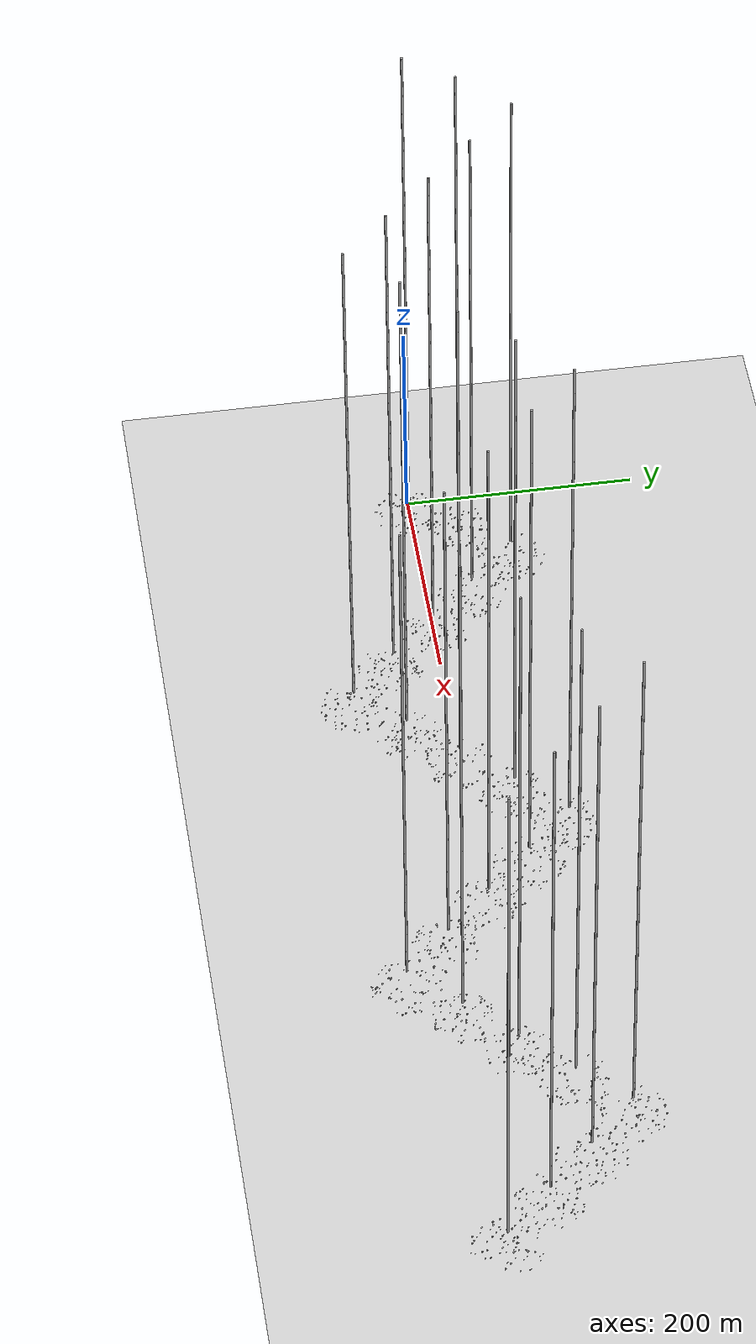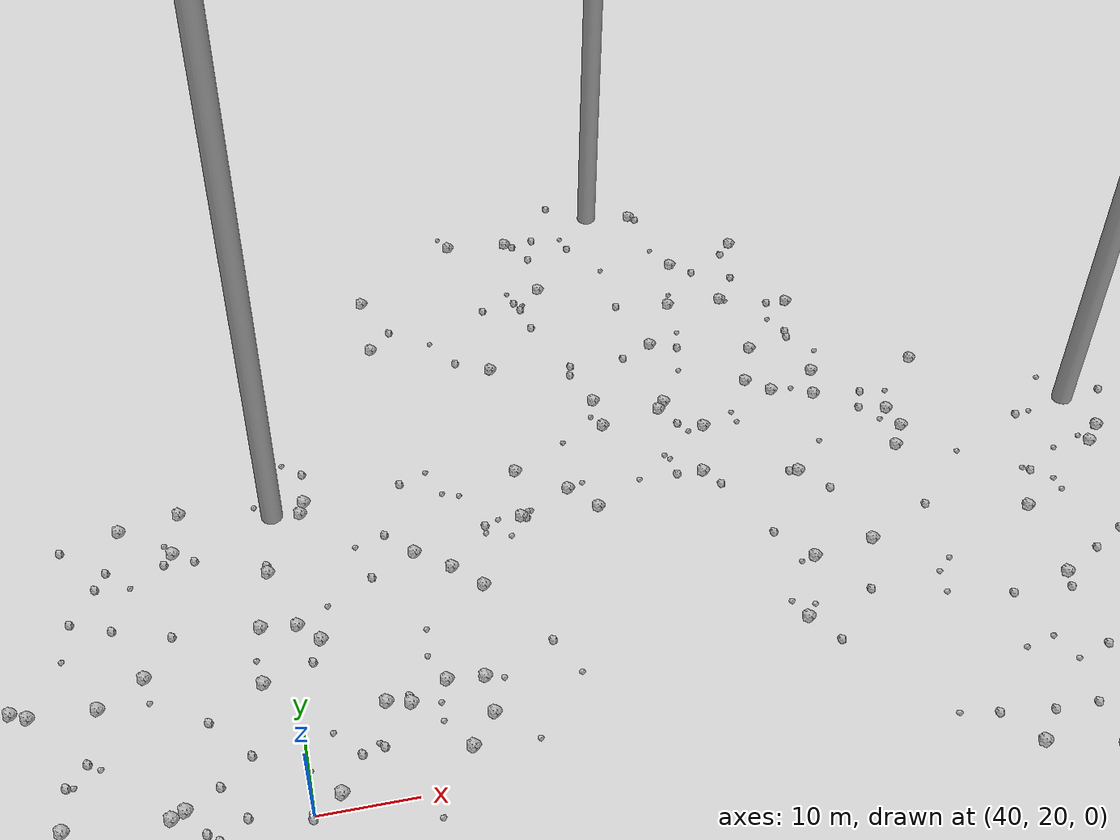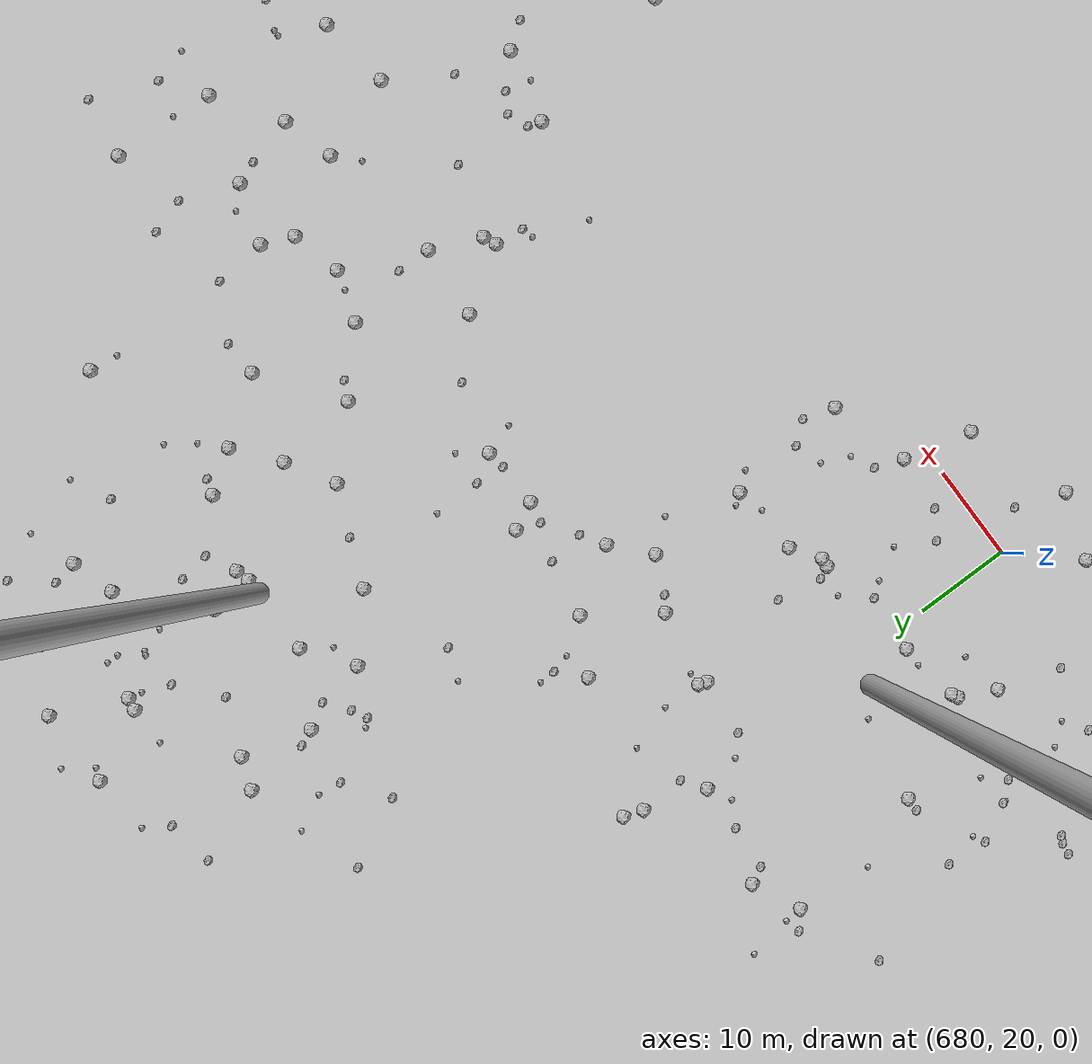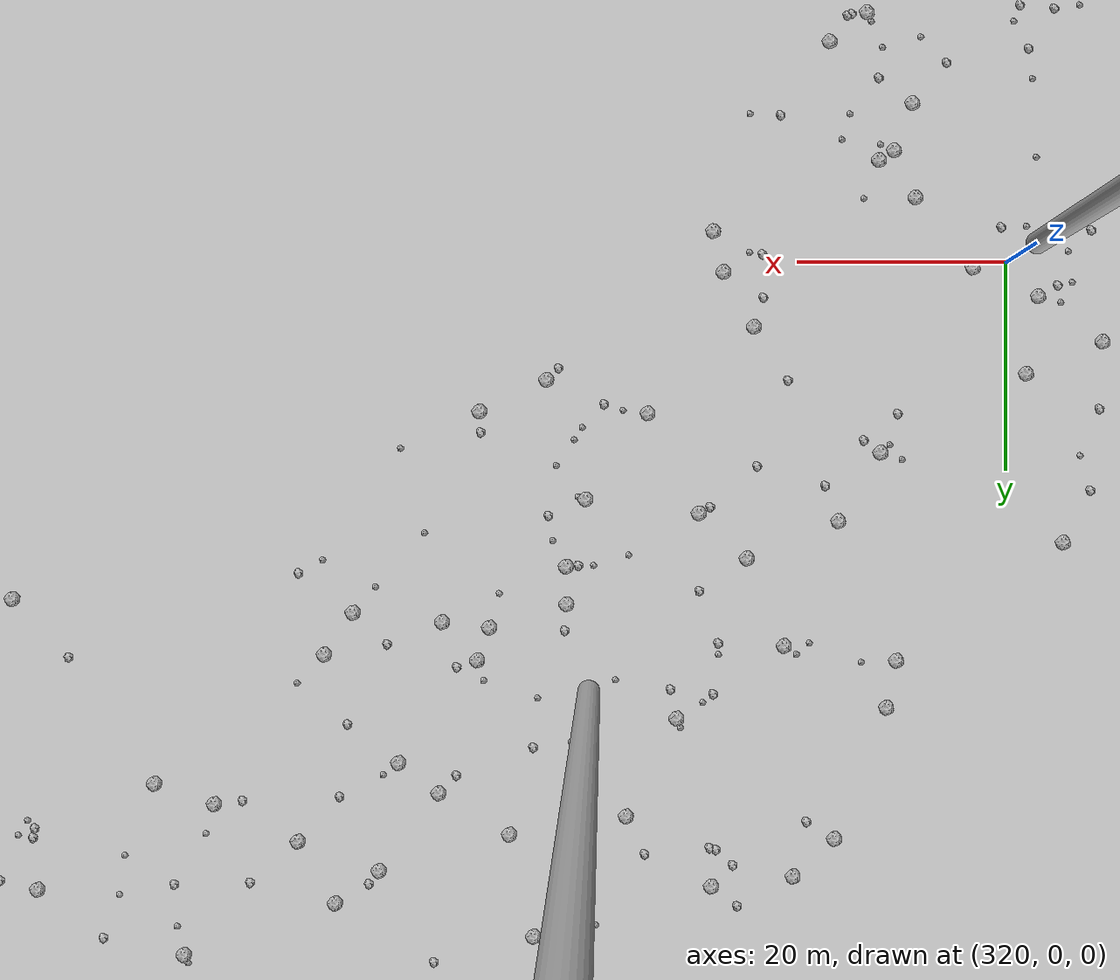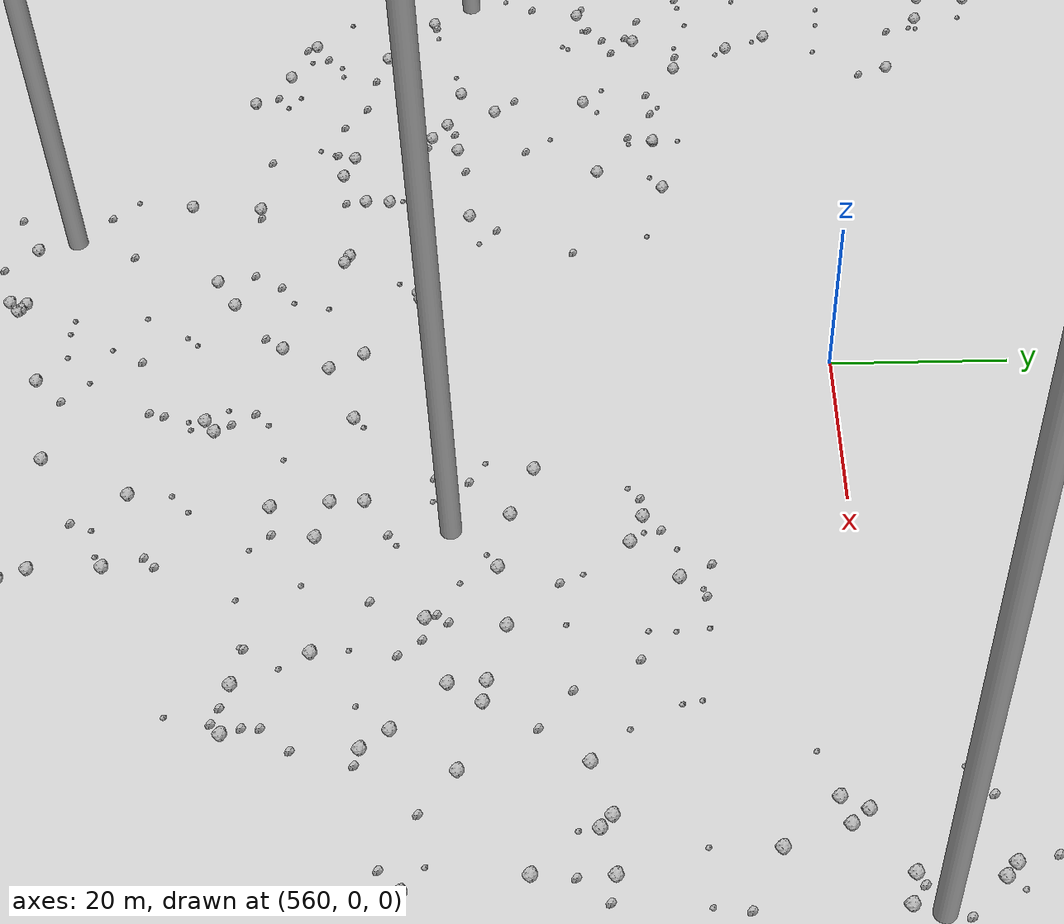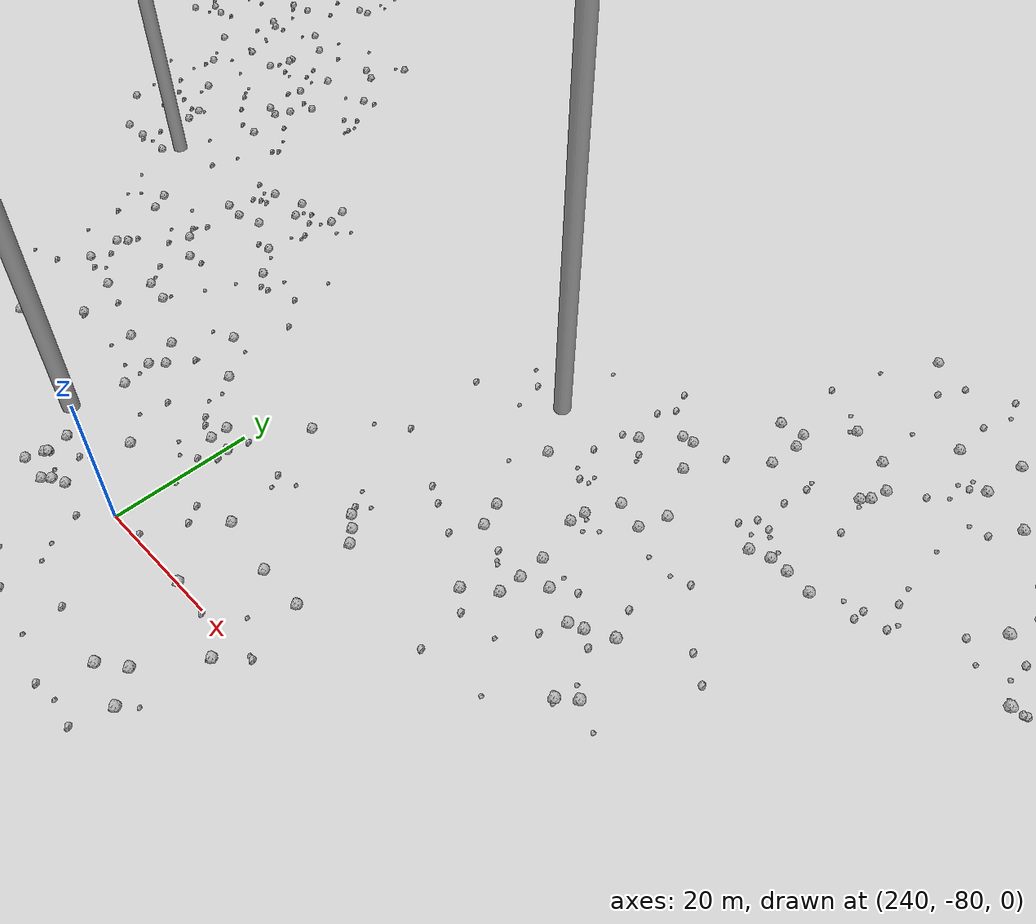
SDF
<sdf version="1.6">
 <world name="default">
  <include><uri>model://custom_ground</uri></include>
  <include><uri>model://sun</uri></include>
  <spherical_coordinates>
   <surface_model>EARTH_WGS84</surface_model>
   <latitude_deg>38.161479</latitude_deg>
   <longitude_deg>-122.454630</longitude_deg>
   <elevation>488.0</elevation>
   <heading_deg>90</heading_deg>
  </spherical_coordinates>
  <model name="rock1_0_0">
   <include><uri>model://rock1</uri><pose>30.813421630112558 14.052619934679427 0.5 0 0 0</pose></include>
  </model>
  <model name="rock1_0_1">
   <include><uri>model://rock1</uri><pose>31.263005932532955 -3.555081857459758 0.5 0 0 0</pose></include>
  </model>
  <model name="rock1_0_2">
   <include><uri>model://rock1</uri><pose>3.062560842775433 -8.579126349104055 0.5 0 0 0</pose></include>
  </model>
  <model name="rock1_0_3">
   <include><uri>model://rock1</uri><pose>2.2622036083634214 -6.75873303845411 0.5 0 0 0</pose></include>
  </model>
  <model name="rock1_0_4">
   <include><uri>model://rock1</uri><pose>-9.320052359139009 15.060780066633328 0.5 0 0 0</pose></include>
  </model>
  <model name="rock1_0_5">
   <include><uri>model://rock1</uri><pose>30.041773885630953 14.564124414637838 0.5 0 0 0</pose></include>
  </model>
  <model name="rock1_0_6">
   <include><uri>model://rock1</uri><pose>-7.956359113545055 -13.569586449923086 0.5 0 0 0</pose></include>
  </model>
  <model name="rock1_0_7">
   <include><uri>model://rock1</uri><pose>18.204109501527142 -17.223239774890164 0.5 0 0 0</pose></include>
  </model>
  <model name="rock1_0_8">
   <include><uri>model://rock1</uri><pose>-0.916840459110869 22.74541993563553 0.5 0 0 0</pose></include>
  </model>
  <model name="rock1_0_9">
   <include><uri>model://rock1</uri><pose>-5.530643240768178 6.582888638079616 0.5 0 0 0</pose></include>
  </model>
  <model name="rock1_0_10">
   <include><uri>model://rock1</uri><pose>21.21864268992362 4.180547698002499 0.5 0 0 0</pose></include>
  </model>
  <model name="rock1_0_11">
   <include><uri>model://rock1</uri><pose>15.686487209626158 19.412198831631322 0.5 0 0 0</pose></include>
  </model>
  <model name="rock1_0_12">
   <include><uri>model://rock1</uri><pose>-5.223978426582089 -19.191512609234273 0.5 0 0 0</pose></include>
  </model>
  <model name="rock1_0_13">
   <include><uri>model://rock1</uri><pose>-1.3845227261867734 -24.063631861825083 0.5 0 0 0</pose></include>
  </model>
  <model name="rock1_0_14">
   <include><uri>model://rock1</uri><pose>30.615616794563678 -2.5062116974249733 0.5 0 0 0</pose></include>
  </model>
  <model name="rock1_0_15">
   <include><uri>model://rock1</uri><pose>17.81580066527915 -4.049925216338039 0.5 0 0 0</pose></include>
  </model>
  <model name="rock1_0_16">
   <include><uri>model://rock1</uri><pose>-1.4753969847542585 24.58261571840182 0.5 0 0 0</pose></include>
  </model>
  <model name="rock1_0_17">
   <include><uri>model://rock1</uri><pose>-1.032616383749037 -11.770431630259203 0.5 0 0 0</pose></include>
  </model>
  <model name="rock1_0_18">
   <include><uri>model://rock1</uri><pose>6.151277521530581 15.302656047938179 0.5 0 0 0</pose></include>
  </model>
  <model name="rock1_0_19">
   <include><uri>model://rock1</uri><pose>28.2217998324001 10.012683567531681 0.5 0 0 0</pose></include>
  </model>
  <model name="rock1_0_20">
   <include><uri>model://rock1</uri><pose>-4.0237681045148666 3.2533593006612023 0.5 0 0 0</pose></include>
  </model>
  <model name="rock1_0_21">
   <include><uri>model://rock1</uri><pose>28.212092442642458 22.76412446825747 0.5 0 0 0</pose></include>
  </model>
  <model name="rock1_0_22">
   <include><uri>model://rock1</uri><pose>9.474128286313903 -5.76423325892344 0.5 0 0 0</pose></include>
  </model>
  <model name="rock1_0_23">
   <include><uri>model://rock1</uri><pose>14.293177001033527 4.044906203207077 0.5 0 0 0</pose></include>
  </model>
  <model name="rock1_0_24">
   <include><uri>model://rock1</uri><pose>-1.4699138029912042 -24.45377630414687 0.5 0 0 0</pose></include>
  </model>
  <model name="rock1_0_25">
   <include><uri>model://rock1</uri><pose>26.836041346514016 13.288668211996658 0.5 0 0 0</pose></include>
  </model>
  <model name="rock1_0_26">
   <include><uri>model://rock1</uri><pose>-6.357755071895866 1.5034511216597828 0.5 0 0 0</pose></include>
  </model>
  <model name="rock2_0_0">
   <include><uri>model://rock2</uri><pose>7.457265138114209 19.64313406274166 0.3 0 0 0</pose></include>
  </model>
  <model name="rock2_0_1">
   <include><uri>model://rock2</uri><pose>-10.449645389333554 10.03415859368021 0.3 0 0 0</pose></include>
  </model>
  <model name="rock2_0_2">
   <include><uri>model://rock2</uri><pose>0.6856317642207372 9.700149326047445 0.3 0 0 0</pose></include>
  </model>
  <model name="rock2_0_3">
   <include><uri>model://rock2</uri><pose>1.274047186400228 12.782362376001927 0.3 0 0 0</pose></include>
  </model>
  <model name="rock2_0_4">
   <include><uri>model://rock2</uri><pose>37.389564937839125 4.64477223881218 0.3 0 0 0</pose></include>
  </model>
  <model name="rock2_0_5">
   <include><uri>model://rock2</uri><pose>-10.885386029139939 -8.27051394484615 0.3 0 0 0</pose></include>
  </model>
  <model name="rock2_0_6">
   <include><uri>model://rock2</uri><pose>9.789555691522093 2.7271717221069167 0.3 0 0 0</pose></include>
  </model>
  <model name="rock2_0_7">
   <include><uri>model://rock2</uri><pose>-5.9386340824718715 4.389578769066013 0.3 0 0 0</pose></include>
  </model>
  <model name="rock2_0_8">
   <include><uri>model://rock2</uri><pose>29.00292569092798 4.16580761332979 0.3 0 0 0</pose></include>
  </model>
  <model name="rock2_0_9">
   <include><uri>model://rock2</uri><pose>-4.0879280996738405 10.165175052225202 0.3 0 0 0</pose></include>
  </model>
  <model name="rock2_0_10">
   <include><uri>model://rock2</uri><pose>7.35958634106931 -28.929308833988575 0.3 0 0 0</pose></include>
  </model>
  <model name="rock2_0_11">
   <include><uri>model://rock2</uri><pose>26.934992649957344 0.4181316352093276 0.3 0 0 0</pose></include>
  </model>
  <model name="rock2_0_12">
   <include><uri>model://rock2</uri><pose>9.261285946866945 -24.43491010309925 0.3 0 0 0</pose></include>
  </model>
  <model name="rock2_0_13">
   <include><uri>model://rock2</uri><pose>31.13473867604972 18.952731467859046 0.3 0 0 0</pose></include>
  </model>
  <model name="rock2_0_14">
   <include><uri>model://rock2</uri><pose>14.861446618989234 6.6265404671307735 0.3 0 0 0</pose></include>
  </model>
  <model name="rock2_0_15">
   <include><uri>model://rock2</uri><pose>-16.248170548353567 -13.205190755553918 0.3 0 0 0</pose></include>
  </model>
  <model name="rock2_0_16">
   <include><uri>model://rock2</uri><pose>10.20335847018831 -24.910720310295567 0.3 0 0 0</pose></include>
  </model>
  <model name="rock2_0_17">
   <include><uri>model://rock2</uri><pose>24.27855187737 -25.908616217516958 0.3 0 0 0</pose></include>
  </model>
  <model name="rock2_0_18">
   <include><uri>model://rock2</uri><pose>30.036504199002692 19.96319697527111 0.3 0 0 0</pose></include>
  </model>
  <model name="rock2_0_19">
   <include><uri>model://rock2</uri><pose>-10.552684495686599 3.2509864137536084 0.3 0 0 0</pose></include>
  </model>
  <model name="rock2_0_20">
   <include><uri>model://rock2</uri><pose>1.5026766648205054 -10.644917214612867 0.3 0 0 0</pose></include>
  </model>
  <model name="rock2_0_21">
   <include><uri>model://rock2</uri><pose>-5.102308244120557 -5.020755405723573 0.3 0 0 0</pose></include>
  </model>
  <model name="rock2_0_22">
   <include><uri>model://rock2</uri><pose>27.801510127597815 -13.634177054286557 0.3 0 0 0</pose></include>
  </model>
  <model name="rock2_0_23">
   <include><uri>model://rock2</uri><pose>-1.0307453298833096 16.399666090407692 0.3 0 0 0</pose></include>
  </model>
  <model name="rock2_0_24">
   <include><uri>model://rock2</uri><pose>-14.120143500861062 -14.201679741017287 0.3 0 0 0</pose></include>
  </model>
  <model name="rock2_0_25">
   <include><uri>model://rock2</uri><pose>12.441714780987823 -16.438775164553693 0.3 0 0 0</pose></include>
  </model>
  <model name="rock2_0_26">
   <include><uri>model://rock2</uri><pose>-7.522201961812662 -2.0635823749856 0.3 0 0 0</pose></include>
  </model>
  <model name="rock3_0_0">
   <include><uri>model://rock3</uri><pose>37.74033737111994 -1.1714888420597873 0.2 0 0 0</pose></include>
  </model>
  <model name="rock3_0_1">
   <include><uri>model://rock3</uri><pose>29.632612273078678 -6.725521163373955 0.2 0 0 0</pose></include>
  </model>
  <model name="rock3_0_2">
   <include><uri>model://rock3</uri><pose>39.290701421273354 4.848428856288876 0.2 0 0 0</pose></include>
  </model>
  <model name="rock3_0_3">
   <include><uri>model://rock3</uri><pose>35.85730598664391 -6.148956230768583 0.2 0 0 0</pose></include>
  </model>
  <model name="rock3_0_4">
   <include><uri>model://rock3</uri><pose>4.4393999599260106 20.641387454248154 0.2 0 0 0</pose></include>
  </model>
  <model name="rock3_0_5">
   <include><uri>model://rock3</uri><pose>7.081327620108183 -27.434144734043834 0.2 0 0 0</pose></include>
  </model>
  <model name="rock3_0_6">
   <include><uri>model://rock3</uri><pose>34.93505838425007 -10.70710921681005 0.2 0 0 0</pose></include>
  </model>
  <model name="rock3_0_7">
   <include><uri>model://rock3</uri><pose>12.912053414443562 -24.25418554666139 0.2 0 0 0</pose></include>
  </model>
  <model name="rock3_0_8">
   <include><uri>model://rock3</uri><pose>7.995243414619182 -18.105651117027385 0.2 0 0 0</pose></include>
  </model>
  <model name="rock3_0_9">
   <include><uri>model://rock3</uri><pose>4.856740565379695 11.02301868584452 0.2 0 0 0</pose></include>
  </model>
  <model name="rock3_0_10">
   <include><uri>model://rock3</uri><pose>6.059015609954905 -10.431088959517417 0.2 0 0 0</pose></include>
  </model>
  <model name="rock3_0_11">
   <include><uri>model://rock3</uri><pose>8.34614304683273 24.750007244205165 0.2 0 0 0</pose></include>
  </model>
  <model name="rock3_0_12">
   <include><uri>model://rock3</uri><pose>25.988213201529938 -10.717020077937423 0.2 0 0 0</pose></include>
  </model>
  <model name="rock3_0_13">
   <include><uri>model://rock3</uri><pose>26.191063345399925 -4.3379318269902924 0.2 0 0 0</pose></include>
  </model>
  <model name="rock3_0_14">
   <include><uri>model://rock3</uri><pose>8.539277369271286 -1.7319867491809404 0.2 0 0 0</pose></include>
  </model>
  <model name="rock3_0_15">
   <include><uri>model://rock3</uri><pose>25.552556240196246 -16.125453990700528 0.2 0 0 0</pose></include>
  </model>
  <model name="rock3_0_16">
   <include><uri>model://rock3</uri><pose>25.22471343772724 8.964063105156661 0.2 0 0 0</pose></include>
  </model>
  <model name="rock3_0_17">
   <include><uri>model://rock3</uri><pose>8.409909167576288 -24.35422118994602 0.2 0 0 0</pose></include>
  </model>
  <model name="rock3_0_18">
   <include><uri>model://rock3</uri><pose>37.0104374160424 -5.905648484102798 0.2 0 0 0</pose></include>
  </model>
  <model name="rock3_0_19">
   <include><uri>model://rock3</uri><pose>-2.824884708076972 21.45865787864544 0.2 0 0 0</pose></include>
  </model>
  <model name="rock3_0_20">
   <include><uri>model://rock3</uri><pose>-3.8553408942129117 17.318934756349975 0.2 0 0 0</pose></include>
  </model>
  <model name="rock3_0_21">
   <include><uri>model://rock3</uri><pose>-7.409820152970525 -21.407274440570774 0.2 0 0 0</pose></include>
  </model>
  <model name="rock3_0_22">
   <include><uri>model://rock3</uri><pose>28.40407404378142 -6.394941349266205 0.2 0 0 0</pose></include>
  </model>
  <model name="rock3_0_23">
   <include><uri>model://rock3</uri><pose>-12.176022871237613 -8.62304900098582 0.2 0 0 0</pose></include>
  </model>
  <model name="rock3_0_24">
   <include><uri>model://rock3</uri><pose>22.944090358214844 2.009989787185738 0.2 0 0 0</pose></include>
  </model>
  <model name="rock3_0_25">
   <include><uri>model://rock3</uri><pose>3.6031177115873376 -13.673889132278202 0.2 0 0 0</pose></include>
  </model>
  <model name="rock3_0_26">
   <include><uri>model://rock3</uri><pose>-15.510828990574733 -8.497840405704384 0.2 0 0 0</pose></include>
  </model>
  <model name="rock1_1_0">
   <include><uri>model://rock1</uri><pose>11.830845189798719 37.38952403606241 0.5 0 0 0</pose></include>
  </model>
  <model name="rock1_1_1">
   <include><uri>model://rock1</uri><pose>57.88559830534171 47.53563070031161 0.5 0 0 0</pose></include>
  </model>
  <model name="rock1_1_2">
   <include><uri>model://rock1</uri><pose>36.971276340847055 43.320193009926335 0.5 0 0 0</pose></include>
  </model>
  <model name="rock1_1_3">
   <include><uri>model://rock1</uri><pose>24.619126164918587 15.918911621716942 0.5 0 0 0</pose></include>
  </model>
  <model name="rock1_1_4">
   <include><uri>model://rock1</uri><pose>58.69340232693442 27.850165236303447 0.5 0 0 0</pose></include>
  </model>
  <model name="rock1_1_5">
   <include><uri>model://rock1</uri><pose>54.24325806023395 50.41843128157919 0.5 0 0 0</pose></include>
  </model>
  <model name="rock1_1_6">
   <include><uri>model://rock1</uri><pose>48.4045499455725 31.322355018039435 0.5 0 0 0</pose></include>
  </model>
  <model name="rock1_1_7">
   <include><uri>model://rock1</uri><pose>16.893595273416828 22.815950304148195 0.5 0 0 0</pose></include>
  </model>
  <model name="rock1_1_8">
   <include><uri>model://rock1</uri><pose>24.941572073235328 39.18062287184588 0.5 0 0 0</pose></include>
  </model>
  <model name="rock1_1_9">
   <include><uri>model://rock1</uri><pose>22.848144193974278 60.0183749183069 0.5 0 0 0</pose></include>
  </model>
  <model name="rock1_1_10">
   <include><uri>model://rock1</uri><pose>28.49508950402583 55.589156095413834 0.5 0 0 0</pose></include>
  </model>
  <model name="rock1_1_11">
   <include><uri>model://rock1</uri><pose>42.93373318655166 40.496964089638496 0.5 0 0 0</pose></include>
  </model>
  <model name="rock1_1_12">
   <include><uri>model://rock1</uri><pose>50.82575375563279 30.679477284472878 0.5 0 0 0</pose></include>
  </model>
  <model name="rock1_1_13">
   <include><uri>model://rock1</uri><pose>36.62683314167424 36.0603131879059 0.5 0 0 0</pose></include>
  </model>
  <model name="rock1_1_14">
   <include><uri>model://rock1</uri><pose>40.75424859807908 42.874492804640276 0.5 0 0 0</pose></include>
  </model>
  <model name="rock1_1_15">
   <include><uri>model://rock1</uri><pose>29.44260795181576 61.33668832641521 0.5 0 0 0</pose></include>
  </model>
  <model name="rock1_1_16">
   <include><uri>model://rock1</uri><pose>43.26017382494367 60.40423853786493 0.5 0 0 0</pose></include>
  </model>
  <model name="rock1_1_17">
   <include><uri>model://rock1</uri><pose>38.40109259154026 50.74429700355805 0.5 0 0 0</pose></include>
  </model>
  <model name="rock1_1_18">
   <include><uri>model://rock1</uri><pose>13.532888954502226 36.56632451757936 0.5 0 0 0</pose></include>
  </model>
  <model name="rock1_1_19">
   <include><uri>model://rock1</uri><pose>60.76936743975434 44.30941101947357 0.5 0 0 0</pose></include>
  </model>
  <model name="rock1_1_20">
   <include><uri>model://rock1</uri><pose>26.899294208451764 22.11334540814505 0.5 0 0 0</pose></include>
  </model>
  <model name="rock1_1_21">
   <include><uri>model://rock1</uri><pose>42.79362117256524 21.68109526499861 0.5 0 0 0</pose></include>
  </model>
  <model name="rock1_1_22">
   <include><uri>model://rock1</uri><pose>58.63180156558387 32.39668255570634 0.5 0 0 0</pose></include>
  </model>
  <model name="rock1_1_23">
   <include><uri>model://rock1</uri><pose>20.313680024733607 36.24632660286065 0.5 0 0 0</pose></include>
  </model>
  <model name="rock1_1_24">
   <include><uri>model://rock1</uri><pose>42.69889124812947 58.735619012124104 0.5 0 0 0</pose></include>
  </model>
  <model name="rock1_1_25">
   <include><uri>model://rock1</uri><pose>55.93251836458462 24.36141229770837 0.5 0 0 0</pose></include>
  </model>
  <model name="rock1_1_26">
   <include><uri>model://rock1</uri><pose>54.75682276511734 32.776048496757106 0.5 0 0 0</pose></include>
  </model>
  <model name="rock2_1_0">
   <include><uri>model://rock2</uri><pose>62.49652605499497 52.84221011370312 0.3 0 0 0</pose></include>
  </model>
  <model name="rock2_1_1">
   <include><uri>model://rock2</uri><pose>19.262304968385717 30.02697464369252 0.3 0 0 0</pose></include>
  </model>
  <model name="rock2_1_2">
   <include><uri>model://rock2</uri><pose>49.20435059886644 47.92806565248922 0.3 0 0 0</pose></include>
  </model>
  <model name="rock2_1_3">
   <include><uri>model://rock2</uri><pose>51.399989530925446 53.75234275079529 0.3 0 0 0</pose></include>
  </model>
  <model name="rock2_1_4">
   <include><uri>model://rock2</uri><pose>33.87314924508475 20.88924599679035 0.3 0 0 0</pose></include>
  </model>
  <model name="rock2_1_5">
   <include><uri>model://rock2</uri><pose>66.32032248729016 35.630722177323975 0.3 0 0 0</pose></include>
  </model>
  <model name="rock2_1_6">
   <include><uri>model://rock2</uri><pose>35.698996140152985 14.518266283597555 0.3 0 0 0</pose></include>
  </model>
  <model name="rock2_1_7">
   <include><uri>model://rock2</uri><pose>39.79009181352157 19.534510405730376 0.3 0 0 0</pose></include>
  </model>
  <model name="rock2_1_8">
   <include><uri>model://rock2</uri><pose>21.81658667672583 46.16015287525476 0.3 0 0 0</pose></include>
  </model>
  <model name="rock2_1_9">
   <include><uri>model://rock2</uri><pose>31.581325997838213 24.838166795688725 0.3 0 0 0</pose></include>
  </model>
  <model name="rock2_1_10">
   <include><uri>model://rock2</uri><pose>17.238598527424763 27.70459941483273 0.3 0 0 0</pose></include>
  </model>
  <model name="rock2_1_11">
   <include><uri>model://rock2</uri><pose>30.947963710676053 32.518770421586495 0.3 0 0 0</pose></include>
  </model>
  <model name="rock2_1_12">
   <include><uri>model://rock2</uri><pose>17.522042782428617 47.925223317321 0.3 0 0 0</pose></include>
  </model>
  <model name="rock2_1_13">
   <include><uri>model://rock2</uri><pose>30.759267299469112 54.198207205958866 0.3 0 0 0</pose></include>
  </model>
  <model name="rock2_1_14">
   <include><uri>model://rock2</uri><pose>43.47307242247922 64.98649081200429 0.3 0 0 0</pose></include>
  </model>
  <model name="rock2_1_15">
   <include><uri>model://rock2</uri><pose>38.32784803870637 51.94886999252944 0.3 0 0 0</pose></include>
  </model>
  <model name="rock2_1_16">
   <include><uri>model://rock2</uri><pose>27.873646910774987 44.10673711936233 0.3 0 0 0</pose></include>
  </model>
  <model name="rock2_1_17">
   <include><uri>model://rock2</uri><pose>50.74916522033938 31.616878457000485 0.3 0 0 0</pose></include>
  </model>
  <model name="rock2_1_18">
   <include><uri>model://rock2</uri><pose>41.795241464093664 37.88573602648387 0.3 0 0 0</pose></include>
  </model>
  <model name="rock2_1_19">
   <include><uri>model://rock2</uri><pose>21.312881612555113 54.403368079817646 0.3 0 0 0</pose></include>
  </model>
  <model name="rock2_1_20">
   <include><uri>model://rock2</uri><pose>54.176768124505855 61.14945827201671 0.3 0 0 0</pose></include>
  </model>
  <model name="rock2_1_21">
   <include><uri>model://rock2</uri><pose>20.14614568235797 52.250081461625186 0.3 0 0 0</pose></include>
  </model>
  <model name="rock2_1_22">
   <include><uri>model://rock2</uri><pose>45.24093464430132 25.745664826334156 0.3 0 0 0</pose></include>
  </model>
  <model name="rock2_1_23">
   <include><uri>model://rock2</uri><pose>27.499121061249078 54.303521553742286 0.3 0 0 0</pose></include>
  </model>
  <model name="rock2_1_24">
   <include><uri>model://rock2</uri><pose>47.481959535362634 26.184289628579474 0.3 0 0 0</pose></include>
  </model>
  <model name="rock2_1_25">
   <include><uri>model://rock2</uri><pose>34.791642281576 27.767263343337085 0.3 0 0 0</pose></include>
  </model>
  <model name="rock2_1_26">
   <include><uri>model://rock2</uri><pose>16.461550950869768 58.29638392886064 0.3 0 0 0</pose></include>
  </model>
  <model name="rock3_1_0">
   <include><uri>model://rock3</uri><pose>62.49369339498362 24.045651757689424 0.2 0 0 0</pose></include>
  </model>
  <model name="rock3_1_1">
   <include><uri>model://rock3</uri><pose>42.76358799367945 28.794194461347228 0.2 0 0 0</pose></include>
  </model>
  <model name="rock3_1_2">
   <include><uri>model://rock3</uri><pose>65.09911952723826 50.800430725521636 0.2 0 0 0</pose></include>
  </model>
  <model name="rock3_1_3">
   <include><uri>model://rock3</uri><pose>44.110136567440335 44.961561087474 0.2 0 0 0</pose></include>
  </model>
  <model name="rock3_1_4">
   <include><uri>model://rock3</uri><pose>68.34020804976569 31.056346661869362 0.2 0 0 0</pose></include>
  </model>
  <model name="rock3_1_5">
   <include><uri>model://rock3</uri><pose>37.66670817439075 60.894988459008154 0.2 0 0 0</pose></include>
  </model>
  <model name="rock3_1_6">
   <include><uri>model://rock3</uri><pose>62.41441257713357 51.73765662522082 0.2 0 0 0</pose></include>
  </model>
  <model name="rock3_1_7">
   <include><uri>model://rock3</uri><pose>53.607979512749075 28.010607687733415 0.2 0 0 0</pose></include>
  </model>
  <model name="rock3_1_8">
   <include><uri>model://rock3</uri><pose>39.74583797388101 20.175625948713375 0.2 0 0 0</pose></include>
  </model>
  <model name="rock3_1_9">
   <include><uri>model://rock3</uri><pose>51.68133138272392 17.211503583136263 0.2 0 0 0</pose></include>
  </model>
  <model name="rock3_1_10">
   <include><uri>model://rock3</uri><pose>53.32216500111936 36.2347704235374 0.2 0 0 0</pose></include>
  </model>
  <model name="rock3_1_11">
   <include><uri>model://rock3</uri><pose>36.1615779754824 39.22218034530792 0.2 0 0 0</pose></include>
  </model>
  <model name="rock3_1_12">
   <include><uri>model://rock3</uri><pose>53.78468847146015 39.731835772340276 0.2 0 0 0</pose></include>
  </model>
  <model name="rock3_1_13">
   <include><uri>model://rock3</uri><pose>47.04882103664558 26.696869885973452 0.2 0 0 0</pose></include>
  </model>
  <model name="rock3_1_14">
   <include><uri>model://rock3</uri><pose>41.348074855058385 66.88839611643536 0.2 0 0 0</pose></include>
  </model>
  <model name="rock3_1_15">
   <include><uri>model://rock3</uri><pose>17.92896850189247 27.603168729684203 0.2 0 0 0</pose></include>
  </model>
  <model name="rock3_1_16">
   <include><uri>model://rock3</uri><pose>25.329610856429404 36.116926763990975 0.2 0 0 0</pose></include>
  </model>
  <model name="rock3_1_17">
   <include><uri>model://rock3</uri><pose>58.67310985586453 58.689858934428095 0.2 0 0 0</pose></include>
  </model>
  <model name="rock3_1_18">
   <include><uri>model://rock3</uri><pose>53.74355562909531 30.23566496976936 0.2 0 0 0</pose></include>
  </model>
  <model name="rock3_1_19">
   <include><uri>model://rock3</uri><pose>40.09143363550082 24.825195813029453 0.2 0 0 0</pose></include>
  </model>
  <model name="rock3_1_20">
   <include><uri>model://rock3</uri><pose>60.477511883106985 31.97895182196311 0.2 0 0 0</pose></include>
  </model>
  <model name="rock3_1_21">
   <include><uri>model://rock3</uri><pose>48.026715333412604 52.62711936718255 0.2 0 0 0</pose></include>
  </model>
  <model name="rock3_1_22">
   <include><uri>model://rock3</uri><pose>64.11382948722209 53.47580888982005 0.2 0 0 0</pose></include>
  </model>
  <model name="rock3_1_23">
   <include><uri>model://rock3</uri><pose>23.823676361614325 51.75235455137812 0.2 0 0 0</pose></include>
  </model>
  <model name="rock3_1_24">
   <include><uri>model://rock3</uri><pose>20.479529283609537 29.191859356077504 0.2 0 0 0</pose></include>
  </model>
  <model name="rock3_1_25">
   <include><uri>model://rock3</uri><pose>16.697260912735445 43.142423299724264 0.2 0 0 0</pose></include>
  </model>
  <model name="rock3_1_26">
   <include><uri>model://rock3</uri><pose>27.59301594095532 57.10495208635808 0.2 0 0 0</pose></include>
  </model>
  <model name="rock1_2_0">
   <include><uri>model://rock1</uri><pose>75.50941880295088 52.987971253154655 0.5 0 0 0</pose></include>
  </model>
  <model name="rock1_2_1">
   <include><uri>model://rock1</uri><pose>107.8992798980209 83.50487660025993 0.5 0 0 0</pose></include>
  </model>
  <model name="rock1_2_2">
   <include><uri>model://rock1</uri><pose>88.57503296618805 55.940539097835796 0.5 0 0 0</pose></include>
  </model>
  <model name="rock1_2_3">
   <include><uri>model://rock1</uri><pose>92.76299090342634 105.54562586089327 0.5 0 0 0</pose></include>
  </model>
  <model name="rock1_2_4">
   <include><uri>model://rock1</uri><pose>68.05580153260233 78.13483075401838 0.5 0 0 0</pose></include>
  </model>
  <model name="rock1_2_5">
   <include><uri>model://rock1</uri><pose>87.32841351490634 68.20595782697015 0.5 0 0 0</pose></include>
  </model>
  <model name="rock1_2_6">
   <include><uri>model://rock1</uri><pose>77.14445150276617 92.36320687429502 0.5 0 0 0</pose></include>
  </model>
  <model name="rock1_2_7">
   <include><uri>model://rock1</uri><pose>74.81224929126202 102.89748346002904 0.5 0 0 0</pose></include>
  </model>
  <model name="rock1_2_8">
   <include><uri>model://rock1</uri><pose>86.37935870980925 67.05208275717958 0.5 0 0 0</pose></include>
  </model>
  <model name="rock1_2_9">
   <include><uri>model://rock1</uri><pose>106.57352943883295 69.92117860893187 0.5 0 0 0</pose></include>
  </model>
  <model name="rock1_2_10">
   <include><uri>model://rock1</uri><pose>92.8650798556948 85.92924967720876 0.5 0 0 0</pose></include>
  </model>
  <model name="rock1_2_11">
   <include><uri>model://rock1</uri><pose>67.2254723857437 103.6398708956783 0.5 0 0 0</pose></include>
  </model>
  <model name="rock1_2_12">
   <include><uri>model://rock1</uri><pose>100.6313236584131 67.55571346161837 0.5 0 0 0</pose></include>
  </model>
  <model name="rock1_2_13">
   <include><uri>model://rock1</uri><pose>100.45031596797875 75.47891377722338 0.5 0 0 0</pose></include>
  </model>
  <model name="rock1_2_14">
   <include><uri>model://rock1</uri><pose>72.7856132788237 56.39391475019632 0.5 0 0 0</pose></include>
  </model>
  <model name="rock1_2_15">
   <include><uri>model://rock1</uri><pose>88.49903526608455 78.77269342102524 0.5 0 0 0</pose></include>
  </model>
  <model name="rock1_2_16">
   <include><uri>model://rock1</uri><pose>67.50718829806863 60.30032442284505 0.5 0 0 0</pose></include>
  </model>
  <model name="rock1_2_17">
   <include><uri>model://rock1</uri><pose>66.7340435860899 53.27179508301395 0.5 0 0 0</pose></include>
  </model>
  <model name="rock1_2_18">
   <include><uri>model://rock1</uri><pose>98.08140850083235 69.80458511693524 0.5 0 0 0</pose></include>
  </model>
  <model name="rock1_2_19">
   <include><uri>model://rock1</uri><pose>90.80407618241676 63.16233972007743 0.5 0 0 0</pose></include>
  </model>
  <model name="rock1_2_20">
   <include><uri>model://rock1</uri><pose>79.0966010870387 70.06925641027735 0.5 0 0 0</pose></include>
  </model>
  <model name="rock1_2_21">
   <include><uri>model://rock1</uri><pose>54.27736993954021 94.1507459382504 0.5 0 0 0</pose></include>
  </model>
  <model name="rock1_2_22">
   <include><uri>model://rock1</uri><pose>54.20678643880629 84.84135953582826 0.5 0 0 0</pose></include>
  </model>
  <model name="rock1_2_23">
   <include><uri>model://rock1</uri><pose>95.38481071604346 93.93568439478912 0.5 0 0 0</pose></include>
  </model>
  <model name="rock1_2_24">
   <include><uri>model://rock1</uri><pose>99.69674471807032 85.6162106162928 0.5 0 0 0</pose></include>
  </model>
  <model name="rock1_2_25">
   <include><uri>model://rock1</uri><pose>79.16905772392727 65.63054654750522 0.5 0 0 0</pose></include>
  </model>
  <model name="rock1_2_26">
   <include><uri>model://rock1</uri><pose>104.4796847287214 96.7756247918694 0.5 0 0 0</pose></include>
  </model>
  <model name="rock2_2_0">
   <include><uri>model://rock2</uri><pose>105.73066257393965 76.85789120926269 0.3 0 0 0</pose></include>
  </model>
  <model name="rock2_2_1">
   <include><uri>model://rock2</uri><pose>78.52732408695019 103.10033226721757 0.3 0 0 0</pose></include>
  </model>
  <model name="rock2_2_2">
   <include><uri>model://rock2</uri><pose>93.48738449273499 104.97542725009504 0.3 0 0 0</pose></include>
  </model>
  <model name="rock2_2_3">
   <include><uri>model://rock2</uri><pose>74.05753502847156 88.98245673935273 0.3 0 0 0</pose></include>
  </model>
  <model name="rock2_2_4">
   <include><uri>model://rock2</uri><pose>90.00993669502495 53.73692950920017 0.3 0 0 0</pose></include>
  </model>
  <model name="rock2_2_5">
   <include><uri>model://rock2</uri><pose>67.25933526854723 53.167211291381356 0.3 0 0 0</pose></include>
  </model>
  <model name="rock2_2_6">
   <include><uri>model://rock2</uri><pose>64.04127463007558 80.39117554040922 0.3 0 0 0</pose></include>
  </model>
  <model name="rock2_2_7">
   <include><uri>model://rock2</uri><pose>82.03022844081451 109.89709541841262 0.3 0 0 0</pose></include>
  </model>
  <model name="rock2_2_8">
   <include><uri>model://rock2</uri><pose>75.69050724391803 102.29260062822638 0.3 0 0 0</pose></include>
  </model>
  <model name="rock2_2_9">
   <include><uri>model://rock2</uri><pose>69.26561635929234 89.73177785167697 0.3 0 0 0</pose></include>
  </model>
  <model name="rock2_2_10">
   <include><uri>model://rock2</uri><pose>85.54394830194349 56.23663831962982 0.3 0 0 0</pose></include>
  </model>
  <model name="rock2_2_11">
   <include><uri>model://rock2</uri><pose>87.89637721568083 64.38430532059974 0.3 0 0 0</pose></include>
  </model>
  <model name="rock2_2_12">
   <include><uri>model://rock2</uri><pose>97.74020249825469 91.98338863656295 0.3 0 0 0</pose></include>
  </model>
  <model name="rock2_2_13">
   <include><uri>model://rock2</uri><pose>105.87050340211309 77.98827291092323 0.3 0 0 0</pose></include>
  </model>
  <model name="rock2_2_14">
   <include><uri>model://rock2</uri><pose>102.47042304805645 89.93316058845485 0.3 0 0 0</pose></include>
  </model>
  <model name="rock2_2_15">
   <include><uri>model://rock2</uri><pose>91.66731218759021 77.68075041225055 0.3 0 0 0</pose></include>
  </model>
  <model name="rock2_2_16">
   <include><uri>model://rock2</uri><pose>86.23145688044264 87.08678998471808 0.3 0 0 0</pose></include>
  </model>
  <model name="rock2_2_17">
   <include><uri>model://rock2</uri><pose>77.22177341051346 99.21757321986661 0.3 0 0 0</pose></include>
  </model>
  <model name="rock2_2_18">
   <include><uri>model://rock2</uri><pose>105.41217552357077 83.88448735409422 0.3 0 0 0</pose></include>
  </model>
  <model name="rock2_2_19">
   <include><uri>model://rock2</uri><pose>77.81501615900329 76.9408716028637 0.3 0 0 0</pose></include>
  </model>
  <model name="rock2_2_20">
   <include><uri>model://rock2</uri><pose>73.51864955017302 90.48932598350936 0.3 0 0 0</pose></include>
  </model>
  <model name="rock2_2_21">
   <include><uri>model://rock2</uri><pose>102.63359423988761 94.96198202428363 0.3 0 0 0</pose></include>
  </model>
  <model name="rock2_2_22">
   <include><uri>model://rock2</uri><pose>74.6534654064605 85.19720015000622 0.3 0 0 0</pose></include>
  </model>
  <model name="rock2_2_23">
   <include><uri>model://rock2</uri><pose>56.87632881171266 87.9282783378096 0.3 0 0 0</pose></include>
  </model>
  <model name="rock2_2_24">
   <include><uri>model://rock2</uri><pose>77.40422032285656 75.36037307766635 0.3 0 0 0</pose></include>
  </model>
  <model name="rock2_2_25">
   <include><uri>model://rock2</uri><pose>84.55637077974387 77.04439263430828 0.3 0 0 0</pose></include>
  </model>
  <model name="rock2_2_26">
   <include><uri>model://rock2</uri><pose>82.82149984230696 100.4206713886218 0.3 0 0 0</pose></include>
  </model>
  <model name="rock3_2_0">
   <include><uri>model://rock3</uri><pose>81.10240894955261 56.274685336577946 0.2 0 0 0</pose></include>
  </model>
  <model name="rock3_2_1">
   <include><uri>model://rock3</uri><pose>103.10279617242148 67.53170974647574 0.2 0 0 0</pose></include>
  </model>
  <model name="rock3_2_2">
   <include><uri>model://rock3</uri><pose>90.66752519842655 73.51052053042935 0.2 0 0 0</pose></include>
  </model>
  <model name="rock3_2_3">
   <include><uri>model://rock3</uri><pose>88.83135221833999 62.84460292237011 0.2 0 0 0</pose></include>
  </model>
  <model name="rock3_2_4">
   <include><uri>model://rock3</uri><pose>93.49730955596749 88.02159743160044 0.2 0 0 0</pose></include>
  </model>
  <model name="rock3_2_5">
   <include><uri>model://rock3</uri><pose>61.565484398144676 84.70691139283863 0.2 0 0 0</pose></include>
  </model>
  <model name="rock3_2_6">
   <include><uri>model://rock3</uri><pose>78.11713225468955 67.54102757422173 0.2 0 0 0</pose></include>
  </model>
  <model name="rock3_2_7">
   <include><uri>model://rock3</uri><pose>85.42928762803811 58.81275761213465 0.2 0 0 0</pose></include>
  </model>
  <model name="rock3_2_8">
   <include><uri>model://rock3</uri><pose>74.51669678792325 89.86585421119426 0.2 0 0 0</pose></include>
  </model>
  <model name="rock3_2_9">
   <include><uri>model://rock3</uri><pose>94.76097028261411 64.94133535773467 0.2 0 0 0</pose></include>
  </model>
  <model name="rock3_2_10">
   <include><uri>model://rock3</uri><pose>57.357977539289074 62.43440729155107 0.2 0 0 0</pose></include>
  </model>
  <model name="rock3_2_11">
   <include><uri>model://rock3</uri><pose>67.63020646456096 54.12975031968361 0.2 0 0 0</pose></include>
  </model>
  <model name="rock3_2_12">
   <include><uri>model://rock3</uri><pose>108.28613126671031 73.61871535265175 0.2 0 0 0</pose></include>
  </model>
  <model name="rock3_2_13">
   <include><uri>model://rock3</uri><pose>104.50329184629693 80.67674837076886 0.2 0 0 0</pose></include>
  </model>
  <model name="rock3_2_14">
   <include><uri>model://rock3</uri><pose>94.8843298233872 63.23869306658797 0.2 0 0 0</pose></include>
  </model>
  <model name="rock3_2_15">
   <include><uri>model://rock3</uri><pose>66.17150847956601 105.93801574870434 0.2 0 0 0</pose></include>
  </model>
  <model name="rock3_2_16">
   <include><uri>model://rock3</uri><pose>82.38343966219622 102.6911566784675 0.2 0 0 0</pose></include>
  </model>
  <model name="rock3_2_17">
   <include><uri>model://rock3</uri><pose>73.01054147597723 92.51552736162299 0.2 0 0 0</pose></include>
  </model>
  <model name="rock3_2_18">
   <include><uri>model://rock3</uri><pose>92.4872706829149 80.51033885437037 0.2 0 0 0</pose></include>
  </model>
  <model name="rock3_2_19">
   <include><uri>model://rock3</uri><pose>100.30933840563364 85.33099245155671 0.2 0 0 0</pose></include>
  </model>
  <model name="rock3_2_20">
   <include><uri>model://rock3</uri><pose>86.10694831604656 94.86889559930955 0.2 0 0 0</pose></include>
  </model>
  <model name="rock3_2_21">
   <include><uri>model://rock3</uri><pose>74.61022882916419 57.16954463787921 0.2 0 0 0</pose></include>
  </model>
  <model name="rock3_2_22">
   <include><uri>model://rock3</uri><pose>93.65054326315365 97.69840152173975 0.2 0 0 0</pose></include>
  </model>
  <model name="rock3_2_23">
   <include><uri>model://rock3</uri><pose>60.50087745840451 58.008490943979076 0.2 0 0 0</pose></include>
  </model>
  <model name="rock3_2_24">
   <include><uri>model://rock3</uri><pose>73.91127255243293 63.984487979460816 0.2 0 0 0</pose></include>
  </model>
  <model name="rock3_2_25">
   <include><uri>model://rock3</uri><pose>84.968198152998 59.514108142873134 0.2 0 0 0</pose></include>
  </model>
  <model name="rock3_2_26">
   <include><uri>model://rock3</uri><pose>67.9789309747683 54.079136257858515 0.2 0 0 0</pose></include>
  </model>
  <model name="rock1_3_0">
   <include><uri>model://rock1</uri><pose>143.91263644314535 48.73408949809202 0.5 0 0 0</pose></include>
  </model>
  <model name="rock1_3_1">
   <include><uri>model://rock1</uri><pose>134.23978104740326 51.448816079101306 0.5 0 0 0</pose></include>
  </model>
  <model name="rock1_3_2">
   <include><uri>model://rock1</uri><pose>99.29053412298455 53.7572025037994 0.5 0 0 0</pose></include>
  </model>
  <model name="rock1_3_3">
   <include><uri>model://rock1</uri><pose>136.26983557929282 53.75462802213581 0.5 0 0 0</pose></include>
  </model>
  <model name="rock1_3_4">
   <include><uri>model://rock1</uri><pose>136.61664562565997 19.911298910588375 0.5 0 0 0</pose></include>
  </model>
  <model name="rock1_3_5">
   <include><uri>model://rock1</uri><pose>124.23113060862872 14.124953828934167 0.5 0 0 0</pose></include>
  </model>
  <model name="rock1_3_6">
   <include><uri>model://rock1</uri><pose>96.70302410929253 40.920346005721385 0.5 0 0 0</pose></include>
  </model>
  <model name="rock1_3_7">
   <include><uri>model://rock1</uri><pose>133.71541608707858 37.41071107907288 0.5 0 0 0</pose></include>
  </model>
  <model name="rock1_3_8">
   <include><uri>model://rock1</uri><pose>103.75388195582278 42.07709017321167 0.5 0 0 0</pose></include>
  </model>
  <model name="rock1_3_9">
   <include><uri>model://rock1</uri><pose>139.01648457850112 18.719990489061217 0.5 0 0 0</pose></include>
  </model>
  <model name="rock1_3_10">
   <include><uri>model://rock1</uri><pose>111.84675582795325 55.462300016978546 0.5 0 0 0</pose></include>
  </model>
  <model name="rock1_3_11">
   <include><uri>model://rock1</uri><pose>117.88753172641279 11.44165682435819 0.5 0 0 0</pose></include>
  </model>
  <model name="rock1_3_12">
   <include><uri>model://rock1</uri><pose>113.65429981982997 58.458518912526316 0.5 0 0 0</pose></include>
  </model>
  <model name="rock1_3_13">
   <include><uri>model://rock1</uri><pose>119.2509075502643 69.66101629265692 0.5 0 0 0</pose></include>
  </model>
  <model name="rock1_3_14">
   <include><uri>model://rock1</uri><pose>137.39279864087092 28.969298301321945 0.5 0 0 0</pose></include>
  </model>
  <model name="rock1_3_15">
   <include><uri>model://rock1</uri><pose>120.54302248866686 15.121764410270284 0.5 0 0 0</pose></include>
  </model>
  <model name="rock1_3_16">
   <include><uri>model://rock1</uri><pose>93.16226184039205 32.972352242881044 0.5 0 0 0</pose></include>
  </model>
  <model name="rock1_3_17">
   <include><uri>model://rock1</uri><pose>145.76830102000238 37.64182673999895 0.5 0 0 0</pose></include>
  </model>
  <model name="rock1_3_18">
   <include><uri>model://rock1</uri><pose>148.1632641764408 37.97203198511947 0.5 0 0 0</pose></include>
  </model>
  <model name="rock1_3_19">
   <include><uri>model://rock1</uri><pose>113.04904396982187 61.60383961936212 0.5 0 0 0</pose></include>
  </model>
  <model name="rock1_3_20">
   <include><uri>model://rock1</uri><pose>132.73147339604566 28.489153290816837 0.5 0 0 0</pose></include>
  </model>
  <model name="rock1_3_21">
   <include><uri>model://rock1</uri><pose>110.41576314202075 13.459511500073429 0.5 0 0 0</pose></include>
  </model>
  <model name="rock1_3_22">
   <include><uri>model://rock1</uri><pose>141.48646600002695 46.057161266408215 0.5 0 0 0</pose></include>
  </model>
  <model name="rock1_3_23">
   <include><uri>model://rock1</uri><pose>122.48516899570335 33.16572608764254 0.5 0 0 0</pose></include>
  </model>
  <model name="rock1_3_24">
   <include><uri>model://rock1</uri><pose>105.43646117256377 65.88554118407703 0.5 0 0 0</pose></include>
  </model>
  <model name="rock1_3_25">
   <include><uri>model://rock1</uri><pose>122.65874574936556 43.19923954013518 0.5 0 0 0</pose></include>
  </model>
  <model name="rock1_3_26">
   <include><uri>model://rock1</uri><pose>130.61802360830478 33.06756898086658 0.5 0 0 0</pose></include>
  </model>
  <model name="rock2_3_0">
   <include><uri>model://rock2</uri><pose>122.00269396969841 31.265327874048875 0.3 0 0 0</pose></include>
  </model>
  <model name="rock2_3_1">
   <include><uri>model://rock2</uri><pose>117.71620797006966 16.776502144770653 0.3 0 0 0</pose></include>
  </model>
  <model name="rock2_3_2">
   <include><uri>model://rock2</uri><pose>139.46731462097762 59.62820243741915 0.3 0 0 0</pose></include>
  </model>
  <model name="rock2_3_3">
   <include><uri>model://rock2</uri><pose>113.12663707300926 16.83790322748328 0.3 0 0 0</pose></include>
  </model>
  <model name="rock2_3_4">
   <include><uri>model://rock2</uri><pose>109.91996672918283 62.62754200125385 0.3 0 0 0</pose></include>
  </model>
  <model name="rock2_3_5">
   <include><uri>model://rock2</uri><pose>134.22630558864623 27.2304423933172 0.3 0 0 0</pose></include>
  </model>
  <model name="rock2_3_6">
   <include><uri>model://rock2</uri><pose>146.5629303790567 47.774879419793955 0.3 0 0 0</pose></include>
  </model>
  <model name="rock2_3_7">
   <include><uri>model://rock2</uri><pose>115.57557845023652 31.72844241956603 0.3 0 0 0</pose></include>
  </model>
  <model name="rock2_3_8">
   <include><uri>model://rock2</uri><pose>125.34548133364385 48.49676242488086 0.3 0 0 0</pose></include>
  </model>
  <model name="rock2_3_9">
   <include><uri>model://rock2</uri><pose>136.57180016209097 61.5372112521315 0.3 0 0 0</pose></include>
  </model>
  <model name="rock2_3_10">
   <include><uri>model://rock2</uri><pose>101.90761250531165 50.5782078456295 0.3 0 0 0</pose></include>
  </model>
  <model name="rock2_3_11">
   <include><uri>model://rock2</uri><pose>98.26382149071338 54.088352055370166 0.3 0 0 0</pose></include>
  </model>
  <model name="rock2_3_12">
   <include><uri>model://rock2</uri><pose>141.30881653645312 19.13930474004978 0.3 0 0 0</pose></include>
  </model>
  <model name="rock2_3_13">
   <include><uri>model://rock2</uri><pose>95.48736355896565 29.550164053685503 0.3 0 0 0</pose></include>
  </model>
  <model name="rock2_3_14">
   <include><uri>model://rock2</uri><pose>122.20185530138775 23.410843781976485 0.3 0 0 0</pose></include>
  </model>
  <model name="rock2_3_15">
   <include><uri>model://rock2</uri><pose>111.45635744862572 45.96132306425616 0.3 0 0 0</pose></include>
  </model>
  <model name="rock2_3_16">
   <include><uri>model://rock2</uri><pose>126.50426705400756 23.85647162075073 0.3 0 0 0</pose></include>
  </model>
  <model name="rock2_3_17">
   <include><uri>model://rock2</uri><pose>127.75550082523469 57.599443575775815 0.3 0 0 0</pose></include>
  </model>
  <model name="rock2_3_18">
   <include><uri>model://rock2</uri><pose>111.05617622125268 65.24640918657121 0.3 0 0 0</pose></include>
  </model>
  <model name="rock2_3_19">
   <include><uri>model://rock2</uri><pose>93.45983772131527 45.353207203682 0.3 0 0 0</pose></include>
  </model>
  <model name="rock2_3_20">
   <include><uri>model://rock2</uri><pose>127.23391063739291 35.89978036621482 0.3 0 0 0</pose></include>
  </model>
  <model name="rock2_3_21">
   <include><uri>model://rock2</uri><pose>131.11280219914983 38.14740354932632 0.3 0 0 0</pose></include>
  </model>
  <model name="rock2_3_22">
   <include><uri>model://rock2</uri><pose>127.23706982143115 14.861892669203574 0.3 0 0 0</pose></include>
  </model>
  <model name="rock2_3_23">
   <include><uri>model://rock2</uri><pose>107.51935555713032 17.607722246640208 0.3 0 0 0</pose></include>
  </model>
  <model name="rock2_3_24">
   <include><uri>model://rock2</uri><pose>100.94310296137432 35.37222142472771 0.3 0 0 0</pose></include>
  </model>
  <model name="rock2_3_25">
   <include><uri>model://rock2</uri><pose>138.84011136389694 36.618857951701074 0.3 0 0 0</pose></include>
  </model>
  <model name="rock2_3_26">
   <include><uri>model://rock2</uri><pose>142.71950381534683 31.443886252180008 0.3 0 0 0</pose></include>
  </model>
  <model name="rock3_3_0">
   <include><uri>model://rock3</uri><pose>137.5223468624958 24.46563546748298 0.2 0 0 0</pose></include>
  </model>
  <model name="rock3_3_1">
   <include><uri>model://rock3</uri><pose>127.55584054250792 44.9559758182083 0.2 0 0 0</pose></include>
  </model>
  <model name="rock3_3_2">
   <include><uri>model://rock3</uri><pose>108.75015973836665 33.34606007730284 0.2 0 0 0</pose></include>
  </model>
  <model name="rock3_3_3">
   <include><uri>model://rock3</uri><pose>129.67943052417434 51.36500748614611 0.2 0 0 0</pose></include>
  </model>
  <model name="rock3_3_4">
   <include><uri>model://rock3</uri><pose>148.42148938486903 42.82749705652415 0.2 0 0 0</pose></include>
  </model>
  <model name="rock3_3_5">
   <include><uri>model://rock3</uri><pose>121.30646518679615 12.88574796713198 0.2 0 0 0</pose></include>
  </model>
  <model name="rock3_3_6">
   <include><uri>model://rock3</uri><pose>127.73654859665373 57.58255207959293 0.2 0 0 0</pose></include>
  </model>
  <model name="rock3_3_7">
   <include><uri>model://rock3</uri><pose>146.510633795888 43.24566771516818 0.2 0 0 0</pose></include>
  </model>
  <model name="rock3_3_8">
   <include><uri>model://rock3</uri><pose>124.64598209008707 49.05903076810089 0.2 0 0 0</pose></include>
  </model>
  <model name="rock3_3_9">
   <include><uri>model://rock3</uri><pose>117.11009975185567 25.480092626706572 0.2 0 0 0</pose></include>
  </model>
  <model name="rock3_3_10">
   <include><uri>model://rock3</uri><pose>133.15943299837284 63.25390384046115 0.2 0 0 0</pose></include>
  </model>
  <model name="rock3_3_11">
   <include><uri>model://rock3</uri><pose>129.55701607223693 57.82011880046233 0.2 0 0 0</pose></include>
  </model>
  <model name="rock3_3_12">
   <include><uri>model://rock3</uri><pose>103.36725491613609 58.12793765537821 0.2 0 0 0</pose></include>
  </model>
  <model name="rock3_3_13">
   <include><uri>model://rock3</uri><pose>110.8903753938168 37.83468178990469 0.2 0 0 0</pose></include>
  </model>
  <model name="rock3_3_14">
   <include><uri>model://rock3</uri><pose>95.09570173730123 40.6263443684674 0.2 0 0 0</pose></include>
  </model>
  <model name="rock3_3_15">
   <include><uri>model://rock3</uri><pose>103.64445148418226 18.392757833528066 0.2 0 0 0</pose></include>
  </model>
  <model name="rock3_3_16">
   <include><uri>model://rock3</uri><pose>113.79471549834878 24.65944383363782 0.2 0 0 0</pose></include>
  </model>
  <model name="rock3_3_17">
   <include><uri>model://rock3</uri><pose>133.3801180065394 52.65238293428115 0.2 0 0 0</pose></include>
  </model>
  <model name="rock3_3_18">
   <include><uri>model://rock3</uri><pose>109.101007979897 36.20046495488195 0.2 0 0 0</pose></include>
  </model>
  <model name="rock3_3_19">
   <include><uri>model://rock3</uri><pose>92.17460204912801 35.50991093404315 0.2 0 0 0</pose></include>
  </model>
  <model name="rock3_3_20">
   <include><uri>model://rock3</uri><pose>133.2188064676865 40.05604287506512 0.2 0 0 0</pose></include>
  </model>
  <model name="rock3_3_21">
   <include><uri>model://rock3</uri><pose>118.40580642337746 53.18402595671407 0.2 0 0 0</pose></include>
  </model>
  <model name="rock3_3_22">
   <include><uri>model://rock3</uri><pose>118.37542556839047 22.233251889312328 0.2 0 0 0</pose></include>
  </model>
  <model name="rock3_3_23">
   <include><uri>model://rock3</uri><pose>127.41321697387818 46.74990696345229 0.2 0 0 0</pose></include>
  </model>
  <model name="rock3_3_24">
   <include><uri>model://rock3</uri><pose>111.67913645805281 60.16515082937319 0.2 0 0 0</pose></include>
  </model>
  <model name="rock3_3_25">
   <include><uri>model://rock3</uri><pose>114.13802361421205 64.7943986625456 0.2 0 0 0</pose></include>
  </model>
  <model name="rock3_3_26">
   <include><uri>model://rock3</uri><pose>94.47727750667174 34.649616150814246 0.2 0 0 0</pose></include>
  </model>
  <model name="rock1_4_0">
   <include><uri>model://rock1</uri><pose>153.7229398467295 6.755805493890733 0.5 0 0 0</pose></include>
  </model>
  <model name="rock1_4_1">
   <include><uri>model://rock1</uri><pose>135.5151602363163 7.462312081634607 0.5 0 0 0</pose></include>
  </model>
  <model name="rock1_4_2">
   <include><uri>model://rock1</uri><pose>151.91533219268464 -7.51033611952402 0.5 0 0 0</pose></include>
  </model>
  <model name="rock1_4_3">
   <include><uri>model://rock1</uri><pose>175.11340357926093 25.791393028742917 0.5 0 0 0</pose></include>
  </model>
  <model name="rock1_4_4">
   <include><uri>model://rock1</uri><pose>172.32803318853678 -1.9115266356070393 0.5 0 0 0</pose></include>
  </model>
  <model name="rock1_4_5">
   <include><uri>model://rock1</uri><pose>179.3311239347376 11.251857982802186 0.5 0 0 0</pose></include>
  </model>
  <model name="rock1_4_6">
   <include><uri>model://rock1</uri><pose>160.35750781436658 -17.621638511317663 0.5 0 0 0</pose></include>
  </model>
  <model name="rock1_4_7">
   <include><uri>model://rock1</uri><pose>159.46833847939968 -27.449863391089437 0.5 0 0 0</pose></include>
  </model>
  <model name="rock1_4_8">
   <include><uri>model://rock1</uri><pose>154.37378247202068 -27.25953598522055 0.5 0 0 0</pose></include>
  </model>
  <model name="rock1_4_9">
   <include><uri>model://rock1</uri><pose>149.521458112424 -15.858248729201627 0.5 0 0 0</pose></include>
  </model>
  <model name="rock1_4_10">
   <include><uri>model://rock1</uri><pose>167.55947120354512 11.303746523114725 0.5 0 0 0</pose></include>
  </model>
  <model name="rock1_4_11">
   <include><uri>model://rock1</uri><pose>142.84798287135158 -0.24257687619884294 0.5 0 0 0</pose></include>
  </model>
  <model name="rock1_4_12">
   <include><uri>model://rock1</uri><pose>169.68619883319747 19.891013758333983 0.5 0 0 0</pose></include>
  </model>
  <model name="rock1_4_13">
   <include><uri>model://rock1</uri><pose>155.28486320425 18.634828433890675 0.5 0 0 0</pose></include>
  </model>
  <model name="rock1_4_14">
   <include><uri>model://rock1</uri><pose>167.0137351543894 4.649245621403743 0.5 0 0 0</pose></include>
  </model>
  <model name="rock1_4_15">
   <include><uri>model://rock1</uri><pose>149.00908792968883 22.257676872944536 0.5 0 0 0</pose></include>
  </model>
  <model name="rock1_4_16">
   <include><uri>model://rock1</uri><pose>171.07548097065967 -4.6685141496669615 0.5 0 0 0</pose></include>
  </model>
  <model name="rock1_4_17">
   <include><uri>model://rock1</uri><pose>168.36917561473362 -3.842777555027407 0.5 0 0 0</pose></include>
  </model>
  <model name="rock1_4_18">
   <include><uri>model://rock1</uri><pose>145.6644140960986 7.750521613116511 0.5 0 0 0</pose></include>
  </model>
  <model name="rock1_4_19">
   <include><uri>model://rock1</uri><pose>159.22627216430118 -14.612817652971499 0.5 0 0 0</pose></include>
  </model>
  <model name="rock1_4_20">
   <include><uri>model://rock1</uri><pose>173.8426539455729 -11.663283077753974 0.5 0 0 0</pose></include>
  </model>
  <model name="rock1_4_21">
   <include><uri>model://rock1</uri><pose>166.67875433195252 -27.619150799613926 0.5 0 0 0</pose></include>
  </model>
  <model name="rock1_4_22">
   <include><uri>model://rock1</uri><pose>154.5964143355229 11.781159909981021 0.5 0 0 0</pose></include>
  </model>
  <model name="rock1_4_23">
   <include><uri>model://rock1</uri><pose>154.78480760240944 10.88975069082273 0.5 0 0 0</pose></include>
  </model>
  <model name="rock1_4_24">
   <include><uri>model://rock1</uri><pose>174.53792970500888 1.8131652718269855 0.5 0 0 0</pose></include>
  </model>
  <model name="rock1_4_25">
   <include><uri>model://rock1</uri><pose>145.03842024653935 -20.125136227220565 0.5 0 0 0</pose></include>
  </model>
  <model name="rock1_4_26">
   <include><uri>model://rock1</uri><pose>172.93997823996517 18.446482301540627 0.5 0 0 0</pose></include>
  </model>
  <model name="rock2_4_0">
   <include><uri>model://rock2</uri><pose>151.72895581357923 -18.001361607101078 0.3 0 0 0</pose></include>
  </model>
  <model name="rock2_4_1">
   <include><uri>model://rock2</uri><pose>160.67686657215503 -28.138284671436903 0.3 0 0 0</pose></include>
  </model>
  <model name="rock2_4_2">
   <include><uri>model://rock2</uri><pose>160.64057031957043 -24.2746967819974 0.3 0 0 0</pose></include>
  </model>
  <model name="rock2_4_3">
   <include><uri>model://rock2</uri><pose>145.42628036386733 -10.094599371741559 0.3 0 0 0</pose></include>
  </model>
  <model name="rock2_4_4">
   <include><uri>model://rock2</uri><pose>157.32748855848584 -15.067109727488921 0.3 0 0 0</pose></include>
  </model>
  <model name="rock2_4_5">
   <include><uri>model://rock2</uri><pose>157.7563415733827 7.580550416360104 0.3 0 0 0</pose></include>
  </model>
  <model name="rock2_4_6">
   <include><uri>model://rock2</uri><pose>171.33746097064136 2.1817345652823903 0.3 0 0 0</pose></include>
  </model>
  <model name="rock2_4_7">
   <include><uri>model://rock2</uri><pose>164.51156644766223 -8.107920104496095 0.3 0 0 0</pose></include>
  </model>
  <model name="rock2_4_8">
   <include><uri>model://rock2</uri><pose>142.99924664356925 -2.3498453648485835 0.3 0 0 0</pose></include>
  </model>
  <model name="rock2_4_9">
   <include><uri>model://rock2</uri><pose>182.00115908159816 -13.303106765513778 0.3 0 0 0</pose></include>
  </model>
  <model name="rock2_4_10">
   <include><uri>model://rock2</uri><pose>161.4231731942306 12.189787270585931 0.3 0 0 0</pose></include>
  </model>
  <model name="rock2_4_11">
   <include><uri>model://rock2</uri><pose>186.0441902553757 1.8537566288427207 0.3 0 0 0</pose></include>
  </model>
  <model name="rock2_4_12">
   <include><uri>model://rock2</uri><pose>176.40212055990196 -6.4239481339063325 0.3 0 0 0</pose></include>
  </model>
  <model name="rock2_4_13">
   <include><uri>model://rock2</uri><pose>161.10184392713973 19.09940548257851 0.3 0 0 0</pose></include>
  </model>
  <model name="rock2_4_14">
   <include><uri>model://rock2</uri><pose>169.68964710427974 -11.419610253746004 0.3 0 0 0</pose></include>
  </model>
  <model name="rock2_4_15">
   <include><uri>model://rock2</uri><pose>177.98285560720635 -23.999278707785244 0.3 0 0 0</pose></include>
  </model>
  <model name="rock2_4_16">
   <include><uri>model://rock2</uri><pose>184.30289595186508 5.410253837326664 0.3 0 0 0</pose></include>
  </model>
  <model name="rock2_4_17">
   <include><uri>model://rock2</uri><pose>165.92694622162406 2.367080793959161 0.3 0 0 0</pose></include>
  </model>
  <model name="rock2_4_18">
   <include><uri>model://rock2</uri><pose>137.5217435465268 14.850348114528188 0.3 0 0 0</pose></include>
  </model>
  <model name="rock2_4_19">
   <include><uri>model://rock2</uri><pose>182.23550187186703 3.8038366950457103 0.3 0 0 0</pose></include>
  </model>
  <model name="rock2_4_20">
   <include><uri>model://rock2</uri><pose>154.37121671445868 8.575865432532666 0.3 0 0 0</pose></include>
  </model>
  <model name="rock2_4_21">
   <include><uri>model://rock2</uri><pose>182.75468735550783 -12.384482254916396 0.3 0 0 0</pose></include>
  </model>
  <model name="rock2_4_22">
   <include><uri>model://rock2</uri><pose>181.54754936790346 12.076492341386569 0.3 0 0 0</pose></include>
  </model>
  <model name="rock2_4_23">
   <include><uri>model://rock2</uri><pose>152.9313499995617 -14.038373038867588 0.3 0 0 0</pose></include>
  </model>
  <model name="rock2_4_24">
   <include><uri>model://rock2</uri><pose>160.79046666416878 -4.853157617856752 0.3 0 0 0</pose></include>
  </model>
  <model name="rock2_4_25">
   <include><uri>model://rock2</uri><pose>162.86779368001618 9.399092015815576 0.3 0 0 0</pose></include>
  </model>
  <model name="rock2_4_26">
   <include><uri>model://rock2</uri><pose>149.48424773561837 -13.065816356079903 0.3 0 0 0</pose></include>
  </model>
  <model name="rock3_4_0">
   <include><uri>model://rock3</uri><pose>185.93470201435295 0.9285591236546544 0.2 0 0 0</pose></include>
  </model>
  <model name="rock3_4_1">
   <include><uri>model://rock3</uri><pose>146.80014660442959 20.300849354944972 0.2 0 0 0</pose></include>
  </model>
  <model name="rock3_4_2">
   <include><uri>model://rock3</uri><pose>151.41922471778992 0.5388366640043252 0.2 0 0 0</pose></include>
  </model>
  <model name="rock3_4_3">
   <include><uri>model://rock3</uri><pose>158.21273284669425 -2.041461047955515 0.2 0 0 0</pose></include>
  </model>
  <model name="rock3_4_4">
   <include><uri>model://rock3</uri><pose>159.84626817201124 -13.851290203833404 0.2 0 0 0</pose></include>
  </model>
  <model name="rock3_4_5">
   <include><uri>model://rock3</uri><pose>185.88560433884626 3.405802356432929 0.2 0 0 0</pose></include>
  </model>
  <model name="rock3_4_6">
   <include><uri>model://rock3</uri><pose>179.01943298457576 -19.143912785663872 0.2 0 0 0</pose></include>
  </model>
  <model name="rock3_4_7">
   <include><uri>model://rock3</uri><pose>145.17508047880813 2.7505427288824293 0.2 0 0 0</pose></include>
  </model>
  <model name="rock3_4_8">
   <include><uri>model://rock3</uri><pose>143.1381423432254 13.239686521808245 0.2 0 0 0</pose></include>
  </model>
  <model name="rock3_4_9">
   <include><uri>model://rock3</uri><pose>163.02240405004756 26.03206641997741 0.2 0 0 0</pose></include>
  </model>
  <model name="rock3_4_10">
   <include><uri>model://rock3</uri><pose>143.37797290501834 8.622610690086965 0.2 0 0 0</pose></include>
  </model>
  <model name="rock3_4_11">
   <include><uri>model://rock3</uri><pose>139.92962067014642 2.3568634027681696 0.2 0 0 0</pose></include>
  </model>
  <model name="rock3_4_12">
   <include><uri>model://rock3</uri><pose>142.54838572874996 -5.106752900644693 0.2 0 0 0</pose></include>
  </model>
  <model name="rock3_4_13">
   <include><uri>model://rock3</uri><pose>162.28088098114193 -27.043286728729885 0.2 0 0 0</pose></include>
  </model>
  <model name="rock3_4_14">
   <include><uri>model://rock3</uri><pose>159.24142280477997 -3.4831762750920454 0.2 0 0 0</pose></include>
  </model>
  <model name="rock3_4_15">
   <include><uri>model://rock3</uri><pose>165.76842333815088 2.0634664938491056 0.2 0 0 0</pose></include>
  </model>
  <model name="rock3_4_16">
   <include><uri>model://rock3</uri><pose>175.2517956253679 9.790572495009819 0.2 0 0 0</pose></include>
  </model>
  <model name="rock3_4_17">
   <include><uri>model://rock3</uri><pose>165.12875254149623 8.803249032402618 0.2 0 0 0</pose></include>
  </model>
  <model name="rock3_4_18">
   <include><uri>model://rock3</uri><pose>172.90033767349018 25.203000606695504 0.2 0 0 0</pose></include>
  </model>
  <model name="rock3_4_19">
   <include><uri>model://rock3</uri><pose>141.92970217208486 13.866342532482207 0.2 0 0 0</pose></include>
  </model>
  <model name="rock3_4_20">
   <include><uri>model://rock3</uri><pose>180.15056775627914 -9.453316605007423 0.2 0 0 0</pose></include>
  </model>
  <model name="rock3_4_21">
   <include><uri>model://rock3</uri><pose>142.77422694136487 -14.900620483985417 0.2 0 0 0</pose></include>
  </model>
  <model name="rock3_4_22">
   <include><uri>model://rock3</uri><pose>159.64072646904057 7.183305916130074 0.2 0 0 0</pose></include>
  </model>
  <model name="rock3_4_23">
   <include><uri>model://rock3</uri><pose>169.894990171902 -19.2350279658121 0.2 0 0 0</pose></include>
  </model>
  <model name="rock3_4_24">
   <include><uri>model://rock3</uri><pose>136.04880619592925 -6.619005896887387 0.2 0 0 0</pose></include>
  </model>
  <model name="rock3_4_25">
   <include><uri>model://rock3</uri><pose>152.50345634659575 -9.711773530233497 0.2 0 0 0</pose></include>
  </model>
  <model name="rock3_4_26">
   <include><uri>model://rock3</uri><pose>155.21260282260658 23.89062078916905 0.2 0 0 0</pose></include>
  </model>
  <model name="rock1_5_0">
   <include><uri>model://rock1</uri><pose>192.55359122913285 -69.04367314339297 0.5 0 0 0</pose></include>
  </model>
  <model name="rock1_5_1">
   <include><uri>model://rock1</uri><pose>221.79955268899218 -49.246702958700155 0.5 0 0 0</pose></include>
  </model>
  <model name="rock1_5_2">
   <include><uri>model://rock1</uri><pose>186.9767363616138 -48.93948009935634 0.5 0 0 0</pose></include>
  </model>
  <model name="rock1_5_3">
   <include><uri>model://rock1</uri><pose>199.39535608029473 -42.55533767713408 0.5 0 0 0</pose></include>
  </model>
  <model name="rock1_5_4">
   <include><uri>model://rock1</uri><pose>206.95572546146042 -32.06247899250591 0.5 0 0 0</pose></include>
  </model>
  <model name="rock1_5_5">
   <include><uri>model://rock1</uri><pose>191.52643763532205 -29.436093900790652 0.5 0 0 0</pose></include>
  </model>
  <model name="rock1_5_6">
   <include><uri>model://rock1</uri><pose>210.34713894031478 -60.06887266926421 0.5 0 0 0</pose></include>
  </model>
  <model name="rock1_5_7">
   <include><uri>model://rock1</uri><pose>216.21493425555778 -56.62147663734131 0.5 0 0 0</pose></include>
  </model>
  <model name="rock1_5_8">
   <include><uri>model://rock1</uri><pose>182.8638133754478 -38.99441249866803 0.5 0 0 0</pose></include>
  </model>
  <model name="rock1_5_9">
   <include><uri>model://rock1</uri><pose>205.9323243693107 -51.749520395958214 0.5 0 0 0</pose></include>
  </model>
  <model name="rock1_5_10">
   <include><uri>model://rock1</uri><pose>201.33846154890654 -51.107016615514 0.5 0 0 0</pose></include>
  </model>
  <model name="rock1_5_11">
   <include><uri>model://rock1</uri><pose>196.406356413429 -55.98457921231372 0.5 0 0 0</pose></include>
  </model>
  <model name="rock1_5_12">
   <include><uri>model://rock1</uri><pose>219.55211298587372 -59.68161793686082 0.5 0 0 0</pose></include>
  </model>
  <model name="rock1_5_13">
   <include><uri>model://rock1</uri><pose>202.25794354354994 -22.975655094583793 0.5 0 0 0</pose></include>
  </model>
  <model name="rock1_5_14">
   <include><uri>model://rock1</uri><pose>200.19505241554043 -62.35554368399586 0.5 0 0 0</pose></include>
  </model>
  <model name="rock1_5_15">
   <include><uri>model://rock1</uri><pose>194.68510021307955 -39.61423159082034 0.5 0 0 0</pose></include>
  </model>
  <model name="rock1_5_16">
   <include><uri>model://rock1</uri><pose>208.16807765396334 -19.7496160849419 0.5 0 0 0</pose></include>
  </model>
  <model name="rock1_5_17">
   <include><uri>model://rock1</uri><pose>207.08622403814485 -16.449100965726558 0.5 0 0 0</pose></include>
  </model>
  <model name="rock1_5_18">
   <include><uri>model://rock1</uri><pose>180.74290279268666 -35.90189399827611 0.5 0 0 0</pose></include>
  </model>
  <model name="rock1_5_19">
   <include><uri>model://rock1</uri><pose>195.26806531824613 -29.918030552512427 0.5 0 0 0</pose></include>
  </model>
  <model name="rock1_5_20">
   <include><uri>model://rock1</uri><pose>217.8449356009208 -61.55620407750287 0.5 0 0 0</pose></include>
  </model>
  <model name="rock1_5_21">
   <include><uri>model://rock1</uri><pose>194.29077494715557 -21.534640357612815 0.5 0 0 0</pose></include>
  </model>
  <model name="rock1_5_22">
   <include><uri>model://rock1</uri><pose>211.80477467086862 -36.67779806874626 0.5 0 0 0</pose></include>
  </model>
  <model name="rock1_5_23">
   <include><uri>model://rock1</uri><pose>187.90925658008217 -54.31507993045406 0.5 0 0 0</pose></include>
  </model>
  <model name="rock1_5_24">
   <include><uri>model://rock1</uri><pose>199.61692933584862 -28.810531156220243 0.5 0 0 0</pose></include>
  </model>
  <model name="rock1_5_25">
   <include><uri>model://rock1</uri><pose>188.31776157532835 -47.61990636878049 0.5 0 0 0</pose></include>
  </model>
  <model name="rock1_5_26">
   <include><uri>model://rock1</uri><pose>200.13853693091886 -19.992013755362876 0.5 0 0 0</pose></include>
  </model>
  <model name="rock2_5_0">
   <include><uri>model://rock2</uri><pose>192.77363289882192 -37.78739070613337 0.3 0 0 0</pose></include>
  </model>
  <model name="rock2_5_1">
   <include><uri>model://rock2</uri><pose>194.1403013495846 -35.733566414371964 0.3 0 0 0</pose></include>
  </model>
  <model name="rock2_5_2">
   <include><uri>model://rock2</uri><pose>201.77962222039312 -57.3462646086644 0.3 0 0 0</pose></include>
  </model>
  <model name="rock2_5_3">
   <include><uri>model://rock2</uri><pose>189.33914765197673 -51.41473621261667 0.3 0 0 0</pose></include>
  </model>
  <model name="rock2_5_4">
   <include><uri>model://rock2</uri><pose>196.13775605545297 -69.44222254937806 0.3 0 0 0</pose></include>
  </model>
  <model name="rock2_5_5">
   <include><uri>model://rock2</uri><pose>220.83183387623615 -37.09203711608227 0.3 0 0 0</pose></include>
  </model>
  <model name="rock2_5_6">
   <include><uri>model://rock2</uri><pose>193.41654577286886 -42.928884517954955 0.3 0 0 0</pose></include>
  </model>
  <model name="rock2_5_7">
   <include><uri>model://rock2</uri><pose>205.56761883537726 -22.559552137057103 0.3 0 0 0</pose></include>
  </model>
  <model name="rock2_5_8">
   <include><uri>model://rock2</uri><pose>204.51680459734982 -32.33495282536707 0.3 0 0 0</pose></include>
  </model>
  <model name="rock2_5_9">
   <include><uri>model://rock2</uri><pose>221.87425128288808 -56.136564983384226 0.3 0 0 0</pose></include>
  </model>
  <model name="rock2_5_10">
   <include><uri>model://rock2</uri><pose>195.2304970209836 -24.135996838074902 0.3 0 0 0</pose></include>
  </model>
  <model name="rock2_5_11">
   <include><uri>model://rock2</uri><pose>198.08472722239304 -47.52059493951275 0.3 0 0 0</pose></include>
  </model>
  <model name="rock2_5_12">
   <include><uri>model://rock2</uri><pose>200.71225844952988 -62.620554001781066 0.3 0 0 0</pose></include>
  </model>
  <model name="rock2_5_13">
   <include><uri>model://rock2</uri><pose>225.4289841009034 -41.640537515254834 0.3 0 0 0</pose></include>
  </model>
  <model name="rock2_5_14">
   <include><uri>model://rock2</uri><pose>188.7295019792834 -46.05092272283325 0.3 0 0 0</pose></include>
  </model>
  <model name="rock2_5_15">
   <include><uri>model://rock2</uri><pose>192.73793349690123 -25.194685509543632 0.3 0 0 0</pose></include>
  </model>
  <model name="rock2_5_16">
   <include><uri>model://rock2</uri><pose>202.19867988260623 -42.2372865045372 0.3 0 0 0</pose></include>
  </model>
  <model name="rock2_5_17">
   <include><uri>model://rock2</uri><pose>207.93985066296588 -25.299591619880786 0.3 0 0 0</pose></include>
  </model>
  <model name="rock2_5_18">
   <include><uri>model://rock2</uri><pose>189.60821598270263 -21.605591903737768 0.3 0 0 0</pose></include>
  </model>
  <model name="rock2_5_19">
   <include><uri>model://rock2</uri><pose>200.06013057723573 -69.68939187721999 0.3 0 0 0</pose></include>
  </model>
  <model name="rock2_5_20">
   <include><uri>model://rock2</uri><pose>190.75022862109068 -55.28596005485805 0.3 0 0 0</pose></include>
  </model>
  <model name="rock2_5_21">
   <include><uri>model://rock2</uri><pose>203.77304503833798 -20.689957976342825 0.3 0 0 0</pose></include>
  </model>
  <model name="rock2_5_22">
   <include><uri>model://rock2</uri><pose>184.46760907463255 -58.62458061692236 0.3 0 0 0</pose></include>
  </model>
  <model name="rock2_5_23">
   <include><uri>model://rock2</uri><pose>193.98410991454185 -24.421387551905937 0.3 0 0 0</pose></include>
  </model>
  <model name="rock2_5_24">
   <include><uri>model://rock2</uri><pose>178.93921829121453 -44.11546891532007 0.3 0 0 0</pose></include>
  </model>
  <model name="rock2_5_25">
   <include><uri>model://rock2</uri><pose>214.2792521855037 -38.85605614973332 0.3 0 0 0</pose></include>
  </model>
  <model name="rock2_5_26">
   <include><uri>model://rock2</uri><pose>215.75772034803052 -38.60479752245963 0.3 0 0 0</pose></include>
  </model>
  <model name="rock3_5_0">
   <include><uri>model://rock3</uri><pose>225.36936585919045 -49.7765715677774 0.2 0 0 0</pose></include>
  </model>
  <model name="rock3_5_1">
   <include><uri>model://rock3</uri><pose>179.12326212946795 -59.83666635598247 0.2 0 0 0</pose></include>
  </model>
  <model name="rock3_5_2">
   <include><uri>model://rock3</uri><pose>221.91706026480875 -55.73986371042927 0.2 0 0 0</pose></include>
  </model>
  <model name="rock3_5_3">
   <include><uri>model://rock3</uri><pose>199.9941217197815 -49.586434393932905 0.2 0 0 0</pose></include>
  </model>
  <model name="rock3_5_4">
   <include><uri>model://rock3</uri><pose>210.58908116704475 -41.245736611851015 0.2 0 0 0</pose></include>
  </model>
  <model name="rock3_5_5">
   <include><uri>model://rock3</uri><pose>176.62879202820596 -38.212156419345035 0.2 0 0 0</pose></include>
  </model>
  <model name="rock3_5_6">
   <include><uri>model://rock3</uri><pose>192.03350554305652 -54.00123907731616 0.2 0 0 0</pose></include>
  </model>
  <model name="rock3_5_7">
   <include><uri>model://rock3</uri><pose>209.9186336259724 -63.229999416708345 0.2 0 0 0</pose></include>
  </model>
  <model name="rock3_5_8">
   <include><uri>model://rock3</uri><pose>221.01615165905955 -30.608499816974643 0.2 0 0 0</pose></include>
  </model>
  <model name="rock3_5_9">
   <include><uri>model://rock3</uri><pose>208.57817543147303 -45.784941868715094 0.2 0 0 0</pose></include>
  </model>
  <model name="rock3_5_10">
   <include><uri>model://rock3</uri><pose>192.8655846933814 -37.21097515657128 0.2 0 0 0</pose></include>
  </model>
  <model name="rock3_5_11">
   <include><uri>model://rock3</uri><pose>211.01181359116265 -20.926841910845006 0.2 0 0 0</pose></include>
  </model>
  <model name="rock3_5_12">
   <include><uri>model://rock3</uri><pose>206.67228990881694 -27.28063875722605 0.2 0 0 0</pose></include>
  </model>
  <model name="rock3_5_13">
   <include><uri>model://rock3</uri><pose>208.8030253589185 -33.075301390311935 0.2 0 0 0</pose></include>
  </model>
  <model name="rock3_5_14">
   <include><uri>model://rock3</uri><pose>206.08826992908388 -50.46508708030847 0.2 0 0 0</pose></include>
  </model>
  <model name="rock3_5_15">
   <include><uri>model://rock3</uri><pose>171.39655108234604 -34.95609747216786 0.2 0 0 0</pose></include>
  </model>
  <model name="rock3_5_16">
   <include><uri>model://rock3</uri><pose>218.04673847030782 -50.54841191202155 0.2 0 0 0</pose></include>
  </model>
  <model name="rock3_5_17">
   <include><uri>model://rock3</uri><pose>208.18697059081524 -26.32171067038241 0.2 0 0 0</pose></include>
  </model>
  <model name="rock3_5_18">
   <include><uri>model://rock3</uri><pose>192.24750230484045 -22.54705724998402 0.2 0 0 0</pose></include>
  </model>
  <model name="rock3_5_19">
   <include><uri>model://rock3</uri><pose>212.62097534707232 -19.083504291588042 0.2 0 0 0</pose></include>
  </model>
  <model name="rock3_5_20">
   <include><uri>model://rock3</uri><pose>215.71543684237872 -35.39509539313434 0.2 0 0 0</pose></include>
  </model>
  <model name="rock3_5_21">
   <include><uri>model://rock3</uri><pose>180.2461312764702 -50.657599246059725 0.2 0 0 0</pose></include>
  </model>
  <model name="rock3_5_22">
   <include><uri>model://rock3</uri><pose>202.21687995862106 -21.253027042173244 0.2 0 0 0</pose></include>
  </model>
  <model name="rock3_5_23">
   <include><uri>model://rock3</uri><pose>187.7945899785442 -34.733191911271376 0.2 0 0 0</pose></include>
  </model>
  <model name="rock3_5_24">
   <include><uri>model://rock3</uri><pose>175.18582730255324 -40.035698618225496 0.2 0 0 0</pose></include>
  </model>
  <model name="rock3_5_25">
   <include><uri>model://rock3</uri><pose>190.1903607005035 -40.47552512384172 0.2 0 0 0</pose></include>
  </model>
  <model name="rock3_5_26">
   <include><uri>model://rock3</uri><pose>207.05017648777343 -21.312700590867358 0.2 0 0 0</pose></include>
  </model>
  <model name="rock1_6_0">
   <include><uri>model://rock1</uri><pose>237.2102127248518 -63.47129723173302 0.5 0 0 0</pose></include>
  </model>
  <model name="rock1_6_1">
   <include><uri>model://rock1</uri><pose>230.6270187165192 -81.82702798114143 0.5 0 0 0</pose></include>
  </model>
  <model name="rock1_6_2">
   <include><uri>model://rock1</uri><pose>261.0570771418835 -90.275709615028 0.5 0 0 0</pose></include>
  </model>
  <model name="rock1_6_3">
   <include><uri>model://rock1</uri><pose>228.60167078610678 -54.72115976320463 0.5 0 0 0</pose></include>
  </model>
  <model name="rock1_6_4">
   <include><uri>model://rock1</uri><pose>222.89449258393975 -77.4326875399675 0.5 0 0 0</pose></include>
  </model>
  <model name="rock1_6_5">
   <include><uri>model://rock1</uri><pose>240.66607770142312 -63.22245519986539 0.5 0 0 0</pose></include>
  </model>
  <model name="rock1_6_6">
   <include><uri>model://rock1</uri><pose>219.09972616594985 -66.26740236532699 0.5 0 0 0</pose></include>
  </model>
  <model name="rock1_6_7">
   <include><uri>model://rock1</uri><pose>237.13667422345273 -60.92733008688527 0.5 0 0 0</pose></include>
  </model>
  <model name="rock1_6_8">
   <include><uri>model://rock1</uri><pose>266.5676912891084 -82.97028758550871 0.5 0 0 0</pose></include>
  </model>
  <model name="rock1_6_9">
   <include><uri>model://rock1</uri><pose>240.180173959403 -95.87295665186949 0.5 0 0 0</pose></include>
  </model>
  <model name="rock1_6_10">
   <include><uri>model://rock1</uri><pose>245.56449049949515 -52.570105244582265 0.5 0 0 0</pose></include>
  </model>
  <model name="rock1_6_11">
   <include><uri>model://rock1</uri><pose>260.6655216677859 -71.47497858132294 0.5 0 0 0</pose></include>
  </model>
  <model name="rock1_6_12">
   <include><uri>model://rock1</uri><pose>257.6759306649817 -92.73804501134302 0.5 0 0 0</pose></include>
  </model>
  <model name="rock1_6_13">
   <include><uri>model://rock1</uri><pose>233.62913419119906 -104.0499941679703 0.5 0 0 0</pose></include>
  </model>
  <model name="rock1_6_14">
   <include><uri>model://rock1</uri><pose>228.59558164362298 -82.71800693939906 0.5 0 0 0</pose></include>
  </model>
  <model name="rock1_6_15">
   <include><uri>model://rock1</uri><pose>222.7050314341152 -83.47244697274076 0.5 0 0 0</pose></include>
  </model>
  <model name="rock1_6_16">
   <include><uri>model://rock1</uri><pose>223.70407109575436 -80.67774365124224 0.5 0 0 0</pose></include>
  </model>
  <model name="rock1_6_17">
   <include><uri>model://rock1</uri><pose>233.6885927508313 -93.2573367812536 0.5 0 0 0</pose></include>
  </model>
  <model name="rock1_6_18">
   <include><uri>model://rock1</uri><pose>264.28015026486844 -93.92545789769534 0.5 0 0 0</pose></include>
  </model>
  <model name="rock1_6_19">
   <include><uri>model://rock1</uri><pose>219.7458130833437 -100.4636117549718 0.5 0 0 0</pose></include>
  </model>
  <model name="rock1_6_20">
   <include><uri>model://rock1</uri><pose>227.5649960527228 -83.65466033110184 0.5 0 0 0</pose></include>
  </model>
  <model name="rock1_6_21">
   <include><uri>model://rock1</uri><pose>251.56730018364644 -70.00759148712113 0.5 0 0 0</pose></include>
  </model>
  <model name="rock1_6_22">
   <include><uri>model://rock1</uri><pose>254.77156221011273 -79.8943636123636 0.5 0 0 0</pose></include>
  </model>
  <model name="rock1_6_23">
   <include><uri>model://rock1</uri><pose>246.1041603063822 -105.15506508859495 0.5 0 0 0</pose></include>
  </model>
  <model name="rock1_6_24">
   <include><uri>model://rock1</uri><pose>223.41905456338296 -81.07856839287075 0.5 0 0 0</pose></include>
  </model>
  <model name="rock1_6_25">
   <include><uri>model://rock1</uri><pose>267.52786323806976 -71.6726291203161 0.5 0 0 0</pose></include>
  </model>
  <model name="rock1_6_26">
   <include><uri>model://rock1</uri><pose>230.24593520341304 -71.9353683281627 0.5 0 0 0</pose></include>
  </model>
  <model name="rock2_6_0">
   <include><uri>model://rock2</uri><pose>224.02611227180216 -80.43984291524717 0.3 0 0 0</pose></include>
  </model>
  <model name="rock2_6_1">
   <include><uri>model://rock2</uri><pose>251.12254215345635 -105.84940531586815 0.3 0 0 0</pose></include>
  </model>
  <model name="rock2_6_2">
   <include><uri>model://rock2</uri><pose>244.90698857322977 -79.37045157550435 0.3 0 0 0</pose></include>
  </model>
  <model name="rock2_6_3">
   <include><uri>model://rock2</uri><pose>228.36962111290396 -94.47898523478078 0.3 0 0 0</pose></include>
  </model>
  <model name="rock2_6_4">
   <include><uri>model://rock2</uri><pose>262.69139993131574 -98.7371485190441 0.3 0 0 0</pose></include>
  </model>
  <model name="rock2_6_5">
   <include><uri>model://rock2</uri><pose>227.36168849824105 -103.24545975720586 0.3 0 0 0</pose></include>
  </model>
  <model name="rock2_6_6">
   <include><uri>model://rock2</uri><pose>227.46914402088663 -92.29276199863202 0.3 0 0 0</pose></include>
  </model>
  <model name="rock2_6_7">
   <include><uri>model://rock2</uri><pose>226.80795382061584 -63.94959226832323 0.3 0 0 0</pose></include>
  </model>
  <model name="rock2_6_8">
   <include><uri>model://rock2</uri><pose>238.9619807908751 -66.89827214481433 0.3 0 0 0</pose></include>
  </model>
  <model name="rock2_6_9">
   <include><uri>model://rock2</uri><pose>269.92573632990155 -79.74922899720296 0.3 0 0 0</pose></include>
  </model>
  <model name="rock2_6_10">
   <include><uri>model://rock2</uri><pose>241.3882395934658 -60.27258056573029 0.3 0 0 0</pose></include>
  </model>
  <model name="rock2_6_11">
   <include><uri>model://rock2</uri><pose>234.49631546682033 -106.40911743811141 0.3 0 0 0</pose></include>
  </model>
  <model name="rock2_6_12">
   <include><uri>model://rock2</uri><pose>248.027422644717 -91.64701260450828 0.3 0 0 0</pose></include>
  </model>
  <model name="rock2_6_13">
   <include><uri>model://rock2</uri><pose>234.31996794439797 -92.97619663814845 0.3 0 0 0</pose></include>
  </model>
  <model name="rock2_6_14">
   <include><uri>model://rock2</uri><pose>215.9813166379878 -97.10316837983186 0.3 0 0 0</pose></include>
  </model>
  <model name="rock2_6_15">
   <include><uri>model://rock2</uri><pose>241.80841359184623 -108.28006058800737 0.3 0 0 0</pose></include>
  </model>
  <model name="rock2_6_16">
   <include><uri>model://rock2</uri><pose>238.17242167403657 -100.25127555794177 0.3 0 0 0</pose></include>
  </model>
  <model name="rock2_6_17">
   <include><uri>model://rock2</uri><pose>247.68825230803498 -73.94073625654906 0.3 0 0 0</pose></include>
  </model>
  <model name="rock2_6_18">
   <include><uri>model://rock2</uri><pose>246.07072004621222 -71.62078894957611 0.3 0 0 0</pose></include>
  </model>
  <model name="rock2_6_19">
   <include><uri>model://rock2</uri><pose>236.52640523295779 -83.50120979403155 0.3 0 0 0</pose></include>
  </model>
  <model name="rock2_6_20">
   <include><uri>model://rock2</uri><pose>227.5067404751874 -78.11875329046873 0.3 0 0 0</pose></include>
  </model>
  <model name="rock2_6_21">
   <include><uri>model://rock2</uri><pose>234.4283224564108 -62.688106092171445 0.3 0 0 0</pose></include>
  </model>
  <model name="rock2_6_22">
   <include><uri>model://rock2</uri><pose>260.4413444286576 -80.3183463712834 0.3 0 0 0</pose></include>
  </model>
  <model name="rock2_6_23">
   <include><uri>model://rock2</uri><pose>249.09301589942092 -60.97842846271721 0.3 0 0 0</pose></include>
  </model>
  <model name="rock2_6_24">
   <include><uri>model://rock2</uri><pose>233.06585525154242 -61.73184984182392 0.3 0 0 0</pose></include>
  </model>
  <model name="rock2_6_25">
   <include><uri>model://rock2</uri><pose>255.32634786089466 -98.71441500106913 0.3 0 0 0</pose></include>
  </model>
  <model name="rock2_6_26">
   <include><uri>model://rock2</uri><pose>241.05370147093436 -65.02748710264842 0.3 0 0 0</pose></include>
  </model>
  <model name="rock3_6_0">
   <include><uri>model://rock3</uri><pose>266.06123769622644 -92.046639430048 0.2 0 0 0</pose></include>
  </model>
  <model name="rock3_6_1">
   <include><uri>model://rock3</uri><pose>218.4449243533036 -63.522012232027976 0.2 0 0 0</pose></include>
  </model>
  <model name="rock3_6_2">
   <include><uri>model://rock3</uri><pose>230.5870922039565 -57.372138118422725 0.2 0 0 0</pose></include>
  </model>
  <model name="rock3_6_3">
   <include><uri>model://rock3</uri><pose>252.1259527817524 -60.32983909663234 0.2 0 0 0</pose></include>
  </model>
  <model name="rock3_6_4">
   <include><uri>model://rock3</uri><pose>248.1794211053182 -96.75498147358786 0.2 0 0 0</pose></include>
  </model>
  <model name="rock3_6_5">
   <include><uri>model://rock3</uri><pose>239.97531326183574 -90.0904648339664 0.2 0 0 0</pose></include>
  </model>
  <model name="rock3_6_6">
   <include><uri>model://rock3</uri><pose>232.73846974755875 -94.87588556548428 0.2 0 0 0</pose></include>
  </model>
  <model name="rock3_6_7">
   <include><uri>model://rock3</uri><pose>236.60867468890325 -68.24707980144595 0.2 0 0 0</pose></include>
  </model>
  <model name="rock3_6_8">
   <include><uri>model://rock3</uri><pose>230.5162378489348 -59.54867128514292 0.2 0 0 0</pose></include>
  </model>
  <model name="rock3_6_9">
   <include><uri>model://rock3</uri><pose>250.1312020094481 -62.77569600398218 0.2 0 0 0</pose></include>
  </model>
  <model name="rock3_6_10">
   <include><uri>model://rock3</uri><pose>264.73688584648806 -76.89953659393197 0.2 0 0 0</pose></include>
  </model>
  <model name="rock3_6_11">
   <include><uri>model://rock3</uri><pose>240.68433176603673 -71.39579622918134 0.2 0 0 0</pose></include>
  </model>
  <model name="rock3_6_12">
   <include><uri>model://rock3</uri><pose>214.54339474495185 -87.40911299865672 0.2 0 0 0</pose></include>
  </model>
  <model name="rock3_6_13">
   <include><uri>model://rock3</uri><pose>225.9329557316516 -68.0062338484658 0.2 0 0 0</pose></include>
  </model>
  <model name="rock3_6_14">
   <include><uri>model://rock3</uri><pose>215.2817036086663 -64.10010141275096 0.2 0 0 0</pose></include>
  </model>
  <model name="rock3_6_15">
   <include><uri>model://rock3</uri><pose>234.3743542422987 -66.97277971877025 0.2 0 0 0</pose></include>
  </model>
  <model name="rock3_6_16">
   <include><uri>model://rock3</uri><pose>238.30366290291042 -87.90404424658993 0.2 0 0 0</pose></include>
  </model>
  <model name="rock3_6_17">
   <include><uri>model://rock3</uri><pose>229.04891416017034 -104.45892295882864 0.2 0 0 0</pose></include>
  </model>
  <model name="rock3_6_18">
   <include><uri>model://rock3</uri><pose>227.14019685380896 -81.61366571973163 0.2 0 0 0</pose></include>
  </model>
  <model name="rock3_6_19">
   <include><uri>model://rock3</uri><pose>218.21654796304443 -74.77126638993047 0.2 0 0 0</pose></include>
  </model>
  <model name="rock3_6_20">
   <include><uri>model://rock3</uri><pose>228.1547298727821 -76.99609100743758 0.2 0 0 0</pose></include>
  </model>
  <model name="rock3_6_21">
   <include><uri>model://rock3</uri><pose>246.67957369626527 -104.21498486536979 0.2 0 0 0</pose></include>
  </model>
  <model name="rock3_6_22">
   <include><uri>model://rock3</uri><pose>229.64048712708833 -107.94411472241063 0.2 0 0 0</pose></include>
  </model>
  <model name="rock3_6_23">
   <include><uri>model://rock3</uri><pose>246.38870944441982 -106.22803008947122 0.2 0 0 0</pose></include>
  </model>
  <model name="rock3_6_24">
   <include><uri>model://rock3</uri><pose>269.1699636031178 -79.62319019550357 0.2 0 0 0</pose></include>
  </model>
  <model name="rock3_6_25">
   <include><uri>model://rock3</uri><pose>221.6054545753856 -91.66500179417525 0.2 0 0 0</pose></include>
  </model>
  <model name="rock3_6_26">
   <include><uri>model://rock3</uri><pose>258.61189244674347 -98.24503265377963 0.2 0 0 0</pose></include>
  </model>
  <model name="rock1_7_0">
   <include><uri>model://rock1</uri><pose>273.2468127398824 -43.88625330115782 0.5 0 0 0</pose></include>
  </model>
  <model name="rock1_7_1">
   <include><uri>model://rock1</uri><pose>297.2702936161587 -48.2084060233476 0.5 0 0 0</pose></include>
  </model>
  <model name="rock1_7_2">
   <include><uri>model://rock1</uri><pose>261.3904160104845 -58.366493247150075 0.5 0 0 0</pose></include>
  </model>
  <model name="rock1_7_3">
   <include><uri>model://rock1</uri><pose>282.2419415826498 -36.871266958726565 0.5 0 0 0</pose></include>
  </model>
  <model name="rock1_7_4">
   <include><uri>model://rock1</uri><pose>283.21030375820095 -53.21218929257767 0.5 0 0 0</pose></include>
  </model>
  <model name="rock1_7_5">
   <include><uri>model://rock1</uri><pose>288.57866285093144 -33.73747917035779 0.5 0 0 0</pose></include>
  </model>
  <model name="rock1_7_6">
   <include><uri>model://rock1</uri><pose>284.374551931165 -17.019791659818218 0.5 0 0 0</pose></include>
  </model>
  <model name="rock1_7_7">
   <include><uri>model://rock1</uri><pose>281.8441818274375 -39.172493649400366 0.5 0 0 0</pose></include>
  </model>
  <model name="rock1_7_8">
   <include><uri>model://rock1</uri><pose>279.4034170384613 -56.22675856109473 0.5 0 0 0</pose></include>
  </model>
  <model name="rock1_7_9">
   <include><uri>model://rock1</uri><pose>297.45387228788286 -58.87710399481594 0.5 0 0 0</pose></include>
  </model>
  <model name="rock1_7_10">
   <include><uri>model://rock1</uri><pose>284.5311037083518 -32.334257872457606 0.5 0 0 0</pose></include>
  </model>
  <model name="rock1_7_11">
   <include><uri>model://rock1</uri><pose>299.58388769514505 -57.065139870909036 0.5 0 0 0</pose></include>
  </model>
  <model name="rock1_7_12">
   <include><uri>model://rock1</uri><pose>278.61203341583564 -21.67313902803972 0.5 0 0 0</pose></include>
  </model>
  <model name="rock1_7_13">
   <include><uri>model://rock1</uri><pose>300.52151812709235 -26.679292248290274 0.5 0 0 0</pose></include>
  </model>
  <model name="rock1_7_14">
   <include><uri>model://rock1</uri><pose>263.23447643657437 -59.74679200686332 0.5 0 0 0</pose></include>
  </model>
  <model name="rock1_7_15">
   <include><uri>model://rock1</uri><pose>291.92403218625384 -50.64874201206659 0.5 0 0 0</pose></include>
  </model>
  <model name="rock1_7_16">
   <include><uri>model://rock1</uri><pose>286.43597358064426 -21.854009195799804 0.5 0 0 0</pose></include>
  </model>
  <model name="rock1_7_17">
   <include><uri>model://rock1</uri><pose>274.49599084266185 -47.416848547237976 0.5 0 0 0</pose></include>
  </model>
  <model name="rock1_7_18">
   <include><uri>model://rock1</uri><pose>264.89024678751207 -61.485978669606766 0.5 0 0 0</pose></include>
  </model>
  <model name="rock1_7_19">
   <include><uri>model://rock1</uri><pose>282.73545133153596 -17.180816642423792 0.5 0 0 0</pose></include>
  </model>
  <model name="rock1_7_20">
   <include><uri>model://rock1</uri><pose>303.19937963506817 -25.86112245439309 0.5 0 0 0</pose></include>
  </model>
  <model name="rock1_7_21">
   <include><uri>model://rock1</uri><pose>290.09737061379184 -29.782184279402742 0.5 0 0 0</pose></include>
  </model>
  <model name="rock1_7_22">
   <include><uri>model://rock1</uri><pose>271.6184544335166 -32.462755628326704 0.5 0 0 0</pose></include>
  </model>
  <model name="rock1_7_23">
   <include><uri>model://rock1</uri><pose>287.01747544614557 -48.57621681826545 0.5 0 0 0</pose></include>
  </model>
  <model name="rock1_7_24">
   <include><uri>model://rock1</uri><pose>283.41964685816856 -49.890314573164034 0.5 0 0 0</pose></include>
  </model>
  <model name="rock1_7_25">
   <include><uri>model://rock1</uri><pose>293.8172247581757 -49.920920761705645 0.5 0 0 0</pose></include>
  </model>
  <model name="rock1_7_26">
   <include><uri>model://rock1</uri><pose>283.40932208327547 -45.92031102783348 0.5 0 0 0</pose></include>
  </model>
  <model name="rock2_7_0">
   <include><uri>model://rock2</uri><pose>278.6063450273268 -48.90447220888858 0.3 0 0 0</pose></include>
  </model>
  <model name="rock2_7_1">
   <include><uri>model://rock2</uri><pose>277.3196354428445 -16.010558703907115 0.3 0 0 0</pose></include>
  </model>
  <model name="rock2_7_2">
   <include><uri>model://rock2</uri><pose>275.58379093833366 -27.540292166916593 0.3 0 0 0</pose></include>
  </model>
  <model name="rock2_7_3">
   <include><uri>model://rock2</uri><pose>261.62808755591954 -23.972949299214307 0.3 0 0 0</pose></include>
  </model>
  <model name="rock2_7_4">
   <include><uri>model://rock2</uri><pose>272.22262941520546 -51.360318673779915 0.3 0 0 0</pose></include>
  </model>
  <model name="rock2_7_5">
   <include><uri>model://rock2</uri><pose>267.68436124051937 -49.089579093566314 0.3 0 0 0</pose></include>
  </model>
  <model name="rock2_7_6">
   <include><uri>model://rock2</uri><pose>281.98022267570195 -58.48302563752446 0.3 0 0 0</pose></include>
  </model>
  <model name="rock2_7_7">
   <include><uri>model://rock2</uri><pose>255.04408756169855 -42.66204138328282 0.3 0 0 0</pose></include>
  </model>
  <model name="rock2_7_8">
   <include><uri>model://rock2</uri><pose>298.47883368551334 -21.88325527837194 0.3 0 0 0</pose></include>
  </model>
  <model name="rock2_7_9">
   <include><uri>model://rock2</uri><pose>280.5301970012287 -23.926559146881303 0.3 0 0 0</pose></include>
  </model>
  <model name="rock2_7_10">
   <include><uri>model://rock2</uri><pose>304.66624717287624 -43.29126455574028 0.3 0 0 0</pose></include>
  </model>
  <model name="rock2_7_11">
   <include><uri>model://rock2</uri><pose>297.03127387425496 -23.998247484173667 0.3 0 0 0</pose></include>
  </model>
  <model name="rock2_7_12">
   <include><uri>model://rock2</uri><pose>290.4284937732821 -53.97470404643019 0.3 0 0 0</pose></include>
  </model>
  <model name="rock2_7_13">
   <include><uri>model://rock2</uri><pose>289.3375142843604 -16.179602021406133 0.3 0 0 0</pose></include>
  </model>
  <model name="rock2_7_14">
   <include><uri>model://rock2</uri><pose>264.96661646201693 -47.61158802641938 0.3 0 0 0</pose></include>
  </model>
  <model name="rock2_7_15">
   <include><uri>model://rock2</uri><pose>278.8496639873448 -13.698337106674224 0.3 0 0 0</pose></include>
  </model>
  <model name="rock2_7_16">
   <include><uri>model://rock2</uri><pose>260.6237290852882 -57.14930061060649 0.3 0 0 0</pose></include>
  </model>
  <model name="rock2_7_17">
   <include><uri>model://rock2</uri><pose>289.85715615727236 -46.544205580423835 0.3 0 0 0</pose></include>
  </model>
  <model name="rock2_7_18">
   <include><uri>model://rock2</uri><pose>254.6366363471341 -29.655204437640215 0.3 0 0 0</pose></include>
  </model>
  <model name="rock2_7_19">
   <include><uri>model://rock2</uri><pose>298.68370330911256 -35.981512864844156 0.3 0 0 0</pose></include>
  </model>
  <model name="rock2_7_20">
   <include><uri>model://rock2</uri><pose>307.92722631075117 -45.908925947474444 0.3 0 0 0</pose></include>
  </model>
  <model name="rock2_7_21">
   <include><uri>model://rock2</uri><pose>295.77101257801763 -51.372508623128546 0.3 0 0 0</pose></include>
  </model>
  <model name="rock2_7_22">
   <include><uri>model://rock2</uri><pose>277.6997894136433 -10.363588758283896 0.3 0 0 0</pose></include>
  </model>
  <model name="rock2_7_23">
   <include><uri>model://rock2</uri><pose>295.74480646043907 -44.049303402891695 0.3 0 0 0</pose></include>
  </model>
  <model name="rock2_7_24">
   <include><uri>model://rock2</uri><pose>276.5304479021844 -22.63140032725824 0.3 0 0 0</pose></include>
  </model>
  <model name="rock2_7_25">
   <include><uri>model://rock2</uri><pose>277.81020983427106 -32.86404392582381 0.3 0 0 0</pose></include>
  </model>
  <model name="rock2_7_26">
   <include><uri>model://rock2</uri><pose>282.3543277162872 -65.13412215292445 0.3 0 0 0</pose></include>
  </model>
  <model name="rock3_7_0">
   <include><uri>model://rock3</uri><pose>279.0267375458679 -32.53182337457792 0.2 0 0 0</pose></include>
  </model>
  <model name="rock3_7_1">
   <include><uri>model://rock3</uri><pose>267.51070640219126 -14.248966729673832 0.2 0 0 0</pose></include>
  </model>
  <model name="rock3_7_2">
   <include><uri>model://rock3</uri><pose>292.37168608788323 -36.287377417157465 0.2 0 0 0</pose></include>
  </model>
  <model name="rock3_7_3">
   <include><uri>model://rock3</uri><pose>279.5053496030742 -50.07835042041953 0.2 0 0 0</pose></include>
  </model>
  <model name="rock3_7_4">
   <include><uri>model://rock3</uri><pose>297.66630444561684 -59.38775421608504 0.2 0 0 0</pose></include>
  </model>
  <model name="rock3_7_5">
   <include><uri>model://rock3</uri><pose>291.45012161386484 -64.36773457143084 0.2 0 0 0</pose></include>
  </model>
  <model name="rock3_7_6">
   <include><uri>model://rock3</uri><pose>276.1876250917724 -31.558196894492845 0.2 0 0 0</pose></include>
  </model>
  <model name="rock3_7_7">
   <include><uri>model://rock3</uri><pose>287.0910062811841 -46.124114453055824 0.2 0 0 0</pose></include>
  </model>
  <model name="rock3_7_8">
   <include><uri>model://rock3</uri><pose>296.68866274446043 -48.17312025364817 0.2 0 0 0</pose></include>
  </model>
  <model name="rock3_7_9">
   <include><uri>model://rock3</uri><pose>299.20901036124155 -24.3700775384521 0.2 0 0 0</pose></include>
  </model>
  <model name="rock3_7_10">
   <include><uri>model://rock3</uri><pose>287.22545132588743 -58.10491802141248 0.2 0 0 0</pose></include>
  </model>
  <model name="rock3_7_11">
   <include><uri>model://rock3</uri><pose>258.8982928823415 -21.58326209808385 0.2 0 0 0</pose></include>
  </model>
  <model name="rock3_7_12">
   <include><uri>model://rock3</uri><pose>285.41088523704246 -37.67540796918833 0.2 0 0 0</pose></include>
  </model>
  <model name="rock3_7_13">
   <include><uri>model://rock3</uri><pose>262.03989345680196 -55.732535443726206 0.2 0 0 0</pose></include>
  </model>
  <model name="rock3_7_14">
   <include><uri>model://rock3</uri><pose>279.96078638337394 -50.44737146728794 0.2 0 0 0</pose></include>
  </model>
  <model name="rock3_7_15">
   <include><uri>model://rock3</uri><pose>298.02895952534874 -55.80782200551049 0.2 0 0 0</pose></include>
  </model>
  <model name="rock3_7_16">
   <include><uri>model://rock3</uri><pose>268.74647955010437 -37.18375011115251 0.2 0 0 0</pose></include>
  </model>
  <model name="rock3_7_17">
   <include><uri>model://rock3</uri><pose>303.102875278664 -58.82728298030769 0.2 0 0 0</pose></include>
  </model>
  <model name="rock3_7_18">
   <include><uri>model://rock3</uri><pose>301.1306054496847 -23.065749746448475 0.2 0 0 0</pose></include>
  </model>
  <model name="rock3_7_19">
   <include><uri>model://rock3</uri><pose>259.0885426012232 -54.75810436023423 0.2 0 0 0</pose></include>
  </model>
  <model name="rock3_7_20">
   <include><uri>model://rock3</uri><pose>278.9560831889241 -31.31386640088808 0.2 0 0 0</pose></include>
  </model>
  <model name="rock3_7_21">
   <include><uri>model://rock3</uri><pose>283.8997964841594 -39.133354273024196 0.2 0 0 0</pose></include>
  </model>
  <model name="rock3_7_22">
   <include><uri>model://rock3</uri><pose>296.0438192671739 -36.684418146160425 0.2 0 0 0</pose></include>
  </model>
  <model name="rock3_7_23">
   <include><uri>model://rock3</uri><pose>280.9480181391161 -25.029839549657716 0.2 0 0 0</pose></include>
  </model>
  <model name="rock3_7_24">
   <include><uri>model://rock3</uri><pose>282.9618659697455 -37.38715307629334 0.2 0 0 0</pose></include>
  </model>
  <model name="rock3_7_25">
   <include><uri>model://rock3</uri><pose>262.29972490486705 -28.512768816016028 0.2 0 0 0</pose></include>
  </model>
  <model name="rock3_7_26">
   <include><uri>model://rock3</uri><pose>250.6657630404912 -45.672364940776276 0.2 0 0 0</pose></include>
  </model>
  <model name="rock1_8_0">
   <include><uri>model://rock1</uri><pose>307.5825360362078 -6.024102305462865 0.5 0 0 0</pose></include>
  </model>
  <model name="rock1_8_1">
   <include><uri>model://rock1</uri><pose>294.1717766520875 -12.476561556296001 0.5 0 0 0</pose></include>
  </model>
  <model name="rock1_8_2">
   <include><uri>model://rock1</uri><pose>294.75111456608204 -7.6474412872991735 0.5 0 0 0</pose></include>
  </model>
  <model name="rock1_8_3">
   <include><uri>model://rock1</uri><pose>336.9711132227251 -21.227514636130977 0.5 0 0 0</pose></include>
  </model>
  <model name="rock1_8_4">
   <include><uri>model://rock1</uri><pose>329.03538196706415 -15.297932638100121 0.5 0 0 0</pose></include>
  </model>
  <model name="rock1_8_5">
   <include><uri>model://rock1</uri><pose>305.86748392262473 -9.701257525476894 0.5 0 0 0</pose></include>
  </model>
  <model name="rock1_8_6">
   <include><uri>model://rock1</uri><pose>306.85011050307577 -8.591208083644016 0.5 0 0 0</pose></include>
  </model>
  <model name="rock1_8_7">
   <include><uri>model://rock1</uri><pose>310.78376039606655 7.609908695680382 0.5 0 0 0</pose></include>
  </model>
  <model name="rock1_8_8">
   <include><uri>model://rock1</uri><pose>299.9771127594907 21.735992941847805 0.5 0 0 0</pose></include>
  </model>
  <model name="rock1_8_9">
   <include><uri>model://rock1</uri><pose>347.180565419437 0.9228888395745933 0.5 0 0 0</pose></include>
  </model>
  <model name="rock1_8_10">
   <include><uri>model://rock1</uri><pose>294.22421240227686 -5.0971834417304045 0.5 0 0 0</pose></include>
  </model>
  <model name="rock1_8_11">
   <include><uri>model://rock1</uri><pose>328.7395144793264 -6.234918608165028 0.5 0 0 0</pose></include>
  </model>
  <model name="rock1_8_12">
   <include><uri>model://rock1</uri><pose>333.40104098460995 -24.034641490332717 0.5 0 0 0</pose></include>
  </model>
  <model name="rock1_8_13">
   <include><uri>model://rock1</uri><pose>332.2411188945031 -9.82905448559703 0.5 0 0 0</pose></include>
  </model>
  <model name="rock1_8_14">
   <include><uri>model://rock1</uri><pose>314.5881722783718 26.926452331307203 0.5 0 0 0</pose></include>
  </model>
  <model name="rock1_8_15">
   <include><uri>model://rock1</uri><pose>309.41448121582135 -26.883141788350798 0.5 0 0 0</pose></include>
  </model>
  <model name="rock1_8_16">
   <include><uri>model://rock1</uri><pose>305.7855279720108 -26.140963288913667 0.5 0 0 0</pose></include>
  </model>
  <model name="rock1_8_17">
   <include><uri>model://rock1</uri><pose>348.15856854576066 -3.0009621786036007 0.5 0 0 0</pose></include>
  </model>
  <model name="rock1_8_18">
   <include><uri>model://rock1</uri><pose>290.73636217538 -5.342958454176948 0.5 0 0 0</pose></include>
  </model>
  <model name="rock1_8_19">
   <include><uri>model://rock1</uri><pose>332.1089626247729 18.29302428588837 0.5 0 0 0</pose></include>
  </model>
  <model name="rock1_8_20">
   <include><uri>model://rock1</uri><pose>318.1212949138659 10.689024848235086 0.5 0 0 0</pose></include>
  </model>
  <model name="rock1_8_21">
   <include><uri>model://rock1</uri><pose>323.2353126401138 0.5078246331128398 0.5 0 0 0</pose></include>
  </model>
  <model name="rock1_8_22">
   <include><uri>model://rock1</uri><pose>304.543160711473 -1.8299677907617884 0.5 0 0 0</pose></include>
  </model>
  <model name="rock1_8_23">
   <include><uri>model://rock1</uri><pose>344.25114683031245 6.187077725984977 0.5 0 0 0</pose></include>
  </model>
  <model name="rock1_8_24">
   <include><uri>model://rock1</uri><pose>299.09693305213756 0.7688795638624342 0.5 0 0 0</pose></include>
  </model>
  <model name="rock1_8_25">
   <include><uri>model://rock1</uri><pose>330.7939273707798 -10.755633070154946 0.5 0 0 0</pose></include>
  </model>
  <model name="rock1_8_26">
   <include><uri>model://rock1</uri><pose>316.96482411233796 3.2622376951031455 0.5 0 0 0</pose></include>
  </model>
  <model name="rock2_8_0">
   <include><uri>model://rock2</uri><pose>315.1591155175638 -26.133974952236862 0.3 0 0 0</pose></include>
  </model>
  <model name="rock2_8_1">
   <include><uri>model://rock2</uri><pose>307.0719950465826 -16.047652197485622 0.3 0 0 0</pose></include>
  </model>
  <model name="rock2_8_2">
   <include><uri>model://rock2</uri><pose>303.2478613317244 15.676697564324812 0.3 0 0 0</pose></include>
  </model>
  <model name="rock2_8_3">
   <include><uri>model://rock2</uri><pose>318.65482106670134 -24.725026241527885 0.3 0 0 0</pose></include>
  </model>
  <model name="rock2_8_4">
   <include><uri>model://rock2</uri><pose>315.03221831014713 2.2239709812107904 0.3 0 0 0</pose></include>
  </model>
  <model name="rock2_8_5">
   <include><uri>model://rock2</uri><pose>300.385086625344 -22.140535862559684 0.3 0 0 0</pose></include>
  </model>
  <model name="rock2_8_6">
   <include><uri>model://rock2</uri><pose>343.41699783692394 -0.7640653390493739 0.3 0 0 0</pose></include>
  </model>
  <model name="rock2_8_7">
   <include><uri>model://rock2</uri><pose>337.39389475238096 21.494931024138374 0.3 0 0 0</pose></include>
  </model>
  <model name="rock2_8_8">
   <include><uri>model://rock2</uri><pose>292.0163641372459 5.64675074388645 0.3 0 0 0</pose></include>
  </model>
  <model name="rock2_8_9">
   <include><uri>model://rock2</uri><pose>343.3358384977609 3.3947551599299217 0.3 0 0 0</pose></include>
  </model>
  <model name="rock2_8_10">
   <include><uri>model://rock2</uri><pose>317.81913158575475 -20.557089908551802 0.3 0 0 0</pose></include>
  </model>
  <model name="rock2_8_11">
   <include><uri>model://rock2</uri><pose>340.9600224094582 11.366087272949692 0.3 0 0 0</pose></include>
  </model>
  <model name="rock2_8_12">
   <include><uri>model://rock2</uri><pose>315.3529972834053 -24.419078269867477 0.3 0 0 0</pose></include>
  </model>
  <model name="rock2_8_13">
   <include><uri>model://rock2</uri><pose>330.41019108256245 14.581492408295176 0.3 0 0 0</pose></include>
  </model>
  <model name="rock2_8_14">
   <include><uri>model://rock2</uri><pose>311.88901080175947 21.950200862419884 0.3 0 0 0</pose></include>
  </model>
  <model name="rock2_8_15">
   <include><uri>model://rock2</uri><pose>320.45575309294003 -3.3644091727961403 0.3 0 0 0</pose></include>
  </model>
  <model name="rock2_8_16">
   <include><uri>model://rock2</uri><pose>335.243710839775 -23.73960875587634 0.3 0 0 0</pose></include>
  </model>
  <model name="rock2_8_17">
   <include><uri>model://rock2</uri><pose>332.237161672762 -17.743710385760842 0.3 0 0 0</pose></include>
  </model>
  <model name="rock2_8_18">
   <include><uri>model://rock2</uri><pose>334.82215581930626 -23.897963587809922 0.3 0 0 0</pose></include>
  </model>
  <model name="rock2_8_19">
   <include><uri>model://rock2</uri><pose>333.67458493607114 17.13204114838002 0.3 0 0 0</pose></include>
  </model>
  <model name="rock2_8_20">
   <include><uri>model://rock2</uri><pose>299.28263976846006 -17.13033619060966 0.3 0 0 0</pose></include>
  </model>
  <model name="rock2_8_21">
   <include><uri>model://rock2</uri><pose>311.01905977180326 14.106297026989964 0.3 0 0 0</pose></include>
  </model>
  <model name="rock2_8_22">
   <include><uri>model://rock2</uri><pose>305.5365991532915 19.434632966647605 0.3 0 0 0</pose></include>
  </model>
  <model name="rock2_8_23">
   <include><uri>model://rock2</uri><pose>311.8007662112468 -3.087346568390707 0.3 0 0 0</pose></include>
  </model>
  <model name="rock2_8_24">
   <include><uri>model://rock2</uri><pose>325.7112020617391 -19.19531351423759 0.3 0 0 0</pose></include>
  </model>
  <model name="rock2_8_25">
   <include><uri>model://rock2</uri><pose>300.0284641632668 -13.026774501110683 0.3 0 0 0</pose></include>
  </model>
  <model name="rock2_8_26">
   <include><uri>model://rock2</uri><pose>341.66677068775846 -14.147550609536951 0.3 0 0 0</pose></include>
  </model>
  <model name="rock3_8_0">
   <include><uri>model://rock3</uri><pose>312.8535675923961 18.547421330487325 0.2 0 0 0</pose></include>
  </model>
  <model name="rock3_8_1">
   <include><uri>model://rock3</uri><pose>299.792768335631 -11.540612476719875 0.2 0 0 0</pose></include>
  </model>
  <model name="rock3_8_2">
   <include><uri>model://rock3</uri><pose>313.59734313081947 1.8606198750225538 0.2 0 0 0</pose></include>
  </model>
  <model name="rock3_8_3">
   <include><uri>model://rock3</uri><pose>306.40829269783734 -10.733240342555202 0.2 0 0 0</pose></include>
  </model>
  <model name="rock3_8_4">
   <include><uri>model://rock3</uri><pose>331.83866424403783 -20.74342767399228 0.2 0 0 0</pose></include>
  </model>
  <model name="rock3_8_5">
   <include><uri>model://rock3</uri><pose>294.9782581307815 13.919738103368218 0.2 0 0 0</pose></include>
  </model>
  <model name="rock3_8_6">
   <include><uri>model://rock3</uri><pose>335.7418223291156 -11.87185115255945 0.2 0 0 0</pose></include>
  </model>
  <model name="rock3_8_7">
   <include><uri>model://rock3</uri><pose>344.5777951055828 -14.354635373214432 0.2 0 0 0</pose></include>
  </model>
  <model name="rock3_8_8">
   <include><uri>model://rock3</uri><pose>319.22041602992107 -23.251647959198927 0.2 0 0 0</pose></include>
  </model>
  <model name="rock3_8_9">
   <include><uri>model://rock3</uri><pose>312.87913350889437 -24.800948686634392 0.2 0 0 0</pose></include>
  </model>
  <model name="rock3_8_10">
   <include><uri>model://rock3</uri><pose>298.2511989996999 0.27707621375459013 0.2 0 0 0</pose></include>
  </model>
  <model name="rock3_8_11">
   <include><uri>model://rock3</uri><pose>331.14513212053527 17.515399038709823 0.2 0 0 0</pose></include>
  </model>
  <model name="rock3_8_12">
   <include><uri>model://rock3</uri><pose>314.69602747750247 3.802829398816428 0.2 0 0 0</pose></include>
  </model>
  <model name="rock3_8_13">
   <include><uri>model://rock3</uri><pose>344.6205044660787 -1.0077910763174067 0.2 0 0 0</pose></include>
  </model>
  <model name="rock3_8_14">
   <include><uri>model://rock3</uri><pose>332.027024347183 -11.38088991653078 0.2 0 0 0</pose></include>
  </model>
  <model name="rock3_8_15">
   <include><uri>model://rock3</uri><pose>317.43012356720556 -17.734428760028308 0.2 0 0 0</pose></include>
  </model>
  <model name="rock3_8_16">
   <include><uri>model://rock3</uri><pose>313.97942748745834 -1.1093487597769283 0.2 0 0 0</pose></include>
  </model>
  <model name="rock3_8_17">
   <include><uri>model://rock3</uri><pose>332.9260909062417 -23.22937098220756 0.2 0 0 0</pose></include>
  </model>
  <model name="rock3_8_18">
   <include><uri>model://rock3</uri><pose>317.0553559677517 -10.182724694561038 0.2 0 0 0</pose></include>
  </model>
  <model name="rock3_8_19">
   <include><uri>model://rock3</uri><pose>317.9905179630905 -3.5288077164454386 0.2 0 0 0</pose></include>
  </model>
  <model name="rock3_8_20">
   <include><uri>model://rock3</uri><pose>329.9738291277795 18.90793489450212 0.2 0 0 0</pose></include>
  </model>
  <model name="rock3_8_21">
   <include><uri>model://rock3</uri><pose>303.26393049621174 -24.35612435952542 0.2 0 0 0</pose></include>
  </model>
  <model name="rock3_8_22">
   <include><uri>model://rock3</uri><pose>334.9704597143584 -14.330855371021228 0.2 0 0 0</pose></include>
  </model>
  <model name="rock3_8_23">
   <include><uri>model://rock3</uri><pose>304.6027876578212 6.01094513398445 0.2 0 0 0</pose></include>
  </model>
  <model name="rock3_8_24">
   <include><uri>model://rock3</uri><pose>296.69222197414666 3.049570313273975 0.2 0 0 0</pose></include>
  </model>
  <model name="rock3_8_25">
   <include><uri>model://rock3</uri><pose>333.63239670998075 -6.178758379531818 0.2 0 0 0</pose></include>
  </model>
  <model name="rock3_8_26">
   <include><uri>model://rock3</uri><pose>328.16022039029934 -21.734832133020646 0.2 0 0 0</pose></include>
  </model>
  <model name="rock1_9_0">
   <include><uri>model://rock1</uri><pose>354.470533525855 14.51344756640875 0.5 0 0 0</pose></include>
  </model>
  <model name="rock1_9_1">
   <include><uri>model://rock1</uri><pose>370.6338588103887 14.330544592983564 0.5 0 0 0</pose></include>
  </model>
  <model name="rock1_9_2">
   <include><uri>model://rock1</uri><pose>364.19715098216943 11.296123049580116 0.5 0 0 0</pose></include>
  </model>
  <model name="rock1_9_3">
   <include><uri>model://rock1</uri><pose>370.8573657632684 38.246514146520205 0.5 0 0 0</pose></include>
  </model>
  <model name="rock1_9_4">
   <include><uri>model://rock1</uri><pose>385.5680101568775 37.68470197358636 0.5 0 0 0</pose></include>
  </model>
  <model name="rock1_9_5">
   <include><uri>model://rock1</uri><pose>348.39698919708565 59.966176249538826 0.5 0 0 0</pose></include>
  </model>
  <model name="rock1_9_6">
   <include><uri>model://rock1</uri><pose>378.4400606653086 48.10520377119728 0.5 0 0 0</pose></include>
  </model>
  <model name="rock1_9_7">
   <include><uri>model://rock1</uri><pose>351.71495009982755 43.82699172123682 0.5 0 0 0</pose></include>
  </model>
  <model name="rock1_9_8">
   <include><uri>model://rock1</uri><pose>382.8135258064532 33.667940619634635 0.5 0 0 0</pose></include>
  </model>
  <model name="rock1_9_9">
   <include><uri>model://rock1</uri><pose>356.56506304648104 53.23439563154985 0.5 0 0 0</pose></include>
  </model>
  <model name="rock1_9_10">
   <include><uri>model://rock1</uri><pose>330.6071129580988 38.281182767299164 0.5 0 0 0</pose></include>
  </model>
  <model name="rock1_9_11">
   <include><uri>model://rock1</uri><pose>331.5619619266511 42.78595833290398 0.5 0 0 0</pose></include>
  </model>
  <model name="rock1_9_12">
   <include><uri>model://rock1</uri><pose>365.467720315149 64.77947786722648 0.5 0 0 0</pose></include>
  </model>
  <model name="rock1_9_13">
   <include><uri>model://rock1</uri><pose>362.2794629555739 32.843501092988774 0.5 0 0 0</pose></include>
  </model>
  <model name="rock1_9_14">
   <include><uri>model://rock1</uri><pose>374.57279346307854 51.00809799502472 0.5 0 0 0</pose></include>
  </model>
  <model name="rock1_9_15">
   <include><uri>model://rock1</uri><pose>340.54219649859084 59.00724263257854 0.5 0 0 0</pose></include>
  </model>
  <model name="rock1_9_16">
   <include><uri>model://rock1</uri><pose>374.2270379263224 34.562536986726975 0.5 0 0 0</pose></include>
  </model>
  <model name="rock1_9_17">
   <include><uri>model://rock1</uri><pose>369.69298044769675 35.0987652624183 0.5 0 0 0</pose></include>
  </model>
  <model name="rock1_9_18">
   <include><uri>model://rock1</uri><pose>336.1604337703945 24.8583771614366 0.5 0 0 0</pose></include>
  </model>
  <model name="rock1_9_19">
   <include><uri>model://rock1</uri><pose>367.79230379942805 54.98285773302456 0.5 0 0 0</pose></include>
  </model>
  <model name="rock1_9_20">
   <include><uri>model://rock1</uri><pose>344.9566073574697 28.459376749767422 0.5 0 0 0</pose></include>
  </model>
  <model name="rock1_9_21">
   <include><uri>model://rock1</uri><pose>362.31985754280987 29.235177576113387 0.5 0 0 0</pose></include>
  </model>
  <model name="rock1_9_22">
   <include><uri>model://rock1</uri><pose>341.38711894625965 36.84633933659789 0.5 0 0 0</pose></include>
  </model>
  <model name="rock1_9_23">
   <include><uri>model://rock1</uri><pose>349.5598339999179 24.116432647218367 0.5 0 0 0</pose></include>
  </model>
  <model name="rock1_9_24">
   <include><uri>model://rock1</uri><pose>361.8653822058118 58.99654363162356 0.5 0 0 0</pose></include>
  </model>
  <model name="rock1_9_25">
   <include><uri>model://rock1</uri><pose>360.44185777354556 22.774186401002083 0.5 0 0 0</pose></include>
  </model>
  <model name="rock1_9_26">
   <include><uri>model://rock1</uri><pose>336.56580220463036 55.39233646247473 0.5 0 0 0</pose></include>
  </model>
  <model name="rock2_9_0">
   <include><uri>model://rock2</uri><pose>362.427265075946 35.41968794924395 0.3 0 0 0</pose></include>
  </model>
  <model name="rock2_9_1">
   <include><uri>model://rock2</uri><pose>361.11563977228656 29.17229674777943 0.3 0 0 0</pose></include>
  </model>
  <model name="rock2_9_2">
   <include><uri>model://rock2</uri><pose>384.07520837746154 51.39378640844136 0.3 0 0 0</pose></include>
  </model>
  <model name="rock2_9_3">
   <include><uri>model://rock2</uri><pose>339.2141158283871 53.80103568800095 0.3 0 0 0</pose></include>
  </model>
  <model name="rock2_9_4">
   <include><uri>model://rock2</uri><pose>349.49111138561864 31.602636736193624 0.3 0 0 0</pose></include>
  </model>
  <model name="rock2_9_5">
   <include><uri>model://rock2</uri><pose>346.2947061578907 57.971535210249314 0.3 0 0 0</pose></include>
  </model>
  <model name="rock2_9_6">
   <include><uri>model://rock2</uri><pose>363.0218341438873 65.01880889613847 0.3 0 0 0</pose></include>
  </model>
  <model name="rock2_9_7">
   <include><uri>model://rock2</uri><pose>348.5182498312085 56.307955723057084 0.3 0 0 0</pose></include>
  </model>
  <model name="rock2_9_8">
   <include><uri>model://rock2</uri><pose>381.26073475051646 59.784065878193424 0.3 0 0 0</pose></include>
  </model>
  <model name="rock2_9_9">
   <include><uri>model://rock2</uri><pose>372.86998592811204 49.33581130128136 0.3 0 0 0</pose></include>
  </model>
  <model name="rock2_9_10">
   <include><uri>model://rock2</uri><pose>354.76727149256124 56.91910609280313 0.3 0 0 0</pose></include>
  </model>
  <model name="rock2_9_11">
   <include><uri>model://rock2</uri><pose>365.4713912810784 46.64948043519146 0.3 0 0 0</pose></include>
  </model>
  <model name="rock2_9_12">
   <include><uri>model://rock2</uri><pose>370.50891631087336 16.35323759080062 0.3 0 0 0</pose></include>
  </model>
  <model name="rock2_9_13">
   <include><uri>model://rock2</uri><pose>343.9298043397126 19.62251782515046 0.3 0 0 0</pose></include>
  </model>
  <model name="rock2_9_14">
   <include><uri>model://rock2</uri><pose>388.0280220665168 29.893489515967037 0.3 0 0 0</pose></include>
  </model>
  <model name="rock2_9_15">
   <include><uri>model://rock2</uri><pose>348.4444573309725 23.538057973344852 0.3 0 0 0</pose></include>
  </model>
  <model name="rock2_9_16">
   <include><uri>model://rock2</uri><pose>372.81656675093575 38.93269764894802 0.3 0 0 0</pose></include>
  </model>
  <model name="rock2_9_17">
   <include><uri>model://rock2</uri><pose>358.6419687095312 13.644797667736036 0.3 0 0 0</pose></include>
  </model>
  <model name="rock2_9_18">
   <include><uri>model://rock2</uri><pose>363.99947396502563 24.37028274888385 0.3 0 0 0</pose></include>
  </model>
  <model name="rock2_9_19">
   <include><uri>model://rock2</uri><pose>383.31595400681596 44.428367216143535 0.3 0 0 0</pose></include>
  </model>
  <model name="rock2_9_20">
   <include><uri>model://rock2</uri><pose>347.6674338322366 36.632199491814326 0.3 0 0 0</pose></include>
  </model>
  <model name="rock2_9_21">
   <include><uri>model://rock2</uri><pose>348.161332432785 41.522247924164986 0.3 0 0 0</pose></include>
  </model>
  <model name="rock2_9_22">
   <include><uri>model://rock2</uri><pose>352.2753659390737 41.07330817391428 0.3 0 0 0</pose></include>
  </model>
  <model name="rock2_9_23">
   <include><uri>model://rock2</uri><pose>379.51120758078105 36.72304565912499 0.3 0 0 0</pose></include>
  </model>
  <model name="rock2_9_24">
   <include><uri>model://rock2</uri><pose>345.8808960907011 61.90289614842319 0.3 0 0 0</pose></include>
  </model>
  <model name="rock2_9_25">
   <include><uri>model://rock2</uri><pose>347.9367112563127 56.475519131134945 0.3 0 0 0</pose></include>
  </model>
  <model name="rock2_9_26">
   <include><uri>model://rock2</uri><pose>363.02767036528314 10.170723249960869 0.3 0 0 0</pose></include>
  </model>
  <model name="rock3_9_0">
   <include><uri>model://rock3</uri><pose>375.88234309811054 25.959383064120672 0.2 0 0 0</pose></include>
  </model>
  <model name="rock3_9_1">
   <include><uri>model://rock3</uri><pose>385.69144595402844 28.55985467037727 0.2 0 0 0</pose></include>
  </model>
  <model name="rock3_9_2">
   <include><uri>model://rock3</uri><pose>356.26129386703906 28.116030637207007 0.2 0 0 0</pose></include>
  </model>
  <model name="rock3_9_3">
   <include><uri>model://rock3</uri><pose>340.13206511320396 37.646595523638894 0.2 0 0 0</pose></include>
  </model>
  <model name="rock3_9_4">
   <include><uri>model://rock3</uri><pose>388.1478213473362 40.41198523675702 0.2 0 0 0</pose></include>
  </model>
  <model name="rock3_9_5">
   <include><uri>model://rock3</uri><pose>361.1121390728664 22.50183620433627 0.2 0 0 0</pose></include>
  </model>
  <model name="rock3_9_6">
   <include><uri>model://rock3</uri><pose>378.1875783005183 17.847956857591104 0.2 0 0 0</pose></include>
  </model>
  <model name="rock3_9_7">
   <include><uri>model://rock3</uri><pose>363.55249062734447 26.72777199555978 0.2 0 0 0</pose></include>
  </model>
  <model name="rock3_9_8">
   <include><uri>model://rock3</uri><pose>349.1531090265685 42.2819685948903 0.2 0 0 0</pose></include>
  </model>
  <model name="rock3_9_9">
   <include><uri>model://rock3</uri><pose>333.9007503715225 38.41921993056898 0.2 0 0 0</pose></include>
  </model>
  <model name="rock3_9_10">
   <include><uri>model://rock3</uri><pose>360.7063297239187 15.842579749743528 0.2 0 0 0</pose></include>
  </model>
  <model name="rock3_9_11">
   <include><uri>model://rock3</uri><pose>363.2238217832449 19.503029737642688 0.2 0 0 0</pose></include>
  </model>
  <model name="rock3_9_12">
   <include><uri>model://rock3</uri><pose>357.53265779244754 40.10560100899994 0.2 0 0 0</pose></include>
  </model>
  <model name="rock3_9_13">
   <include><uri>model://rock3</uri><pose>338.89905693572763 36.56826686718354 0.2 0 0 0</pose></include>
  </model>
  <model name="rock3_9_14">
   <include><uri>model://rock3</uri><pose>379.8706604161915 49.2466725727941 0.2 0 0 0</pose></include>
  </model>
  <model name="rock3_9_15">
   <include><uri>model://rock3</uri><pose>361.49795548554846 17.01614352326085 0.2 0 0 0</pose></include>
  </model>
  <model name="rock3_9_16">
   <include><uri>model://rock3</uri><pose>380.6074058824684 31.158563652389297 0.2 0 0 0</pose></include>
  </model>
  <model name="rock3_9_17">
   <include><uri>model://rock3</uri><pose>370.2114600368757 40.16050742450998 0.2 0 0 0</pose></include>
  </model>
  <model name="rock3_9_18">
   <include><uri>model://rock3</uri><pose>359.45080418204833 63.67834157172211 0.2 0 0 0</pose></include>
  </model>
  <model name="rock3_9_19">
   <include><uri>model://rock3</uri><pose>368.7059106325736 31.813808776113536 0.2 0 0 0</pose></include>
  </model>
  <model name="rock3_9_20">
   <include><uri>model://rock3</uri><pose>356.80427849911865 14.189804922202637 0.2 0 0 0</pose></include>
  </model>
  <model name="rock3_9_21">
   <include><uri>model://rock3</uri><pose>365.02571624276266 41.85822882981419 0.2 0 0 0</pose></include>
  </model>
  <model name="rock3_9_22">
   <include><uri>model://rock3</uri><pose>347.636635617349 37.6813056977538 0.2 0 0 0</pose></include>
  </model>
  <model name="rock3_9_23">
   <include><uri>model://rock3</uri><pose>361.6956121723116 47.86584420358225 0.2 0 0 0</pose></include>
  </model>
  <model name="rock3_9_24">
   <include><uri>model://rock3</uri><pose>359.6433477786982 29.11679440017684 0.2 0 0 0</pose></include>
  </model>
  <model name="rock3_9_25">
   <include><uri>model://rock3</uri><pose>351.2956939726323 44.70045213659196 0.2 0 0 0</pose></include>
  </model>
  <model name="rock3_9_26">
   <include><uri>model://rock3</uri><pose>361.76891371913825 46.05437697482399 0.2 0 0 0</pose></include>
  </model>
  <model name="rock1_10_0">
   <include><uri>model://rock1</uri><pose>380.3097345183262 58.47699157705071 0.5 0 0 0</pose></include>
  </model>
  <model name="rock1_10_1">
   <include><uri>model://rock1</uri><pose>381.68993918340306 75.47496293334324 0.5 0 0 0</pose></include>
  </model>
  <model name="rock1_10_2">
   <include><uri>model://rock1</uri><pose>373.0425894979682 77.09122469350949 0.5 0 0 0</pose></include>
  </model>
  <model name="rock1_10_3">
   <include><uri>model://rock1</uri><pose>406.97337028573116 77.12449333556111 0.5 0 0 0</pose></include>
  </model>
  <model name="rock1_10_4">
   <include><uri>model://rock1</uri><pose>421.8699012155351 73.34218229287103 0.5 0 0 0</pose></include>
  </model>
  <model name="rock1_10_5">
   <include><uri>model://rock1</uri><pose>413.10614578756037 60.264747261605855 0.5 0 0 0</pose></include>
  </model>
  <model name="rock1_10_6">
   <include><uri>model://rock1</uri><pose>394.8247102810325 81.22078048628478 0.5 0 0 0</pose></include>
  </model>
  <model name="rock1_10_7">
   <include><uri>model://rock1</uri><pose>411.22357790852533 96.88787472834775 0.5 0 0 0</pose></include>
  </model>
  <model name="rock1_10_8">
   <include><uri>model://rock1</uri><pose>421.8886360356175 70.89131223642329 0.5 0 0 0</pose></include>
  </model>
  <model name="rock1_10_9">
   <include><uri>model://rock1</uri><pose>399.0396359532034 66.54094435549676 0.5 0 0 0</pose></include>
  </model>
  <model name="rock1_10_10">
   <include><uri>model://rock1</uri><pose>389.8104195233692 96.66794402822671 0.5 0 0 0</pose></include>
  </model>
  <model name="rock1_10_11">
   <include><uri>model://rock1</uri><pose>386.9339432535112 73.0041573075182 0.5 0 0 0</pose></include>
  </model>
  <model name="rock1_10_12">
   <include><uri>model://rock1</uri><pose>399.0920591730277 97.74262953452745 0.5 0 0 0</pose></include>
  </model>
  <model name="rock1_10_13">
   <include><uri>model://rock1</uri><pose>401.89257390031145 50.093008902405785 0.5 0 0 0</pose></include>
  </model>
  <model name="rock1_10_14">
   <include><uri>model://rock1</uri><pose>396.13243860553126 52.0509627022367 0.5 0 0 0</pose></include>
  </model>
  <model name="rock1_10_15">
   <include><uri>model://rock1</uri><pose>419.4003430849071 84.15006958128464 0.5 0 0 0</pose></include>
  </model>
  <model name="rock1_10_16">
   <include><uri>model://rock1</uri><pose>401.2717583227268 83.98416250836871 0.5 0 0 0</pose></include>
  </model>
  <model name="rock1_10_17">
   <include><uri>model://rock1</uri><pose>388.0985610992353 55.65044166448639 0.5 0 0 0</pose></include>
  </model>
  <model name="rock1_10_18">
   <include><uri>model://rock1</uri><pose>413.0276155561793 76.26186554475737 0.5 0 0 0</pose></include>
  </model>
  <model name="rock1_10_19">
   <include><uri>model://rock1</uri><pose>384.51685328416386 61.5931429516799 0.5 0 0 0</pose></include>
  </model>
  <model name="rock1_10_20">
   <include><uri>model://rock1</uri><pose>418.52917138577465 93.65657837090134 0.5 0 0 0</pose></include>
  </model>
  <model name="rock1_10_21">
   <include><uri>model://rock1</uri><pose>388.3900811742213 89.6461485478912 0.5 0 0 0</pose></include>
  </model>
  <model name="rock1_10_22">
   <include><uri>model://rock1</uri><pose>397.50981193272077 77.21212449694869 0.5 0 0 0</pose></include>
  </model>
  <model name="rock1_10_23">
   <include><uri>model://rock1</uri><pose>383.7790628567636 76.52666055167987 0.5 0 0 0</pose></include>
  </model>
  <model name="rock1_10_24">
   <include><uri>model://rock1</uri><pose>398.197940841399 94.88221396134658 0.5 0 0 0</pose></include>
  </model>
  <model name="rock1_10_25">
   <include><uri>model://rock1</uri><pose>418.59457283232547 72.81062230969228 0.5 0 0 0</pose></include>
  </model>
  <model name="rock1_10_26">
   <include><uri>model://rock1</uri><pose>426.09351346337314 88.49148613463467 0.5 0 0 0</pose></include>
  </model>
  <model name="rock2_10_0">
   <include><uri>model://rock2</uri><pose>406.78905793698164 64.96116031108721 0.3 0 0 0</pose></include>
  </model>
  <model name="rock2_10_1">
   <include><uri>model://rock2</uri><pose>402.80556478203334 74.05325523553482 0.3 0 0 0</pose></include>
  </model>
  <model name="rock2_10_2">
   <include><uri>model://rock2</uri><pose>395.3722707092061 101.2178163672746 0.3 0 0 0</pose></include>
  </model>
  <model name="rock2_10_3">
   <include><uri>model://rock2</uri><pose>408.13248580800496 69.72385092602813 0.3 0 0 0</pose></include>
  </model>
  <model name="rock2_10_4">
   <include><uri>model://rock2</uri><pose>412.3944913786535 85.80643110330894 0.3 0 0 0</pose></include>
  </model>
  <model name="rock2_10_5">
   <include><uri>model://rock2</uri><pose>428.6757609212122 80.24987036397245 0.3 0 0 0</pose></include>
  </model>
  <model name="rock2_10_6">
   <include><uri>model://rock2</uri><pose>413.55142456792606 55.33137587458341 0.3 0 0 0</pose></include>
  </model>
  <model name="rock2_10_7">
   <include><uri>model://rock2</uri><pose>421.4580777565165 74.46398040201272 0.3 0 0 0</pose></include>
  </model>
  <model name="rock2_10_8">
   <include><uri>model://rock2</uri><pose>393.41534066017783 51.75681563399492 0.3 0 0 0</pose></include>
  </model>
  <model name="rock2_10_9">
   <include><uri>model://rock2</uri><pose>420.64708040600226 75.25939455479943 0.3 0 0 0</pose></include>
  </model>
  <model name="rock2_10_10">
   <include><uri>model://rock2</uri><pose>424.5113498514581 68.79228048227242 0.3 0 0 0</pose></include>
  </model>
  <model name="rock2_10_11">
   <include><uri>model://rock2</uri><pose>417.52134168317104 92.75852623936478 0.3 0 0 0</pose></include>
  </model>
  <model name="rock2_10_12">
   <include><uri>model://rock2</uri><pose>413.39743330557815 54.424747425314564 0.3 0 0 0</pose></include>
  </model>
  <model name="rock2_10_13">
   <include><uri>model://rock2</uri><pose>380.08505774911276 95.79356280705765 0.3 0 0 0</pose></include>
  </model>
  <model name="rock2_10_14">
   <include><uri>model://rock2</uri><pose>416.70588902152684 59.44947884646558 0.3 0 0 0</pose></include>
  </model>
  <model name="rock2_10_15">
   <include><uri>model://rock2</uri><pose>404.23507028440446 102.40744363250438 0.3 0 0 0</pose></include>
  </model>
  <model name="rock2_10_16">
   <include><uri>model://rock2</uri><pose>397.88858803027364 96.67745032623621 0.3 0 0 0</pose></include>
  </model>
  <model name="rock2_10_17">
   <include><uri>model://rock2</uri><pose>417.0868299208873 90.45859379827866 0.3 0 0 0</pose></include>
  </model>
  <model name="rock2_10_18">
   <include><uri>model://rock2</uri><pose>377.13875511202815 85.77691688031462 0.3 0 0 0</pose></include>
  </model>
  <model name="rock2_10_19">
   <include><uri>model://rock2</uri><pose>398.9742147171131 73.0177387103277 0.3 0 0 0</pose></include>
  </model>
  <model name="rock2_10_20">
   <include><uri>model://rock2</uri><pose>375.0236796025591 67.29697511584021 0.3 0 0 0</pose></include>
  </model>
  <model name="rock2_10_21">
   <include><uri>model://rock2</uri><pose>386.3963881476422 94.0377131970539 0.3 0 0 0</pose></include>
  </model>
  <model name="rock2_10_22">
   <include><uri>model://rock2</uri><pose>399.97575460398014 59.80779384911182 0.3 0 0 0</pose></include>
  </model>
  <model name="rock2_10_23">
   <include><uri>model://rock2</uri><pose>392.68968102241433 59.64437327450062 0.3 0 0 0</pose></include>
  </model>
  <model name="rock2_10_24">
   <include><uri>model://rock2</uri><pose>412.9415860086954 72.81739920516559 0.3 0 0 0</pose></include>
  </model>
  <model name="rock2_10_25">
   <include><uri>model://rock2</uri><pose>402.41486940528017 102.5173696036002 0.3 0 0 0</pose></include>
  </model>
  <model name="rock2_10_26">
   <include><uri>model://rock2</uri><pose>383.56626161517994 77.48803662947182 0.3 0 0 0</pose></include>
  </model>
  <model name="rock3_10_0">
   <include><uri>model://rock3</uri><pose>398.6287413222721 67.33115795624096 0.2 0 0 0</pose></include>
  </model>
  <model name="rock3_10_1">
   <include><uri>model://rock3</uri><pose>421.11027635397335 76.47522318262249 0.2 0 0 0</pose></include>
  </model>
  <model name="rock3_10_2">
   <include><uri>model://rock3</uri><pose>396.9091070410272 54.89965714710869 0.2 0 0 0</pose></include>
  </model>
  <model name="rock3_10_3">
   <include><uri>model://rock3</uri><pose>405.2299092699466 60.76155750860534 0.2 0 0 0</pose></include>
  </model>
  <model name="rock3_10_4">
   <include><uri>model://rock3</uri><pose>373.38422966769053 88.45014912854339 0.2 0 0 0</pose></include>
  </model>
  <model name="rock3_10_5">
   <include><uri>model://rock3</uri><pose>378.1029180334475 99.63401088947991 0.2 0 0 0</pose></include>
  </model>
  <model name="rock3_10_6">
   <include><uri>model://rock3</uri><pose>411.0811263768409 75.35434814637435 0.2 0 0 0</pose></include>
  </model>
  <model name="rock3_10_7">
   <include><uri>model://rock3</uri><pose>429.53316701339685 78.31460339229119 0.2 0 0 0</pose></include>
  </model>
  <model name="rock3_10_8">
   <include><uri>model://rock3</uri><pose>379.13505740046253 91.09682344982431 0.2 0 0 0</pose></include>
  </model>
  <model name="rock3_10_9">
   <include><uri>model://rock3</uri><pose>399.40235801561073 84.38749163447176 0.2 0 0 0</pose></include>
  </model>
  <model name="rock3_10_10">
   <include><uri>model://rock3</uri><pose>403.3246384320821 84.95687292100338 0.2 0 0 0</pose></include>
  </model>
  <model name="rock3_10_11">
   <include><uri>model://rock3</uri><pose>395.92000243996915 90.93431495898122 0.2 0 0 0</pose></include>
  </model>
  <model name="rock3_10_12">
   <include><uri>model://rock3</uri><pose>426.47201312625526 75.21231367339558 0.2 0 0 0</pose></include>
  </model>
  <model name="rock3_10_13">
   <include><uri>model://rock3</uri><pose>374.0147376716366 72.27231390735439 0.2 0 0 0</pose></include>
  </model>
  <model name="rock3_10_14">
   <include><uri>model://rock3</uri><pose>384.25923571116823 95.19296472767144 0.2 0 0 0</pose></include>
  </model>
  <model name="rock3_10_15">
   <include><uri>model://rock3</uri><pose>406.3006878132362 71.6177426169517 0.2 0 0 0</pose></include>
  </model>
  <model name="rock3_10_16">
   <include><uri>model://rock3</uri><pose>404.70961560727477 56.9791519401972 0.2 0 0 0</pose></include>
  </model>
  <model name="rock3_10_17">
   <include><uri>model://rock3</uri><pose>400.3441649478239 89.94097816901925 0.2 0 0 0</pose></include>
  </model>
  <model name="rock3_10_18">
   <include><uri>model://rock3</uri><pose>384.07551514222456 87.66254570150554 0.2 0 0 0</pose></include>
  </model>
  <model name="rock3_10_19">
   <include><uri>model://rock3</uri><pose>413.40858890591693 102.87586747957259 0.2 0 0 0</pose></include>
  </model>
  <model name="rock3_10_20">
   <include><uri>model://rock3</uri><pose>410.62374040884464 104.68162653483881 0.2 0 0 0</pose></include>
  </model>
  <model name="rock3_10_21">
   <include><uri>model://rock3</uri><pose>379.263966183485 72.03040026286563 0.2 0 0 0</pose></include>
  </model>
  <model name="rock3_10_22">
   <include><uri>model://rock3</uri><pose>408.93878711922457 105.601749310483 0.2 0 0 0</pose></include>
  </model>
  <model name="rock3_10_23">
   <include><uri>model://rock3</uri><pose>372.72292127738086 72.26036413663913 0.2 0 0 0</pose></include>
  </model>
  <model name="rock3_10_24">
   <include><uri>model://rock3</uri><pose>403.9836886106547 97.42993664274297 0.2 0 0 0</pose></include>
  </model>
  <model name="rock3_10_25">
   <include><uri>model://rock3</uri><pose>399.6793299089501 63.80825817578106 0.2 0 0 0</pose></include>
  </model>
  <model name="rock3_10_26">
   <include><uri>model://rock3</uri><pose>393.74291962186555 86.67825712391421 0.2 0 0 0</pose></include>
  </model>
  <model name="rock1_11_0">
   <include><uri>model://rock1</uri><pose>429.14692606281005 43.2208698606854 0.5 0 0 0</pose></include>
  </model>
  <model name="rock1_11_1">
   <include><uri>model://rock1</uri><pose>448.36381038000457 13.048966209535557 0.5 0 0 0</pose></include>
  </model>
  <model name="rock1_11_2">
   <include><uri>model://rock1</uri><pose>454.7226412919176 31.7696109936434 0.5 0 0 0</pose></include>
  </model>
  <model name="rock1_11_3">
   <include><uri>model://rock1</uri><pose>448.63141074100514 68.70774935273201 0.5 0 0 0</pose></include>
  </model>
  <model name="rock1_11_4">
   <include><uri>model://rock1</uri><pose>456.58802115256685 27.850559785326585 0.5 0 0 0</pose></include>
  </model>
  <model name="rock1_11_5">
   <include><uri>model://rock1</uri><pose>460.9470361437957 40.402625920621304 0.5 0 0 0</pose></include>
  </model>
  <model name="rock1_11_6">
   <include><uri>model://rock1</uri><pose>430.90376829557175 63.74772572750958 0.5 0 0 0</pose></include>
  </model>
  <model name="rock1_11_7">
   <include><uri>model://rock1</uri><pose>462.6129559371566 51.10482819850162 0.5 0 0 0</pose></include>
  </model>
  <model name="rock1_11_8">
   <include><uri>model://rock1</uri><pose>434.6718960679245 50.36412824256669 0.5 0 0 0</pose></include>
  </model>
  <model name="rock1_11_9">
   <include><uri>model://rock1</uri><pose>419.5184811164991 46.16049518867476 0.5 0 0 0</pose></include>
  </model>
  <model name="rock1_11_10">
   <include><uri>model://rock1</uri><pose>457.7232950299763 29.180493742505035 0.5 0 0 0</pose></include>
  </model>
  <model name="rock1_11_11">
   <include><uri>model://rock1</uri><pose>442.47115618282925 36.10446858822688 0.5 0 0 0</pose></include>
  </model>
  <model name="rock1_11_12">
   <include><uri>model://rock1</uri><pose>464.7730949406841 37.926237616704185 0.5 0 0 0</pose></include>
  </model>
  <model name="rock1_11_13">
   <include><uri>model://rock1</uri><pose>449.3591342453016 42.42096015291674 0.5 0 0 0</pose></include>
  </model>
  <model name="rock1_11_14">
   <include><uri>model://rock1</uri><pose>462.8670761690281 48.55143335100018 0.5 0 0 0</pose></include>
  </model>
  <model name="rock1_11_15">
   <include><uri>model://rock1</uri><pose>443.00326559118696 69.06470313790447 0.5 0 0 0</pose></include>
  </model>
  <model name="rock1_11_16">
   <include><uri>model://rock1</uri><pose>450.3286032502688 64.73680315284841 0.5 0 0 0</pose></include>
  </model>
  <model name="rock1_11_17">
   <include><uri>model://rock1</uri><pose>434.37355299268745 11.493406311303843 0.5 0 0 0</pose></include>
  </model>
  <model name="rock1_11_18">
   <include><uri>model://rock1</uri><pose>432.8990509061588 33.02863982943074 0.5 0 0 0</pose></include>
  </model>
  <model name="rock1_11_19">
   <include><uri>model://rock1</uri><pose>415.5220463841331 32.352386717311205 0.5 0 0 0</pose></include>
  </model>
  <model name="rock1_11_20">
   <include><uri>model://rock1</uri><pose>448.6939593629305 17.187843967077008 0.5 0 0 0</pose></include>
  </model>
  <model name="rock1_11_21">
   <include><uri>model://rock1</uri><pose>445.9313058402675 67.22100548940618 0.5 0 0 0</pose></include>
  </model>
  <model name="rock1_11_22">
   <include><uri>model://rock1</uri><pose>435.66161543163383 33.55634249388518 0.5 0 0 0</pose></include>
  </model>
  <model name="rock1_11_23">
   <include><uri>model://rock1</uri><pose>433.4213980991351 20.354755248772562 0.5 0 0 0</pose></include>
  </model>
  <model name="rock1_11_24">
   <include><uri>model://rock1</uri><pose>452.2993281217575 16.929205713848372 0.5 0 0 0</pose></include>
  </model>
  <model name="rock1_11_25">
   <include><uri>model://rock1</uri><pose>425.1172228488034 55.090560854522465 0.5 0 0 0</pose></include>
  </model>
  <model name="rock1_11_26">
   <include><uri>model://rock1</uri><pose>438.7970505922496 58.2655405185633 0.5 0 0 0</pose></include>
  </model>
  <model name="rock2_11_0">
   <include><uri>model://rock2</uri><pose>465.8798760039767 44.37237224989491 0.3 0 0 0</pose></include>
  </model>
  <model name="rock2_11_1">
   <include><uri>model://rock2</uri><pose>469.31049766948547 45.2572642100359 0.3 0 0 0</pose></include>
  </model>
  <model name="rock2_11_2">
   <include><uri>model://rock2</uri><pose>438.0013282918894 28.181994243672367 0.3 0 0 0</pose></include>
  </model>
  <model name="rock2_11_3">
   <include><uri>model://rock2</uri><pose>442.27716995215303 30.696607577594847 0.3 0 0 0</pose></include>
  </model>
  <model name="rock2_11_4">
   <include><uri>model://rock2</uri><pose>450.79229769697963 20.681439111732104 0.3 0 0 0</pose></include>
  </model>
  <model name="rock2_11_5">
   <include><uri>model://rock2</uri><pose>434.1830564173046 31.758309705251705 0.3 0 0 0</pose></include>
  </model>
  <model name="rock2_11_6">
   <include><uri>model://rock2</uri><pose>423.2856113036021 60.76215577099218 0.3 0 0 0</pose></include>
  </model>
  <model name="rock2_11_7">
   <include><uri>model://rock2</uri><pose>410.13070623376404 37.96994612476425 0.3 0 0 0</pose></include>
  </model>
  <model name="rock2_11_8">
   <include><uri>model://rock2</uri><pose>423.49635620982866 44.289942216477144 0.3 0 0 0</pose></include>
  </model>
  <model name="rock2_11_9">
   <include><uri>model://rock2</uri><pose>435.5277812054825 28.19987855250932 0.3 0 0 0</pose></include>
  </model>
  <model name="rock2_11_10">
   <include><uri>model://rock2</uri><pose>452.6891608006096 13.377635634771652 0.3 0 0 0</pose></include>
  </model>
  <model name="rock2_11_11">
   <include><uri>model://rock2</uri><pose>433.30438522868 57.765830620746556 0.3 0 0 0</pose></include>
  </model>
  <model name="rock2_11_12">
   <include><uri>model://rock2</uri><pose>440.40500358319684 10.245463486593652 0.3 0 0 0</pose></include>
  </model>
  <model name="rock2_11_13">
   <include><uri>model://rock2</uri><pose>433.0263341088515 22.942368930413245 0.3 0 0 0</pose></include>
  </model>
  <model name="rock2_11_14">
   <include><uri>model://rock2</uri><pose>455.12215141495943 64.61074824494045 0.3 0 0 0</pose></include>
  </model>
  <model name="rock2_11_15">
   <include><uri>model://rock2</uri><pose>429.2995044369933 59.95752380391796 0.3 0 0 0</pose></include>
  </model>
  <model name="rock2_11_16">
   <include><uri>model://rock2</uri><pose>463.27418308381874 22.890435379667597 0.3 0 0 0</pose></include>
  </model>
  <model name="rock2_11_17">
   <include><uri>model://rock2</uri><pose>424.92205131362493 28.155883021410265 0.3 0 0 0</pose></include>
  </model>
  <model name="rock2_11_18">
   <include><uri>model://rock2</uri><pose>445.4487000933562 48.646000381679585 0.3 0 0 0</pose></include>
  </model>
  <model name="rock2_11_19">
   <include><uri>model://rock2</uri><pose>423.94123005786133 43.67896611969114 0.3 0 0 0</pose></include>
  </model>
  <model name="rock2_11_20">
   <include><uri>model://rock2</uri><pose>446.8876126116002 26.757374298391955 0.3 0 0 0</pose></include>
  </model>
  <model name="rock2_11_21">
   <include><uri>model://rock2</uri><pose>419.6696232526218 20.500245866037304 0.3 0 0 0</pose></include>
  </model>
  <model name="rock2_11_22">
   <include><uri>model://rock2</uri><pose>460.13902183177265 35.78162795392177 0.3 0 0 0</pose></include>
  </model>
  <model name="rock2_11_23">
   <include><uri>model://rock2</uri><pose>449.9640977253953 47.374332836031854 0.3 0 0 0</pose></include>
  </model>
  <model name="rock2_11_24">
   <include><uri>model://rock2</uri><pose>428.2157741658028 55.41453943229514 0.3 0 0 0</pose></include>
  </model>
  <model name="rock2_11_25">
   <include><uri>model://rock2</uri><pose>433.69090551438103 13.9519275615075 0.3 0 0 0</pose></include>
  </model>
  <model name="rock2_11_26">
   <include><uri>model://rock2</uri><pose>429.36583746135733 62.08479348072707 0.3 0 0 0</pose></include>
  </model>
  <model name="rock3_11_0">
   <include><uri>model://rock3</uri><pose>466.05880883845776 45.96432017361015 0.2 0 0 0</pose></include>
  </model>
  <model name="rock3_11_1">
   <include><uri>model://rock3</uri><pose>460.7640045318935 56.17343413030311 0.2 0 0 0</pose></include>
  </model>
  <model name="rock3_11_2">
   <include><uri>model://rock3</uri><pose>453.94283022756144 52.35151970362335 0.2 0 0 0</pose></include>
  </model>
  <model name="rock3_11_3">
   <include><uri>model://rock3</uri><pose>424.1009192366065 43.74886276223273 0.2 0 0 0</pose></include>
  </model>
  <model name="rock3_11_4">
   <include><uri>model://rock3</uri><pose>466.72868785678685 42.58594411113155 0.2 0 0 0</pose></include>
  </model>
  <model name="rock3_11_5">
   <include><uri>model://rock3</uri><pose>433.0980844130453 20.070205622572566 0.2 0 0 0</pose></include>
  </model>
  <model name="rock3_11_6">
   <include><uri>model://rock3</uri><pose>426.30736263417646 13.745765922282658 0.2 0 0 0</pose></include>
  </model>
  <model name="rock3_11_7">
   <include><uri>model://rock3</uri><pose>455.4387433706207 63.643601539862566 0.2 0 0 0</pose></include>
  </model>
  <model name="rock3_11_8">
   <include><uri>model://rock3</uri><pose>423.97436319969506 63.57575694874939 0.2 0 0 0</pose></include>
  </model>
  <model name="rock3_11_9">
   <include><uri>model://rock3</uri><pose>456.0035142913869 61.85613873229846 0.2 0 0 0</pose></include>
  </model>
  <model name="rock3_11_10">
   <include><uri>model://rock3</uri><pose>426.7162840356973 46.10024733811414 0.2 0 0 0</pose></include>
  </model>
  <model name="rock3_11_11">
   <include><uri>model://rock3</uri><pose>414.96608147982363 55.04758017291421 0.2 0 0 0</pose></include>
  </model>
  <model name="rock3_11_12">
   <include><uri>model://rock3</uri><pose>437.5630842423044 20.084209916163854 0.2 0 0 0</pose></include>
  </model>
  <model name="rock3_11_13">
   <include><uri>model://rock3</uri><pose>434.674340804472 40.312524996768275 0.2 0 0 0</pose></include>
  </model>
  <model name="rock3_11_14">
   <include><uri>model://rock3</uri><pose>425.9511533675653 36.48798782821238 0.2 0 0 0</pose></include>
  </model>
  <model name="rock3_11_15">
   <include><uri>model://rock3</uri><pose>438.2552192570175 14.17148507121844 0.2 0 0 0</pose></include>
  </model>
  <model name="rock3_11_16">
   <include><uri>model://rock3</uri><pose>429.29636383313124 32.238995096204576 0.2 0 0 0</pose></include>
  </model>
  <model name="rock3_11_17">
   <include><uri>model://rock3</uri><pose>457.55290437641395 61.57518674429481 0.2 0 0 0</pose></include>
  </model>
  <model name="rock3_11_18">
   <include><uri>model://rock3</uri><pose>455.83306354435166 59.64790662657048 0.2 0 0 0</pose></include>
  </model>
  <model name="rock3_11_19">
   <include><uri>model://rock3</uri><pose>447.64278370148054 14.444879342760103 0.2 0 0 0</pose></include>
  </model>
  <model name="rock3_11_20">
   <include><uri>model://rock3</uri><pose>440.8724851356493 64.57232563686397 0.2 0 0 0</pose></include>
  </model>
  <model name="rock3_11_21">
   <include><uri>model://rock3</uri><pose>427.97594770826635 49.015511261005656 0.2 0 0 0</pose></include>
  </model>
  <model name="rock3_11_22">
   <include><uri>model://rock3</uri><pose>465.61654093164293 30.906666522522876 0.2 0 0 0</pose></include>
  </model>
  <model name="rock3_11_23">
   <include><uri>model://rock3</uri><pose>431.7081655826392 44.65950003623584 0.2 0 0 0</pose></include>
  </model>
  <model name="rock3_11_24">
   <include><uri>model://rock3</uri><pose>414.0735211664644 53.634191313383226 0.2 0 0 0</pose></include>
  </model>
  <model name="rock3_11_25">
   <include><uri>model://rock3</uri><pose>434.1610040490676 18.86385799740878 0.2 0 0 0</pose></include>
  </model>
  <model name="rock3_11_26">
   <include><uri>model://rock3</uri><pose>453.0624613707872 54.352855308128326 0.2 0 0 0</pose></include>
  </model>
  <model name="rock1_12_0">
   <include><uri>model://rock1</uri><pose>487.5460143723258 21.12864811560582 0.5 0 0 0</pose></include>
  </model>
  <model name="rock1_12_1">
   <include><uri>model://rock1</uri><pose>492.3871208674749 24.271460229066946 0.5 0 0 0</pose></include>
  </model>
  <model name="rock1_12_2">
   <include><uri>model://rock1</uri><pose>465.1032404521121 9.362855847141425 0.5 0 0 0</pose></include>
  </model>
  <model name="rock1_12_3">
   <include><uri>model://rock1</uri><pose>492.1025679240565 18.124718024204782 0.5 0 0 0</pose></include>
  </model>
  <model name="rock1_12_4">
   <include><uri>model://rock1</uri><pose>496.6048237759358 17.234764464540305 0.5 0 0 0</pose></include>
  </model>
  <model name="rock1_12_5">
   <include><uri>model://rock1</uri><pose>467.7556677874374 26.885405015446615 0.5 0 0 0</pose></include>
  </model>
  <model name="rock1_12_6">
   <include><uri>model://rock1</uri><pose>483.1869647745892 21.003349159985113 0.5 0 0 0</pose></include>
  </model>
  <model name="rock1_12_7">
   <include><uri>model://rock1</uri><pose>463.83341935228884 -24.22341666607146 0.5 0 0 0</pose></include>
  </model>
  <model name="rock1_12_8">
   <include><uri>model://rock1</uri><pose>467.8391655011745 -15.90176738986967 0.5 0 0 0</pose></include>
  </model>
  <model name="rock1_12_9">
   <include><uri>model://rock1</uri><pose>485.1222042978809 27.293917949805483 0.5 0 0 0</pose></include>
  </model>
  <model name="rock1_12_10">
   <include><uri>model://rock1</uri><pose>482.96719112345954 8.83400987875202 0.5 0 0 0</pose></include>
  </model>
  <model name="rock1_12_11">
   <include><uri>model://rock1</uri><pose>482.2696059861326 -22.558984272373205 0.5 0 0 0</pose></include>
  </model>
  <model name="rock1_12_12">
   <include><uri>model://rock1</uri><pose>465.0498470098338 0.8011038177848206 0.5 0 0 0</pose></include>
  </model>
  <model name="rock1_12_13">
   <include><uri>model://rock1</uri><pose>461.9541654879823 14.446894121411404 0.5 0 0 0</pose></include>
  </model>
  <model name="rock1_12_14">
   <include><uri>model://rock1</uri><pose>461.48174075129833 -7.903395565049305 0.5 0 0 0</pose></include>
  </model>
  <model name="rock1_12_15">
   <include><uri>model://rock1</uri><pose>480.6817630425246 -17.549838688330123 0.5 0 0 0</pose></include>
  </model>
  <model name="rock1_12_16">
   <include><uri>model://rock1</uri><pose>457.36473207068565 -15.227904755313284 0.5 0 0 0</pose></include>
  </model>
  <model name="rock1_12_17">
   <include><uri>model://rock1</uri><pose>489.19450923027875 -23.896446835174835 0.5 0 0 0</pose></include>
  </model>
  <model name="rock1_12_18">
   <include><uri>model://rock1</uri><pose>468.6606633998206 -14.149535358851697 0.5 0 0 0</pose></include>
  </model>
  <model name="rock1_12_19">
   <include><uri>model://rock1</uri><pose>484.1319249976938 29.408418135235983 0.5 0 0 0</pose></include>
  </model>
  <model name="rock1_12_20">
   <include><uri>model://rock1</uri><pose>487.06905776241507 -21.036704099130993 0.5 0 0 0</pose></include>
  </model>
  <model name="rock1_12_21">
   <include><uri>model://rock1</uri><pose>455.6730457558727 -14.221120731140331 0.5 0 0 0</pose></include>
  </model>
  <model name="rock1_12_22">
   <include><uri>model://rock1</uri><pose>500.0569448595697 -3.2237987280370213 0.5 0 0 0</pose></include>
  </model>
  <model name="rock1_12_23">
   <include><uri>model://rock1</uri><pose>506.9709530257496 12.257006402431088 0.5 0 0 0</pose></include>
  </model>
  <model name="rock1_12_24">
   <include><uri>model://rock1</uri><pose>502.4768483611297 -8.318092018423457 0.5 0 0 0</pose></include>
  </model>
  <model name="rock1_12_25">
   <include><uri>model://rock1</uri><pose>489.97907156985025 -4.319660729476283 0.5 0 0 0</pose></include>
  </model>
  <model name="rock1_12_26">
   <include><uri>model://rock1</uri><pose>482.11523573717676 14.956049639689162 0.5 0 0 0</pose></include>
  </model>
  <model name="rock2_12_0">
   <include><uri>model://rock2</uri><pose>499.71323411442245 -21.402215645853047 0.3 0 0 0</pose></include>
  </model>
  <model name="rock2_12_1">
   <include><uri>model://rock2</uri><pose>453.85647655734886 2.035165021367348 0.3 0 0 0</pose></include>
  </model>
  <model name="rock2_12_2">
   <include><uri>model://rock2</uri><pose>455.7851884879314 15.766618482918844 0.3 0 0 0</pose></include>
  </model>
  <model name="rock2_12_3">
   <include><uri>model://rock2</uri><pose>472.07390970447926 20.07041997088141 0.3 0 0 0</pose></include>
  </model>
  <model name="rock2_12_4">
   <include><uri>model://rock2</uri><pose>466.45013539716325 1.85739019215373 0.3 0 0 0</pose></include>
  </model>
  <model name="rock2_12_5">
   <include><uri>model://rock2</uri><pose>499.1125021029031 13.244726480247458 0.3 0 0 0</pose></include>
  </model>
  <model name="rock2_12_6">
   <include><uri>model://rock2</uri><pose>496.0650162462123 -19.750115594737906 0.3 0 0 0</pose></include>
  </model>
  <model name="rock2_12_7">
   <include><uri>model://rock2</uri><pose>473.1765248613081 -27.600123372363463 0.3 0 0 0</pose></include>
  </model>
  <model name="rock2_12_8">
   <include><uri>model://rock2</uri><pose>471.78985132320577 21.84645856209393 0.3 0 0 0</pose></include>
  </model>
  <model name="rock2_12_9">
   <include><uri>model://rock2</uri><pose>467.19614629311235 0.6591054308029278 0.3 0 0 0</pose></include>
  </model>
  <model name="rock2_12_10">
   <include><uri>model://rock2</uri><pose>462.57874815925027 0.05150259263383816 0.3 0 0 0</pose></include>
  </model>
  <model name="rock2_12_11">
   <include><uri>model://rock2</uri><pose>481.45151649891324 5.313144985253828 0.3 0 0 0</pose></include>
  </model>
  <model name="rock2_12_12">
   <include><uri>model://rock2</uri><pose>491.45444816726746 -14.502271787874268 0.3 0 0 0</pose></include>
  </model>
  <model name="rock2_12_13">
   <include><uri>model://rock2</uri><pose>486.39109365893205 -1.0321156103695905 0.3 0 0 0</pose></include>
  </model>
  <model name="rock2_12_14">
   <include><uri>model://rock2</uri><pose>476.63126505094857 6.2106039993938325 0.3 0 0 0</pose></include>
  </model>
  <model name="rock2_12_15">
   <include><uri>model://rock2</uri><pose>465.9671258035386 -4.256904674161827 0.3 0 0 0</pose></include>
  </model>
  <model name="rock2_12_16">
   <include><uri>model://rock2</uri><pose>508.17291477713707 8.617040120603619 0.3 0 0 0</pose></include>
  </model>
  <model name="rock2_12_17">
   <include><uri>model://rock2</uri><pose>469.4912211801969 24.667738172768075 0.3 0 0 0</pose></include>
  </model>
  <model name="rock2_12_18">
   <include><uri>model://rock2</uri><pose>456.9035311890026 6.130021801592314 0.3 0 0 0</pose></include>
  </model>
  <model name="rock2_12_19">
   <include><uri>model://rock2</uri><pose>461.97934136118886 -22.98044749357699 0.3 0 0 0</pose></include>
  </model>
  <model name="rock2_12_20">
   <include><uri>model://rock2</uri><pose>483.6135604284168 10.320237794171234 0.3 0 0 0</pose></include>
  </model>
  <model name="rock2_12_21">
   <include><uri>model://rock2</uri><pose>466.23480077954974 16.05205005177085 0.3 0 0 0</pose></include>
  </model>
  <model name="rock2_12_22">
   <include><uri>model://rock2</uri><pose>453.801571706578 8.524902397543386 0.3 0 0 0</pose></include>
  </model>
  <model name="rock2_12_23">
   <include><uri>model://rock2</uri><pose>475.7032240915705 21.51232450984628 0.3 0 0 0</pose></include>
  </model>
  <model name="rock2_12_24">
   <include><uri>model://rock2</uri><pose>468.347372116464 6.426430914893594 0.3 0 0 0</pose></include>
  </model>
  <model name="rock2_12_25">
   <include><uri>model://rock2</uri><pose>488.5288867901045 -9.35656878196788 0.3 0 0 0</pose></include>
  </model>
  <model name="rock2_12_26">
   <include><uri>model://rock2</uri><pose>503.91370945154813 -14.976610893135893 0.3 0 0 0</pose></include>
  </model>
  <model name="rock3_12_0">
   <include><uri>model://rock3</uri><pose>493.8628366234753 4.298654070288656 0.2 0 0 0</pose></include>
  </model>
  <model name="rock3_12_1">
   <include><uri>model://rock3</uri><pose>488.82107720325007 -21.884685772821392 0.2 0 0 0</pose></include>
  </model>
  <model name="rock3_12_2">
   <include><uri>model://rock3</uri><pose>489.0455046184326 -5.649651500427872 0.2 0 0 0</pose></include>
  </model>
  <model name="rock3_12_3">
   <include><uri>model://rock3</uri><pose>454.22729638389126 -5.782838908070865 0.2 0 0 0</pose></include>
  </model>
  <model name="rock3_12_4">
   <include><uri>model://rock3</uri><pose>496.0453955812656 23.094094335772034 0.2 0 0 0</pose></include>
  </model>
  <model name="rock3_12_5">
   <include><uri>model://rock3</uri><pose>496.86902174513284 -13.409325880509734 0.2 0 0 0</pose></include>
  </model>
  <model name="rock3_12_6">
   <include><uri>model://rock3</uri><pose>491.7863830164472 -6.878853426206085 0.2 0 0 0</pose></include>
  </model>
  <model name="rock3_12_7">
   <include><uri>model://rock3</uri><pose>498.158105879863 16.31971041659032 0.2 0 0 0</pose></include>
  </model>
  <model name="rock3_12_8">
   <include><uri>model://rock3</uri><pose>500.6683272264197 -4.688307066061547 0.2 0 0 0</pose></include>
  </model>
  <model name="rock3_12_9">
   <include><uri>model://rock3</uri><pose>476.25427863007224 10.36374728890172 0.2 0 0 0</pose></include>
  </model>
  <model name="rock3_12_10">
   <include><uri>model://rock3</uri><pose>470.98889088947084 1.092899375348516 0.2 0 0 0</pose></include>
  </model>
  <model name="rock3_12_11">
   <include><uri>model://rock3</uri><pose>497.2778921737505 3.9905205410463864 0.2 0 0 0</pose></include>
  </model>
  <model name="rock3_12_12">
   <include><uri>model://rock3</uri><pose>483.2899150871161 3.0494631845746625 0.2 0 0 0</pose></include>
  </model>
  <model name="rock3_12_13">
   <include><uri>model://rock3</uri><pose>503.0318121378632 3.1182828423536577 0.2 0 0 0</pose></include>
  </model>
  <model name="rock3_12_14">
   <include><uri>model://rock3</uri><pose>473.090144494277 -10.501275875253384 0.2 0 0 0</pose></include>
  </model>
  <model name="rock3_12_15">
   <include><uri>model://rock3</uri><pose>486.4678217109373 -24.00171729582003 0.2 0 0 0</pose></include>
  </model>
  <model name="rock3_12_16">
   <include><uri>model://rock3</uri><pose>498.3300833001005 17.21379951331315 0.2 0 0 0</pose></include>
  </model>
  <model name="rock3_12_17">
   <include><uri>model://rock3</uri><pose>487.85353711608536 -27.317518823127283 0.2 0 0 0</pose></include>
  </model>
  <model name="rock3_12_18">
   <include><uri>model://rock3</uri><pose>468.69725523894977 -22.447795627057424 0.2 0 0 0</pose></include>
  </model>
  <model name="rock3_12_19">
   <include><uri>model://rock3</uri><pose>458.46039785390224 -7.8492600703252045 0.2 0 0 0</pose></include>
  </model>
  <model name="rock3_12_20">
   <include><uri>model://rock3</uri><pose>457.8143101019479 -16.199012703932667 0.2 0 0 0</pose></include>
  </model>
  <model name="rock3_12_21">
   <include><uri>model://rock3</uri><pose>501.80535422207976 -15.023366309165425 0.2 0 0 0</pose></include>
  </model>
  <model name="rock3_12_22">
   <include><uri>model://rock3</uri><pose>487.73480345229086 17.5945803835451 0.2 0 0 0</pose></include>
  </model>
  <model name="rock3_12_23">
   <include><uri>model://rock3</uri><pose>460.165340535305 -12.689480985450675 0.2 0 0 0</pose></include>
  </model>
  <model name="rock3_12_24">
   <include><uri>model://rock3</uri><pose>492.98714977124945 -14.201604205978025 0.2 0 0 0</pose></include>
  </model>
  <model name="rock3_12_25">
   <include><uri>model://rock3</uri><pose>503.3234613436802 -9.680505312939506 0.2 0 0 0</pose></include>
  </model>
  <model name="rock3_12_26">
   <include><uri>model://rock3</uri><pose>453.35134846716073 -12.96605779776877 0.2 0 0 0</pose></include>
  </model>
  <model name="rock1_13_0">
   <include><uri>model://rock1</uri><pose>547.8169623729905 -46.58441087951141 0.5 0 0 0</pose></include>
  </model>
  <model name="rock1_13_1">
   <include><uri>model://rock1</uri><pose>517.3697854811351 -44.139432987851116 0.5 0 0 0</pose></include>
  </model>
  <model name="rock1_13_2">
   <include><uri>model://rock1</uri><pose>526.9210010894681 -56.53834461636967 0.5 0 0 0</pose></include>
  </model>
  <model name="rock1_13_3">
   <include><uri>model://rock1</uri><pose>500.6198778883848 -20.412223135042467 0.5 0 0 0</pose></include>
  </model>
  <model name="rock1_13_4">
   <include><uri>model://rock1</uri><pose>513.2080478123029 -27.086144478879362 0.5 0 0 0</pose></include>
  </model>
  <model name="rock1_13_5">
   <include><uri>model://rock1</uri><pose>503.5857445489221 -52.26004678356332 0.5 0 0 0</pose></include>
  </model>
  <model name="rock1_13_6">
   <include><uri>model://rock1</uri><pose>507.2125029930569 -64.54012005257536 0.5 0 0 0</pose></include>
  </model>
  <model name="rock1_13_7">
   <include><uri>model://rock1</uri><pose>519.9223098918511 -45.962564007608975 0.5 0 0 0</pose></include>
  </model>
  <model name="rock1_13_8">
   <include><uri>model://rock1</uri><pose>531.8403822243114 -50.68149756664742 0.5 0 0 0</pose></include>
  </model>
  <model name="rock1_13_9">
   <include><uri>model://rock1</uri><pose>541.3393088369751 -54.91518224119315 0.5 0 0 0</pose></include>
  </model>
  <model name="rock1_13_10">
   <include><uri>model://rock1</uri><pose>496.2463404229862 -46.497515306262315 0.5 0 0 0</pose></include>
  </model>
  <model name="rock1_13_11">
   <include><uri>model://rock1</uri><pose>500.8553315967167 -61.68908181482797 0.5 0 0 0</pose></include>
  </model>
  <model name="rock1_13_12">
   <include><uri>model://rock1</uri><pose>526.8906047694593 -25.525368541584463 0.5 0 0 0</pose></include>
  </model>
  <model name="rock1_13_13">
   <include><uri>model://rock1</uri><pose>522.3374928832367 -42.71084996781171 0.5 0 0 0</pose></include>
  </model>
  <model name="rock1_13_14">
   <include><uri>model://rock1</uri><pose>523.5497032011975 -55.33213487296349 0.5 0 0 0</pose></include>
  </model>
  <model name="rock1_13_15">
   <include><uri>model://rock1</uri><pose>494.82657004110945 -27.683850437655266 0.5 0 0 0</pose></include>
  </model>
  <model name="rock1_13_16">
   <include><uri>model://rock1</uri><pose>529.9465593445457 -17.654292767573722 0.5 0 0 0</pose></include>
  </model>
  <model name="rock1_13_17">
   <include><uri>model://rock1</uri><pose>514.908863291233 -38.28377146114341 0.5 0 0 0</pose></include>
  </model>
  <model name="rock1_13_18">
   <include><uri>model://rock1</uri><pose>534.6153551907735 -40.95267278315636 0.5 0 0 0</pose></include>
  </model>
  <model name="rock1_13_19">
   <include><uri>model://rock1</uri><pose>506.5635328004823 -15.305584497599959 0.5 0 0 0</pose></include>
  </model>
  <model name="rock1_13_20">
   <include><uri>model://rock1</uri><pose>511.18992995512303 -42.59972724636425 0.5 0 0 0</pose></include>
  </model>
  <model name="rock1_13_21">
   <include><uri>model://rock1</uri><pose>512.5240385440427 -68.59124402643218 0.5 0 0 0</pose></include>
  </model>
  <model name="rock1_13_22">
   <include><uri>model://rock1</uri><pose>532.77414167973 -66.10332566965513 0.5 0 0 0</pose></include>
  </model>
  <model name="rock1_13_23">
   <include><uri>model://rock1</uri><pose>548.9225559877856 -46.306441121725356 0.5 0 0 0</pose></include>
  </model>
  <model name="rock1_13_24">
   <include><uri>model://rock1</uri><pose>542.4883431511837 -55.43357109035604 0.5 0 0 0</pose></include>
  </model>
  <model name="rock1_13_25">
   <include><uri>model://rock1</uri><pose>521.071428332787 -18.546600117133686 0.5 0 0 0</pose></include>
  </model>
  <model name="rock1_13_26">
   <include><uri>model://rock1</uri><pose>531.7076099092375 -53.54087723453064 0.5 0 0 0</pose></include>
  </model>
  <model name="rock2_13_0">
   <include><uri>model://rock2</uri><pose>519.0950123924041 -43.147253295644006 0.3 0 0 0</pose></include>
  </model>
  <model name="rock2_13_1">
   <include><uri>model://rock2</uri><pose>521.6345057315193 -46.40631588567148 0.3 0 0 0</pose></include>
  </model>
  <model name="rock2_13_2">
   <include><uri>model://rock2</uri><pose>500.1073554748326 -24.412134326295728 0.3 0 0 0</pose></include>
  </model>
  <model name="rock2_13_3">
   <include><uri>model://rock2</uri><pose>511.77813859967665 -19.01469192750784 0.3 0 0 0</pose></include>
  </model>
  <model name="rock2_13_4">
   <include><uri>model://rock2</uri><pose>493.3509491656078 -27.08447513221732 0.3 0 0 0</pose></include>
  </model>
  <model name="rock2_13_5">
   <include><uri>model://rock2</uri><pose>520.196456810426 -21.554023001847554 0.3 0 0 0</pose></include>
  </model>
  <model name="rock2_13_6">
   <include><uri>model://rock2</uri><pose>511.3039084365636 -65.81943707579762 0.3 0 0 0</pose></include>
  </model>
  <model name="rock2_13_7">
   <include><uri>model://rock2</uri><pose>526.757488260625 -46.69673517174559 0.3 0 0 0</pose></include>
  </model>
  <model name="rock2_13_8">
   <include><uri>model://rock2</uri><pose>531.8262536124021 -55.903614530585564 0.3 0 0 0</pose></include>
  </model>
  <model name="rock2_13_9">
   <include><uri>model://rock2</uri><pose>508.1243337436342 -53.57729534184263 0.3 0 0 0</pose></include>
  </model>
  <model name="rock2_13_10">
   <include><uri>model://rock2</uri><pose>524.0222302986122 -65.45785881840513 0.3 0 0 0</pose></include>
  </model>
  <model name="rock2_13_11">
   <include><uri>model://rock2</uri><pose>493.25333231297344 -33.60502001439872 0.3 0 0 0</pose></include>
  </model>
  <model name="rock2_13_12">
   <include><uri>model://rock2</uri><pose>515.5889425936105 -18.632789325517805 0.3 0 0 0</pose></include>
  </model>
  <model name="rock2_13_13">
   <include><uri>model://rock2</uri><pose>522.6140587184335 -34.254602976283 0.3 0 0 0</pose></include>
  </model>
  <model name="rock2_13_14">
   <include><uri>model://rock2</uri><pose>521.3370704728587 -18.34108342870872 0.3 0 0 0</pose></include>
  </model>
  <model name="rock2_13_15">
   <include><uri>model://rock2</uri><pose>517.4312263421286 -56.98272079406244 0.3 0 0 0</pose></include>
  </model>
  <model name="rock2_13_16">
   <include><uri>model://rock2</uri><pose>503.42552438870496 -60.011776773570205 0.3 0 0 0</pose></include>
  </model>
  <model name="rock2_13_17">
   <include><uri>model://rock2</uri><pose>497.0519328833065 -46.15058929867462 0.3 0 0 0</pose></include>
  </model>
  <model name="rock2_13_18">
   <include><uri>model://rock2</uri><pose>502.84427639146344 -23.29081123335765 0.3 0 0 0</pose></include>
  </model>
  <model name="rock2_13_19">
   <include><uri>model://rock2</uri><pose>513.7935129559977 -54.40425834681684 0.3 0 0 0</pose></include>
  </model>
  <model name="rock2_13_20">
   <include><uri>model://rock2</uri><pose>501.3872965613547 -62.86751931968678 0.3 0 0 0</pose></include>
  </model>
  <model name="rock2_13_21">
   <include><uri>model://rock2</uri><pose>512.604099706589 -35.79018965129546 0.3 0 0 0</pose></include>
  </model>
  <model name="rock2_13_22">
   <include><uri>model://rock2</uri><pose>522.8000565082468 -57.46859534055765 0.3 0 0 0</pose></include>
  </model>
  <model name="rock2_13_23">
   <include><uri>model://rock2</uri><pose>537.1462209646543 -37.66812023182759 0.3 0 0 0</pose></include>
  </model>
  <model name="rock2_13_24">
   <include><uri>model://rock2</uri><pose>541.2589497656924 -28.628050294667602 0.3 0 0 0</pose></include>
  </model>
  <model name="rock2_13_25">
   <include><uri>model://rock2</uri><pose>526.2169993360586 -41.622042234407814 0.3 0 0 0</pose></include>
  </model>
  <model name="rock2_13_26">
   <include><uri>model://rock2</uri><pose>497.88261136624885 -26.26708412589003 0.3 0 0 0</pose></include>
  </model>
  <model name="rock3_13_0">
   <include><uri>model://rock3</uri><pose>501.67614947097286 -28.900071721963116 0.2 0 0 0</pose></include>
  </model>
  <model name="rock3_13_1">
   <include><uri>model://rock3</uri><pose>539.2476394319948 -39.71482939269761 0.2 0 0 0</pose></include>
  </model>
  <model name="rock3_13_2">
   <include><uri>model://rock3</uri><pose>510.4669297999097 -24.681073428368236 0.2 0 0 0</pose></include>
  </model>
  <model name="rock3_13_3">
   <include><uri>model://rock3</uri><pose>490.11738931656527 -41.547344672614834 0.2 0 0 0</pose></include>
  </model>
  <model name="rock3_13_4">
   <include><uri>model://rock3</uri><pose>513.0474730401978 -64.46026186004907 0.2 0 0 0</pose></include>
  </model>
  <model name="rock3_13_5">
   <include><uri>model://rock3</uri><pose>531.3634788606389 -49.151228822850356 0.2 0 0 0</pose></include>
  </model>
  <model name="rock3_13_6">
   <include><uri>model://rock3</uri><pose>538.4678253637818 -19.810056091467324 0.2 0 0 0</pose></include>
  </model>
  <model name="rock3_13_7">
   <include><uri>model://rock3</uri><pose>520.130583243344 -31.234919977461367 0.2 0 0 0</pose></include>
  </model>
  <model name="rock3_13_8">
   <include><uri>model://rock3</uri><pose>501.15181067813813 -29.613588650403038 0.2 0 0 0</pose></include>
  </model>
  <model name="rock3_13_9">
   <include><uri>model://rock3</uri><pose>511.0632975079281 -63.04363942834502 0.2 0 0 0</pose></include>
  </model>
  <model name="rock3_13_10">
   <include><uri>model://rock3</uri><pose>503.73706057229737 -62.12616748577011 0.2 0 0 0</pose></include>
  </model>
  <model name="rock3_13_11">
   <include><uri>model://rock3</uri><pose>522.5074354546675 -57.92084880496327 0.2 0 0 0</pose></include>
  </model>
  <model name="rock3_13_12">
   <include><uri>model://rock3</uri><pose>545.9335683287734 -48.84022308737262 0.2 0 0 0</pose></include>
  </model>
  <model name="rock3_13_13">
   <include><uri>model://rock3</uri><pose>527.742176409795 -19.07960243055843 0.2 0 0 0</pose></include>
  </model>
  <model name="rock3_13_14">
   <include><uri>model://rock3</uri><pose>521.2892713526812 -21.51651529352064 0.2 0 0 0</pose></include>
  </model>
  <model name="rock3_13_15">
   <include><uri>model://rock3</uri><pose>507.3417651257943 -43.339710979225714 0.2 0 0 0</pose></include>
  </model>
  <model name="rock3_13_16">
   <include><uri>model://rock3</uri><pose>506.7597252143039 -57.88678888583179 0.2 0 0 0</pose></include>
  </model>
  <model name="rock3_13_17">
   <include><uri>model://rock3</uri><pose>514.1404249480347 -17.66290395104337 0.2 0 0 0</pose></include>
  </model>
  <model name="rock3_13_18">
   <include><uri>model://rock3</uri><pose>497.81626400749326 -27.013201323800637 0.2 0 0 0</pose></include>
  </model>
  <model name="rock3_13_19">
   <include><uri>model://rock3</uri><pose>504.9420391876994 -58.20422368347508 0.2 0 0 0</pose></include>
  </model>
  <model name="rock3_13_20">
   <include><uri>model://rock3</uri><pose>514.8672642025632 -25.326505614479572 0.2 0 0 0</pose></include>
  </model>
  <model name="rock3_13_21">
   <include><uri>model://rock3</uri><pose>491.1417280948127 -37.160849192216226 0.2 0 0 0</pose></include>
  </model>
  <model name="rock3_13_22">
   <include><uri>model://rock3</uri><pose>495.842679846832 -57.373285846125384 0.2 0 0 0</pose></include>
  </model>
  <model name="rock3_13_23">
   <include><uri>model://rock3</uri><pose>520.785120298744 -15.353650822169854 0.2 0 0 0</pose></include>
  </model>
  <model name="rock3_13_24">
   <include><uri>model://rock3</uri><pose>530.4716104674825 -46.08585584502739 0.2 0 0 0</pose></include>
  </model>
  <model name="rock3_13_25">
   <include><uri>model://rock3</uri><pose>498.96339996388514 -45.89167951073788 0.2 0 0 0</pose></include>
  </model>
  <model name="rock3_13_26">
   <include><uri>model://rock3</uri><pose>521.6671309738749 -59.71491155025524 0.2 0 0 0</pose></include>
  </model>
  <model name="rock1_14_0">
   <include><uri>model://rock1</uri><pose>556.6707629454556 -104.4174254749591 0.5 0 0 0</pose></include>
  </model>
  <model name="rock1_14_1">
   <include><uri>model://rock1</uri><pose>574.3586079407194 -91.08041192931879 0.5 0 0 0</pose></include>
  </model>
  <model name="rock1_14_2">
   <include><uri>model://rock1</uri><pose>567.5151702019227 -52.79249871968727 0.5 0 0 0</pose></include>
  </model>
  <model name="rock1_14_3">
   <include><uri>model://rock1</uri><pose>548.5947114907175 -91.54189276840685 0.5 0 0 0</pose></include>
  </model>
  <model name="rock1_14_4">
   <include><uri>model://rock1</uri><pose>548.2833616764058 -93.46118263534697 0.5 0 0 0</pose></include>
  </model>
  <model name="rock1_14_5">
   <include><uri>model://rock1</uri><pose>556.2540046183265 -108.25341360423036 0.5 0 0 0</pose></include>
  </model>
  <model name="rock1_14_6">
   <include><uri>model://rock1</uri><pose>577.9216397954513 -75.97331695919361 0.5 0 0 0</pose></include>
  </model>
  <model name="rock1_14_7">
   <include><uri>model://rock1</uri><pose>568.8937140442723 -95.8892480401509 0.5 0 0 0</pose></include>
  </model>
  <model name="rock1_14_8">
   <include><uri>model://rock1</uri><pose>572.6362311132013 -85.93012585070004 0.5 0 0 0</pose></include>
  </model>
  <model name="rock1_14_9">
   <include><uri>model://rock1</uri><pose>545.4457113112625 -69.91526362353348 0.5 0 0 0</pose></include>
  </model>
  <model name="rock1_14_10">
   <include><uri>model://rock1</uri><pose>569.1105185104213 -67.83489470209604 0.5 0 0 0</pose></include>
  </model>
  <model name="rock1_14_11">
   <include><uri>model://rock1</uri><pose>587.6442848870297 -77.31767380729013 0.5 0 0 0</pose></include>
  </model>
  <model name="rock1_14_12">
   <include><uri>model://rock1</uri><pose>587.7246534827614 -84.94377200282746 0.5 0 0 0</pose></include>
  </model>
  <model name="rock1_14_13">
   <include><uri>model://rock1</uri><pose>549.511909146006 -92.08975824953713 0.5 0 0 0</pose></include>
  </model>
  <model name="rock1_14_14">
   <include><uri>model://rock1</uri><pose>553.6064237593525 -99.39343902458677 0.5 0 0 0</pose></include>
  </model>
  <model name="rock1_14_15">
   <include><uri>model://rock1</uri><pose>560.9369982032829 -88.40271868395277 0.5 0 0 0</pose></include>
  </model>
  <model name="rock1_14_16">
   <include><uri>model://rock1</uri><pose>549.7397823752203 -92.34220977259506 0.5 0 0 0</pose></include>
  </model>
  <model name="rock1_14_17">
   <include><uri>model://rock1</uri><pose>549.3797862964486 -67.53180557567234 0.5 0 0 0</pose></include>
  </model>
  <model name="rock1_14_18">
   <include><uri>model://rock1</uri><pose>532.1666781295553 -74.34367153859365 0.5 0 0 0</pose></include>
  </model>
  <model name="rock1_14_19">
   <include><uri>model://rock1</uri><pose>562.9324030730329 -106.23386728261302 0.5 0 0 0</pose></include>
  </model>
  <model name="rock1_14_20">
   <include><uri>model://rock1</uri><pose>557.6378854145285 -52.26187107842234 0.5 0 0 0</pose></include>
  </model>
  <model name="rock1_14_21">
   <include><uri>model://rock1</uri><pose>558.0139380753409 -105.64037750488393 0.5 0 0 0</pose></include>
  </model>
  <model name="rock1_14_22">
   <include><uri>model://rock1</uri><pose>567.4945578437847 -68.96913483980893 0.5 0 0 0</pose></include>
  </model>
  <model name="rock1_14_23">
   <include><uri>model://rock1</uri><pose>539.4537891364171 -91.64854123954987 0.5 0 0 0</pose></include>
  </model>
  <model name="rock1_14_24">
   <include><uri>model://rock1</uri><pose>559.8082984241158 -56.05697404648804 0.5 0 0 0</pose></include>
  </model>
  <model name="rock1_14_25">
   <include><uri>model://rock1</uri><pose>556.5798144556547 -61.44727945350875 0.5 0 0 0</pose></include>
  </model>
  <model name="rock1_14_26">
   <include><uri>model://rock1</uri><pose>588.876799439331 -87.81691039291826 0.5 0 0 0</pose></include>
  </model>
  <model name="rock2_14_0">
   <include><uri>model://rock2</uri><pose>546.4232790660019 -62.42620242616529 0.3 0 0 0</pose></include>
  </model>
  <model name="rock2_14_1">
   <include><uri>model://rock2</uri><pose>562.0910309964164 -102.56305705680727 0.3 0 0 0</pose></include>
  </model>
  <model name="rock2_14_2">
   <include><uri>model://rock2</uri><pose>564.0208282054685 -85.19108238241179 0.3 0 0 0</pose></include>
  </model>
  <model name="rock2_14_3">
   <include><uri>model://rock2</uri><pose>566.5300253982266 -73.55269901799092 0.3 0 0 0</pose></include>
  </model>
  <model name="rock2_14_4">
   <include><uri>model://rock2</uri><pose>534.2587775817873 -65.87094852220619 0.3 0 0 0</pose></include>
  </model>
  <model name="rock2_14_5">
   <include><uri>model://rock2</uri><pose>542.4537638592213 -100.9203325728131 0.3 0 0 0</pose></include>
  </model>
  <model name="rock2_14_6">
   <include><uri>model://rock2</uri><pose>565.9802477034126 -108.96553653996746 0.3 0 0 0</pose></include>
  </model>
  <model name="rock2_14_7">
   <include><uri>model://rock2</uri><pose>569.6748064023691 -96.37507944947704 0.3 0 0 0</pose></include>
  </model>
  <model name="rock2_14_8">
   <include><uri>model://rock2</uri><pose>566.0360929530865 -75.22745846454646 0.3 0 0 0</pose></include>
  </model>
  <model name="rock2_14_9">
   <include><uri>model://rock2</uri><pose>586.1682491505547 -91.99438579248819 0.3 0 0 0</pose></include>
  </model>
  <model name="rock2_14_10">
   <include><uri>model://rock2</uri><pose>544.3664253717976 -65.63206272339522 0.3 0 0 0</pose></include>
  </model>
  <model name="rock2_14_11">
   <include><uri>model://rock2</uri><pose>533.9316840595244 -89.00343539836173 0.3 0 0 0</pose></include>
  </model>
  <model name="rock2_14_12">
   <include><uri>model://rock2</uri><pose>542.6968559970443 -95.1095535464001 0.3 0 0 0</pose></include>
  </model>
  <model name="rock2_14_13">
   <include><uri>model://rock2</uri><pose>587.671867616868 -71.9478334266615 0.3 0 0 0</pose></include>
  </model>
  <model name="rock2_14_14">
   <include><uri>model://rock2</uri><pose>567.9844086152156 -66.05724128258387 0.3 0 0 0</pose></include>
  </model>
  <model name="rock2_14_15">
   <include><uri>model://rock2</uri><pose>533.881453754689 -83.72115155334521 0.3 0 0 0</pose></include>
  </model>
  <model name="rock2_14_16">
   <include><uri>model://rock2</uri><pose>570.1683495577616 -94.98914349876635 0.3 0 0 0</pose></include>
  </model>
  <model name="rock2_14_17">
   <include><uri>model://rock2</uri><pose>560.6357720336158 -104.65782430358199 0.3 0 0 0</pose></include>
  </model>
  <model name="rock2_14_18">
   <include><uri>model://rock2</uri><pose>540.8434403789273 -80.16448984338601 0.3 0 0 0</pose></include>
  </model>
  <model name="rock2_14_19">
   <include><uri>model://rock2</uri><pose>566.4343208582729 -63.543553463913796 0.3 0 0 0</pose></include>
  </model>
  <model name="rock2_14_20">
   <include><uri>model://rock2</uri><pose>534.0057788748321 -94.3672055817441 0.3 0 0 0</pose></include>
  </model>
  <model name="rock2_14_21">
   <include><uri>model://rock2</uri><pose>557.9408274763493 -102.52615322506233 0.3 0 0 0</pose></include>
  </model>
  <model name="rock2_14_22">
   <include><uri>model://rock2</uri><pose>554.8054688821944 -63.51459678396822 0.3 0 0 0</pose></include>
  </model>
  <model name="rock2_14_23">
   <include><uri>model://rock2</uri><pose>565.0176266607962 -93.93409309543338 0.3 0 0 0</pose></include>
  </model>
  <model name="rock2_14_24">
   <include><uri>model://rock2</uri><pose>586.4210973245285 -73.16324147416127 0.3 0 0 0</pose></include>
  </model>
  <model name="rock2_14_25">
   <include><uri>model://rock2</uri><pose>558.1806073973764 -77.00673318877442 0.3 0 0 0</pose></include>
  </model>
  <model name="rock2_14_26">
   <include><uri>model://rock2</uri><pose>581.626171031424 -81.4648017076325 0.3 0 0 0</pose></include>
  </model>
  <model name="rock3_14_0">
   <include><uri>model://rock3</uri><pose>558.9226934383581 -108.2685405230575 0.2 0 0 0</pose></include>
  </model>
  <model name="rock3_14_1">
   <include><uri>model://rock3</uri><pose>586.0272094302784 -78.29575791586592 0.2 0 0 0</pose></include>
  </model>
  <model name="rock3_14_2">
   <include><uri>model://rock3</uri><pose>568.0114089515504 -62.05891023126798 0.2 0 0 0</pose></include>
  </model>
  <model name="rock3_14_3">
   <include><uri>model://rock3</uri><pose>530.916254624525 -80.95584689310773 0.2 0 0 0</pose></include>
  </model>
  <model name="rock3_14_4">
   <include><uri>model://rock3</uri><pose>570.427011988431 -104.57300900984114 0.2 0 0 0</pose></include>
  </model>
  <model name="rock3_14_5">
   <include><uri>model://rock3</uri><pose>551.2191370974178 -85.58799885035216 0.2 0 0 0</pose></include>
  </model>
  <model name="rock3_14_6">
   <include><uri>model://rock3</uri><pose>567.1432373189091 -102.78198198615576 0.2 0 0 0</pose></include>
  </model>
  <model name="rock3_14_7">
   <include><uri>model://rock3</uri><pose>567.3538977834737 -70.82071524689897 0.2 0 0 0</pose></include>
  </model>
  <model name="rock3_14_8">
   <include><uri>model://rock3</uri><pose>556.0071786089866 -80.66260750483241 0.2 0 0 0</pose></include>
  </model>
  <model name="rock3_14_9">
   <include><uri>model://rock3</uri><pose>577.971381809986 -71.3461582847175 0.2 0 0 0</pose></include>
  </model>
  <model name="rock3_14_10">
   <include><uri>model://rock3</uri><pose>561.1338306898635 -82.50053176777132 0.2 0 0 0</pose></include>
  </model>
  <model name="rock3_14_11">
   <include><uri>model://rock3</uri><pose>573.108773088371 -60.01033822087118 0.2 0 0 0</pose></include>
  </model>
  <model name="rock3_14_12">
   <include><uri>model://rock3</uri><pose>568.5059322696261 -70.46579161821037 0.2 0 0 0</pose></include>
  </model>
  <model name="rock3_14_13">
   <include><uri>model://rock3</uri><pose>551.0189823693838 -77.36962172347091 0.2 0 0 0</pose></include>
  </model>
  <model name="rock3_14_14">
   <include><uri>model://rock3</uri><pose>538.2861626906356 -97.93486317696164 0.2 0 0 0</pose></include>
  </model>
  <model name="rock3_14_15">
   <include><uri>model://rock3</uri><pose>549.9009953888122 -56.753044697689674 0.2 0 0 0</pose></include>
  </model>
  <model name="rock3_14_16">
   <include><uri>model://rock3</uri><pose>568.5771910041591 -51.683216602670925 0.2 0 0 0</pose></include>
  </model>
  <model name="rock3_14_17">
   <include><uri>model://rock3</uri><pose>565.7325257122791 -66.5900868143734 0.2 0 0 0</pose></include>
  </model>
  <model name="rock3_14_18">
   <include><uri>model://rock3</uri><pose>575.2362225617574 -99.18703289839479 0.2 0 0 0</pose></include>
  </model>
  <model name="rock3_14_19">
   <include><uri>model://rock3</uri><pose>580.252970979887 -69.38219131486565 0.2 0 0 0</pose></include>
  </model>
  <model name="rock3_14_20">
   <include><uri>model://rock3</uri><pose>548.8761759692743 -60.83026309347549 0.2 0 0 0</pose></include>
  </model>
  <model name="rock3_14_21">
   <include><uri>model://rock3</uri><pose>554.7174224961965 -109.06599135390465 0.2 0 0 0</pose></include>
  </model>
  <model name="rock3_14_22">
   <include><uri>model://rock3</uri><pose>553.3181213580533 -85.82129714669973 0.2 0 0 0</pose></include>
  </model>
  <model name="rock3_14_23">
   <include><uri>model://rock3</uri><pose>582.4971525941826 -79.17999895771862 0.2 0 0 0</pose></include>
  </model>
  <model name="rock3_14_24">
   <include><uri>model://rock3</uri><pose>557.0864935103962 -85.55600905376956 0.2 0 0 0</pose></include>
  </model>
  <model name="rock3_14_25">
   <include><uri>model://rock3</uri><pose>554.2998205269814 -72.4397330102055 0.2 0 0 0</pose></include>
  </model>
  <model name="rock3_14_26">
   <include><uri>model://rock3</uri><pose>555.5026530203767 -71.16700630597126 0.2 0 0 0</pose></include>
  </model>
  <model name="rock1_15_0">
   <include><uri>model://rock1</uri><pose>605.3536693601274 -38.03643731273186 0.5 0 0 0</pose></include>
  </model>
  <model name="rock1_15_1">
   <include><uri>model://rock1</uri><pose>582.225376503446 -21.75511447838526 0.5 0 0 0</pose></include>
  </model>
  <model name="rock1_15_2">
   <include><uri>model://rock1</uri><pose>624.6158757170776 -25.523629054685877 0.5 0 0 0</pose></include>
  </model>
  <model name="rock1_15_3">
   <include><uri>model://rock1</uri><pose>599.0241304702868 -55.163611064903314 0.5 0 0 0</pose></include>
  </model>
  <model name="rock1_15_4">
   <include><uri>model://rock1</uri><pose>608.3346204135128 -46.8623030989428 0.5 0 0 0</pose></include>
  </model>
  <model name="rock1_15_5">
   <include><uri>model://rock1</uri><pose>618.3206629846808 -25.720056722278983 0.5 0 0 0</pose></include>
  </model>
  <model name="rock1_15_6">
   <include><uri>model://rock1</uri><pose>608.4718769282304 -63.04928878615732 0.5 0 0 0</pose></include>
  </model>
  <model name="rock1_15_7">
   <include><uri>model://rock1</uri><pose>584.2321839846765 -55.817614116106455 0.5 0 0 0</pose></include>
  </model>
  <model name="rock1_15_8">
   <include><uri>model://rock1</uri><pose>579.4287831603194 -50.938767681177666 0.5 0 0 0</pose></include>
  </model>
  <model name="rock1_15_9">
   <include><uri>model://rock1</uri><pose>588.659122220963 -36.798649748768334 0.5 0 0 0</pose></include>
  </model>
  <model name="rock1_15_10">
   <include><uri>model://rock1</uri><pose>625.9090751709966 -45.05743811294674 0.5 0 0 0</pose></include>
  </model>
  <model name="rock1_15_11">
   <include><uri>model://rock1</uri><pose>581.6338720248957 -35.599511491186796 0.5 0 0 0</pose></include>
  </model>
  <model name="rock1_15_12">
   <include><uri>model://rock1</uri><pose>613.1044564148092 -40.271127463114155 0.5 0 0 0</pose></include>
  </model>
  <model name="rock1_15_13">
   <include><uri>model://rock1</uri><pose>575.3592423769604 -33.166203467227284 0.5 0 0 0</pose></include>
  </model>
  <model name="rock1_15_14">
   <include><uri>model://rock1</uri><pose>612.4241519014793 -27.665789667285225 0.5 0 0 0</pose></include>
  </model>
  <model name="rock1_15_15">
   <include><uri>model://rock1</uri><pose>619.6746433298316 -26.88735473507206 0.5 0 0 0</pose></include>
  </model>
  <model name="rock1_15_16">
   <include><uri>model://rock1</uri><pose>590.4381324789421 -18.246607979292236 0.5 0 0 0</pose></include>
  </model>
  <model name="rock1_15_17">
   <include><uri>model://rock1</uri><pose>580.0343301787015 -60.82219952261486 0.5 0 0 0</pose></include>
  </model>
  <model name="rock1_15_18">
   <include><uri>model://rock1</uri><pose>579.4519754308792 -54.59746948782153 0.5 0 0 0</pose></include>
  </model>
  <model name="rock1_15_19">
   <include><uri>model://rock1</uri><pose>624.4222258797249 -33.32573029958169 0.5 0 0 0</pose></include>
  </model>
  <model name="rock1_15_20">
   <include><uri>model://rock1</uri><pose>610.4413944382414 -49.62310493197426 0.5 0 0 0</pose></include>
  </model>
  <model name="rock1_15_21">
   <include><uri>model://rock1</uri><pose>595.0437294409214 -43.99742543964917 0.5 0 0 0</pose></include>
  </model>
  <model name="rock1_15_22">
   <include><uri>model://rock1</uri><pose>596.1413065003285 -35.77739117666708 0.5 0 0 0</pose></include>
  </model>
  <model name="rock1_15_23">
   <include><uri>model://rock1</uri><pose>602.8188889122175 -37.68636929385126 0.5 0 0 0</pose></include>
  </model>
  <model name="rock1_15_24">
   <include><uri>model://rock1</uri><pose>602.6807795544598 -62.68764769483039 0.5 0 0 0</pose></include>
  </model>
  <model name="rock1_15_25">
   <include><uri>model://rock1</uri><pose>603.044529084093 -41.50914202755344 0.5 0 0 0</pose></include>
  </model>
  <model name="rock1_15_26">
   <include><uri>model://rock1</uri><pose>585.6579623931979 -23.174405278275067 0.5 0 0 0</pose></include>
  </model>
  <model name="rock2_15_0">
   <include><uri>model://rock2</uri><pose>605.3110420417744 -63.431099900181415 0.3 0 0 0</pose></include>
  </model>
  <model name="rock2_15_1">
   <include><uri>model://rock2</uri><pose>607.7070777917435 -61.1095001110769 0.3 0 0 0</pose></include>
  </model>
  <model name="rock2_15_2">
   <include><uri>model://rock2</uri><pose>576.94644394321 -39.98057865244854 0.3 0 0 0</pose></include>
  </model>
  <model name="rock2_15_3">
   <include><uri>model://rock2</uri><pose>599.4831376872927 -46.526649666440676 0.3 0 0 0</pose></include>
  </model>
  <model name="rock2_15_4">
   <include><uri>model://rock2</uri><pose>624.7339378656537 -29.097282078789 0.3 0 0 0</pose></include>
  </model>
  <model name="rock2_15_5">
   <include><uri>model://rock2</uri><pose>595.528390658015 -41.58613759308953 0.3 0 0 0</pose></include>
  </model>
  <model name="rock2_15_6">
   <include><uri>model://rock2</uri><pose>597.6043168972977 -44.14153562324642 0.3 0 0 0</pose></include>
  </model>
  <model name="rock2_15_7">
   <include><uri>model://rock2</uri><pose>576.273588833591 -43.65627339444738 0.3 0 0 0</pose></include>
  </model>
  <model name="rock2_15_8">
   <include><uri>model://rock2</uri><pose>584.0026077110062 -48.23421124311811 0.3 0 0 0</pose></include>
  </model>
  <model name="rock2_15_9">
   <include><uri>model://rock2</uri><pose>590.7914134880422 -30.43714459917664 0.3 0 0 0</pose></include>
  </model>
  <model name="rock2_15_10">
   <include><uri>model://rock2</uri><pose>598.3343908813329 -61.790382624449144 0.3 0 0 0</pose></include>
  </model>
  <model name="rock2_15_11">
   <include><uri>model://rock2</uri><pose>607.7686011134883 -59.28505635996111 0.3 0 0 0</pose></include>
  </model>
  <model name="rock2_15_12">
   <include><uri>model://rock2</uri><pose>610.4266603383285 -56.230504022173996 0.3 0 0 0</pose></include>
  </model>
  <model name="rock2_15_13">
   <include><uri>model://rock2</uri><pose>604.1064534982002 -29.207204148891265 0.3 0 0 0</pose></include>
  </model>
  <model name="rock2_15_14">
   <include><uri>model://rock2</uri><pose>600.5724966348167 -22.490556506909734 0.3 0 0 0</pose></include>
  </model>
  <model name="rock2_15_15">
   <include><uri>model://rock2</uri><pose>588.7131139212955 -14.840833536331793 0.3 0 0 0</pose></include>
  </model>
  <model name="rock2_15_16">
   <include><uri>model://rock2</uri><pose>592.7076000947781 -49.63064049777523 0.3 0 0 0</pose></include>
  </model>
  <model name="rock2_15_17">
   <include><uri>model://rock2</uri><pose>617.7195531014578 -43.7726052354155 0.3 0 0 0</pose></include>
  </model>
  <model name="rock2_15_18">
   <include><uri>model://rock2</uri><pose>592.8887760584406 -15.546749398104808 0.3 0 0 0</pose></include>
  </model>
  <model name="rock2_15_19">
   <include><uri>model://rock2</uri><pose>612.2138855175084 -50.02881182294585 0.3 0 0 0</pose></include>
  </model>
  <model name="rock2_15_20">
   <include><uri>model://rock2</uri><pose>583.6852374112951 -60.36728005368853 0.3 0 0 0</pose></include>
  </model>
  <model name="rock2_15_21">
   <include><uri>model://rock2</uri><pose>607.1629983099307 -64.09676917527996 0.3 0 0 0</pose></include>
  </model>
  <model name="rock2_15_22">
   <include><uri>model://rock2</uri><pose>608.4529864968722 -32.58713790718368 0.3 0 0 0</pose></include>
  </model>
  <model name="rock2_15_23">
   <include><uri>model://rock2</uri><pose>623.5151056903227 -47.13599178819862 0.3 0 0 0</pose></include>
  </model>
  <model name="rock2_15_24">
   <include><uri>model://rock2</uri><pose>579.6849379100211 -21.92109322017042 0.3 0 0 0</pose></include>
  </model>
  <model name="rock2_15_25">
   <include><uri>model://rock2</uri><pose>594.5427218466448 -42.80162064793636 0.3 0 0 0</pose></include>
  </model>
  <model name="rock2_15_26">
   <include><uri>model://rock2</uri><pose>584.0759698946733 -19.869937723021003 0.3 0 0 0</pose></include>
  </model>
  <model name="rock3_15_0">
   <include><uri>model://rock3</uri><pose>596.989968631005 -21.62557312725287 0.2 0 0 0</pose></include>
  </model>
  <model name="rock3_15_1">
   <include><uri>model://rock3</uri><pose>590.3245684066771 -56.778392518041144 0.2 0 0 0</pose></include>
  </model>
  <model name="rock3_15_2">
   <include><uri>model://rock3</uri><pose>619.7826151435535 -28.926198728441676 0.2 0 0 0</pose></include>
  </model>
  <model name="rock3_15_3">
   <include><uri>model://rock3</uri><pose>623.2264166512076 -42.92685991945527 0.2 0 0 0</pose></include>
  </model>
  <model name="rock3_15_4">
   <include><uri>model://rock3</uri><pose>595.9793197995178 -29.84631601167567 0.2 0 0 0</pose></include>
  </model>
  <model name="rock3_15_5">
   <include><uri>model://rock3</uri><pose>605.479304491152 -16.698521630265766 0.2 0 0 0</pose></include>
  </model>
  <model name="rock3_15_6">
   <include><uri>model://rock3</uri><pose>597.0969915780366 -18.860884368514107 0.2 0 0 0</pose></include>
  </model>
  <model name="rock3_15_7">
   <include><uri>model://rock3</uri><pose>598.6181073383761 -51.37080341861308 0.2 0 0 0</pose></include>
  </model>
  <model name="rock3_15_8">
   <include><uri>model://rock3</uri><pose>592.0537020718683 -63.25680549105917 0.2 0 0 0</pose></include>
  </model>
  <model name="rock3_15_9">
   <include><uri>model://rock3</uri><pose>600.688314666799 -58.175654429673465 0.2 0 0 0</pose></include>
  </model>
  <model name="rock3_15_10">
   <include><uri>model://rock3</uri><pose>585.3077232484014 -47.32782788501605 0.2 0 0 0</pose></include>
  </model>
  <model name="rock3_15_11">
   <include><uri>model://rock3</uri><pose>578.0870071697369 -23.192381782630186 0.2 0 0 0</pose></include>
  </model>
  <model name="rock3_15_12">
   <include><uri>model://rock3</uri><pose>584.2274064522345 -21.690012741917847 0.2 0 0 0</pose></include>
  </model>
  <model name="rock3_15_13">
   <include><uri>model://rock3</uri><pose>574.1749870101569 -38.32787463397746 0.2 0 0 0</pose></include>
  </model>
  <model name="rock3_15_14">
   <include><uri>model://rock3</uri><pose>608.6567934564914 -23.8087827956806 0.2 0 0 0</pose></include>
  </model>
  <model name="rock3_15_15">
   <include><uri>model://rock3</uri><pose>586.5273013643846 -18.32355418522333 0.2 0 0 0</pose></include>
  </model>
  <model name="rock3_15_16">
   <include><uri>model://rock3</uri><pose>585.5674523448245 -62.503216146569095 0.2 0 0 0</pose></include>
  </model>
  <model name="rock3_15_17">
   <include><uri>model://rock3</uri><pose>596.7613466260863 -15.489571205585932 0.2 0 0 0</pose></include>
  </model>
  <model name="rock3_15_18">
   <include><uri>model://rock3</uri><pose>590.4263503946192 -40.615507533772416 0.2 0 0 0</pose></include>
  </model>
  <model name="rock3_15_19">
   <include><uri>model://rock3</uri><pose>586.7841366919553 -37.9785555548356 0.2 0 0 0</pose></include>
  </model>
  <model name="rock3_15_20">
   <include><uri>model://rock3</uri><pose>597.979545275213 -62.235250516621406 0.2 0 0 0</pose></include>
  </model>
  <model name="rock3_15_21">
   <include><uri>model://rock3</uri><pose>589.5899158725499 -28.048650407662294 0.2 0 0 0</pose></include>
  </model>
  <model name="rock3_15_22">
   <include><uri>model://rock3</uri><pose>579.4258322381453 -43.77438006528291 0.2 0 0 0</pose></include>
  </model>
  <model name="rock3_15_23">
   <include><uri>model://rock3</uri><pose>606.1574835462345 -68.74192701642531 0.2 0 0 0</pose></include>
  </model>
  <model name="rock3_15_24">
   <include><uri>model://rock3</uri><pose>591.7995869620215 -15.857600243719915 0.2 0 0 0</pose></include>
  </model>
  <model name="rock3_15_25">
   <include><uri>model://rock3</uri><pose>605.8809194186015 -18.64367047064492 0.2 0 0 0</pose></include>
  </model>
  <model name="rock3_15_26">
   <include><uri>model://rock3</uri><pose>605.3415244949089 -50.3199076253502 0.2 0 0 0</pose></include>
  </model>
  <model name="rock1_16_0">
   <include><uri>model://rock1</uri><pose>647.2645152446511 7.948052439160918 0.5 0 0 0</pose></include>
  </model>
  <model name="rock1_16_1">
   <include><uri>model://rock1</uri><pose>649.6977378485924 1.684276092047039 0.5 0 0 0</pose></include>
  </model>
  <model name="rock1_16_2">
   <include><uri>model://rock1</uri><pose>651.1075214415978 20.977833475514004 0.5 0 0 0</pose></include>
  </model>
  <model name="rock1_16_3">
   <include><uri>model://rock1</uri><pose>622.131033822337 -10.176761674696785 0.5 0 0 0</pose></include>
  </model>
  <model name="rock1_16_4">
   <include><uri>model://rock1</uri><pose>654.7632133452453 17.710231980013084 0.5 0 0 0</pose></include>
  </model>
  <model name="rock1_16_5">
   <include><uri>model://rock1</uri><pose>658.8666741311939 7.491938670286487 0.5 0 0 0</pose></include>
  </model>
  <model name="rock1_16_6">
   <include><uri>model://rock1</uri><pose>651.1179661691694 -14.065221130497436 0.5 0 0 0</pose></include>
  </model>
  <model name="rock1_16_7">
   <include><uri>model://rock1</uri><pose>650.2434406091435 25.648658871558695 0.5 0 0 0</pose></include>
  </model>
  <model name="rock1_16_8">
   <include><uri>model://rock1</uri><pose>652.55924540081 24.927459409277702 0.5 0 0 0</pose></include>
  </model>
  <model name="rock1_16_9">
   <include><uri>model://rock1</uri><pose>624.2437027087333 10.99678414826456 0.5 0 0 0</pose></include>
  </model>
  <model name="rock1_16_10">
   <include><uri>model://rock1</uri><pose>628.2794661402489 0.9388617967678776 0.5 0 0 0</pose></include>
  </model>
  <model name="rock1_16_11">
   <include><uri>model://rock1</uri><pose>656.6594795864495 20.82258681812373 0.5 0 0 0</pose></include>
  </model>
  <model name="rock1_16_12">
   <include><uri>model://rock1</uri><pose>651.1512689591783 0.6388495365997287 0.5 0 0 0</pose></include>
  </model>
  <model name="rock1_16_13">
   <include><uri>model://rock1</uri><pose>633.6342692699199 13.05014729462414 0.5 0 0 0</pose></include>
  </model>
  <model name="rock1_16_14">
   <include><uri>model://rock1</uri><pose>625.6652756738818 9.829290414496462 0.5 0 0 0</pose></include>
  </model>
  <model name="rock1_16_15">
   <include><uri>model://rock1</uri><pose>666.9270385190483 9.422065491287157 0.5 0 0 0</pose></include>
  </model>
  <model name="rock1_16_16">
   <include><uri>model://rock1</uri><pose>650.3517052610506 -25.4093412614307 0.5 0 0 0</pose></include>
  </model>
  <model name="rock1_16_17">
   <include><uri>model://rock1</uri><pose>635.2788509427403 7.852531301512265 0.5 0 0 0</pose></include>
  </model>
  <model name="rock1_16_18">
   <include><uri>model://rock1</uri><pose>647.6912390260921 26.890637089244763 0.5 0 0 0</pose></include>
  </model>
  <model name="rock1_16_19">
   <include><uri>model://rock1</uri><pose>616.867643436389 -4.453447844701287 0.5 0 0 0</pose></include>
  </model>
  <model name="rock1_16_20">
   <include><uri>model://rock1</uri><pose>640.023593996874 -13.165875688911374 0.5 0 0 0</pose></include>
  </model>
  <model name="rock1_16_21">
   <include><uri>model://rock1</uri><pose>625.0716094408705 1.6860922352283225 0.5 0 0 0</pose></include>
  </model>
  <model name="rock1_16_22">
   <include><uri>model://rock1</uri><pose>618.2739840854674 -1.8693856396151105 0.5 0 0 0</pose></include>
  </model>
  <model name="rock1_16_23">
   <include><uri>model://rock1</uri><pose>619.822406426415 -3.6478254129671477 0.5 0 0 0</pose></include>
  </model>
  <model name="rock1_16_24">
   <include><uri>model://rock1</uri><pose>648.6831906624028 22.82821907814327 0.5 0 0 0</pose></include>
  </model>
  <model name="rock1_16_25">
   <include><uri>model://rock1</uri><pose>644.3118453053862 -7.203101447175406 0.5 0 0 0</pose></include>
  </model>
  <model name="rock1_16_26">
   <include><uri>model://rock1</uri><pose>634.7836517420396 -6.1404654739827365 0.5 0 0 0</pose></include>
  </model>
  <model name="rock2_16_0">
   <include><uri>model://rock2</uri><pose>666.3892975865579 6.632010391108125 0.3 0 0 0</pose></include>
  </model>
  <model name="rock2_16_1">
   <include><uri>model://rock2</uri><pose>626.2545387520064 2.415858924844713 0.3 0 0 0</pose></include>
  </model>
  <model name="rock2_16_2">
   <include><uri>model://rock2</uri><pose>661.4011520126304 -13.847606847618891 0.3 0 0 0</pose></include>
  </model>
  <model name="rock2_16_3">
   <include><uri>model://rock2</uri><pose>640.6594468034926 15.225958649392695 0.3 0 0 0</pose></include>
  </model>
  <model name="rock2_16_4">
   <include><uri>model://rock2</uri><pose>652.5216150856415 5.599491950991059 0.3 0 0 0</pose></include>
  </model>
  <model name="rock2_16_5">
   <include><uri>model://rock2</uri><pose>645.8439056786168 -25.88682905880848 0.3 0 0 0</pose></include>
  </model>
  <model name="rock2_16_6">
   <include><uri>model://rock2</uri><pose>645.3811769472301 -17.47385852827502 0.3 0 0 0</pose></include>
  </model>
  <model name="rock2_16_7">
   <include><uri>model://rock2</uri><pose>623.4384745564081 15.041235866224802 0.3 0 0 0</pose></include>
  </model>
  <model name="rock2_16_8">
   <include><uri>model://rock2</uri><pose>616.3457996418895 8.78367688801304 0.3 0 0 0</pose></include>
  </model>
  <model name="rock2_16_9">
   <include><uri>model://rock2</uri><pose>662.3213954389815 10.339382625152446 0.3 0 0 0</pose></include>
  </model>
  <model name="rock2_16_10">
   <include><uri>model://rock2</uri><pose>650.3383005939188 -3.6504031525289236 0.3 0 0 0</pose></include>
  </model>
  <model name="rock2_16_11">
   <include><uri>model://rock2</uri><pose>653.5219716052657 -3.007886451465879 0.3 0 0 0</pose></include>
  </model>
  <model name="rock2_16_12">
   <include><uri>model://rock2</uri><pose>659.9839540671228 16.261437869197763 0.3 0 0 0</pose></include>
  </model>
  <model name="rock2_16_13">
   <include><uri>model://rock2</uri><pose>666.4077863983476 3.7941020774145144 0.3 0 0 0</pose></include>
  </model>
  <model name="rock2_16_14">
   <include><uri>model://rock2</uri><pose>627.34780195026 -26.03579270339329 0.3 0 0 0</pose></include>
  </model>
  <model name="rock2_16_15">
   <include><uri>model://rock2</uri><pose>626.9464153753668 22.132062646988523 0.3 0 0 0</pose></include>
  </model>
  <model name="rock2_16_16">
   <include><uri>model://rock2</uri><pose>638.4643483012159 -9.404893784329165 0.3 0 0 0</pose></include>
  </model>
  <model name="rock2_16_17">
   <include><uri>model://rock2</uri><pose>659.459194530159 8.62401496833833 0.3 0 0 0</pose></include>
  </model>
  <model name="rock2_16_18">
   <include><uri>model://rock2</uri><pose>629.5759014961361 6.174886640499722 0.3 0 0 0</pose></include>
  </model>
  <model name="rock2_16_19">
   <include><uri>model://rock2</uri><pose>632.4846237894536 9.367495044641522 0.3 0 0 0</pose></include>
  </model>
  <model name="rock2_16_20">
   <include><uri>model://rock2</uri><pose>646.330475928715 -11.1874119396563 0.3 0 0 0</pose></include>
  </model>
  <model name="rock2_16_21">
   <include><uri>model://rock2</uri><pose>654.6834127830489 1.4169555211137954 0.3 0 0 0</pose></include>
  </model>
  <model name="rock2_16_22">
   <include><uri>model://rock2</uri><pose>661.831542504553 -7.365374976367633 0.3 0 0 0</pose></include>
  </model>
  <model name="rock2_16_23">
   <include><uri>model://rock2</uri><pose>628.68093111799 19.01147393523984 0.3 0 0 0</pose></include>
  </model>
  <model name="rock2_16_24">
   <include><uri>model://rock2</uri><pose>656.4478082170688 2.013033409574298 0.3 0 0 0</pose></include>
  </model>
  <model name="rock2_16_25">
   <include><uri>model://rock2</uri><pose>616.8631638012099 10.05667310692796 0.3 0 0 0</pose></include>
  </model>
  <model name="rock2_16_26">
   <include><uri>model://rock2</uri><pose>628.4652678704715 -13.392549789577842 0.3 0 0 0</pose></include>
  </model>
  <model name="rock3_16_0">
   <include><uri>model://rock3</uri><pose>632.7851521431512 -3.968492367638543 0.2 0 0 0</pose></include>
  </model>
  <model name="rock3_16_1">
   <include><uri>model://rock3</uri><pose>647.7047009506296 2.307942652209128 0.2 0 0 0</pose></include>
  </model>
  <model name="rock3_16_2">
   <include><uri>model://rock3</uri><pose>629.6799852598557 16.429846455558717 0.2 0 0 0</pose></include>
  </model>
  <model name="rock3_16_3">
   <include><uri>model://rock3</uri><pose>639.5927743628823 4.925027233736351 0.2 0 0 0</pose></include>
  </model>
  <model name="rock3_16_4">
   <include><uri>model://rock3</uri><pose>621.8035120337769 -16.992385009238504 0.2 0 0 0</pose></include>
  </model>
  <model name="rock3_16_5">
   <include><uri>model://rock3</uri><pose>613.6309441931538 7.7104010881263605 0.2 0 0 0</pose></include>
  </model>
  <model name="rock3_16_6">
   <include><uri>model://rock3</uri><pose>645.4381418797195 -26.085144948883816 0.2 0 0 0</pose></include>
  </model>
  <model name="rock3_16_7">
   <include><uri>model://rock3</uri><pose>661.7691700982368 -20.34544544780116 0.2 0 0 0</pose></include>
  </model>
  <model name="rock3_16_8">
   <include><uri>model://rock3</uri><pose>661.4462757349152 13.172986355302442 0.2 0 0 0</pose></include>
  </model>
  <model name="rock3_16_9">
   <include><uri>model://rock3</uri><pose>611.5982185483098 -6.149013699438726 0.2 0 0 0</pose></include>
  </model>
  <model name="rock3_16_10">
   <include><uri>model://rock3</uri><pose>651.8447848745834 -6.1759737846634195 0.2 0 0 0</pose></include>
  </model>
  <model name="rock3_16_11">
   <include><uri>model://rock3</uri><pose>648.5447810403231 -4.237957486261397 0.2 0 0 0</pose></include>
  </model>
  <model name="rock3_16_12">
   <include><uri>model://rock3</uri><pose>664.7889973266208 10.388262308435117 0.2 0 0 0</pose></include>
  </model>
  <model name="rock3_16_13">
   <include><uri>model://rock3</uri><pose>641.198976363954 27.93566974692589 0.2 0 0 0</pose></include>
  </model>
  <model name="rock3_16_14">
   <include><uri>model://rock3</uri><pose>649.3576459999529 14.633239898458726 0.2 0 0 0</pose></include>
  </model>
  <model name="rock3_16_15">
   <include><uri>model://rock3</uri><pose>648.1500564073611 8.650263588808926 0.2 0 0 0</pose></include>
  </model>
  <model name="rock3_16_16">
   <include><uri>model://rock3</uri><pose>626.8470631545116 11.42976277985273 0.2 0 0 0</pose></include>
  </model>
  <model name="rock3_16_17">
   <include><uri>model://rock3</uri><pose>637.2116275003642 -25.70060942159426 0.2 0 0 0</pose></include>
  </model>
  <model name="rock3_16_18">
   <include><uri>model://rock3</uri><pose>639.3053922985831 -11.708188318313471 0.2 0 0 0</pose></include>
  </model>
  <model name="rock3_16_19">
   <include><uri>model://rock3</uri><pose>627.9725157257506 -16.92093310183383 0.2 0 0 0</pose></include>
  </model>
  <model name="rock3_16_20">
   <include><uri>model://rock3</uri><pose>648.579094771723 11.134138669420352 0.2 0 0 0</pose></include>
  </model>
  <model name="rock3_16_21">
   <include><uri>model://rock3</uri><pose>664.7778642816202 0.15736046136158777 0.2 0 0 0</pose></include>
  </model>
  <model name="rock3_16_22">
   <include><uri>model://rock3</uri><pose>632.011155921177 26.582665088481022 0.2 0 0 0</pose></include>
  </model>
  <model name="rock3_16_23">
   <include><uri>model://rock3</uri><pose>620.2649049698234 17.76264390140974 0.2 0 0 0</pose></include>
  </model>
  <model name="rock3_16_24">
   <include><uri>model://rock3</uri><pose>628.4962758669644 27.022621048758566 0.2 0 0 0</pose></include>
  </model>
  <model name="rock3_16_25">
   <include><uri>model://rock3</uri><pose>652.1833918847087 -3.695983034532329 0.2 0 0 0</pose></include>
  </model>
  <model name="rock3_16_26">
   <include><uri>model://rock3</uri><pose>641.0711132604738 13.610740688030909 0.2 0 0 0</pose></include>
  </model>
  <model name="rock1_17_0">
   <include><uri>model://rock1</uri><pose>671.0409600000418 32.30474970379484 0.5 0 0 0</pose></include>
  </model>
  <model name="rock1_17_1">
   <include><uri>model://rock1</uri><pose>665.7956657616795 42.400540509256246 0.5 0 0 0</pose></include>
  </model>
  <model name="rock1_17_2">
   <include><uri>model://rock1</uri><pose>689.4813054371803 35.07728951216616 0.5 0 0 0</pose></include>
  </model>
  <model name="rock1_17_3">
   <include><uri>model://rock1</uri><pose>695.406561416776 50.958693254128235 0.5 0 0 0</pose></include>
  </model>
  <model name="rock1_17_4">
   <include><uri>model://rock1</uri><pose>700.3259977518317 58.02836226921468 0.5 0 0 0</pose></include>
  </model>
  <model name="rock1_17_5">
   <include><uri>model://rock1</uri><pose>687.3365301408302 51.70191966195341 0.5 0 0 0</pose></include>
  </model>
  <model name="rock1_17_6">
   <include><uri>model://rock1</uri><pose>681.1631084051359 11.270968150345826 0.5 0 0 0</pose></include>
  </model>
  <model name="rock1_17_7">
   <include><uri>model://rock1</uri><pose>700.7038975470284 37.714113232129094 0.5 0 0 0</pose></include>
  </model>
  <model name="rock1_17_8">
   <include><uri>model://rock1</uri><pose>701.8792459152575 24.89910364037094 0.5 0 0 0</pose></include>
  </model>
  <model name="rock1_17_9">
   <include><uri>model://rock1</uri><pose>665.0984985597933 15.851366959407422 0.5 0 0 0</pose></include>
  </model>
  <model name="rock1_17_10">
   <include><uri>model://rock1</uri><pose>674.4612801996661 13.703865058593497 0.5 0 0 0</pose></include>
  </model>
  <model name="rock1_17_11">
   <include><uri>model://rock1</uri><pose>691.7629900506942 15.318835312177214 0.5 0 0 0</pose></include>
  </model>
  <model name="rock1_17_12">
   <include><uri>model://rock1</uri><pose>668.2170871641351 60.166312168463314 0.5 0 0 0</pose></include>
  </model>
  <model name="rock1_17_13">
   <include><uri>model://rock1</uri><pose>681.386694451781 66.56885289934243 0.5 0 0 0</pose></include>
  </model>
  <model name="rock1_17_14">
   <include><uri>model://rock1</uri><pose>693.5737204063215 22.395482669925507 0.5 0 0 0</pose></include>
  </model>
  <model name="rock1_17_15">
   <include><uri>model://rock1</uri><pose>663.3287181403073 57.76309425730452 0.5 0 0 0</pose></include>
  </model>
  <model name="rock1_17_16">
   <include><uri>model://rock1</uri><pose>669.2738971512478 28.605309580664347 0.5 0 0 0</pose></include>
  </model>
  <model name="rock1_17_17">
   <include><uri>model://rock1</uri><pose>704.4567634387524 51.65423793641472 0.5 0 0 0</pose></include>
  </model>
  <model name="rock1_17_18">
   <include><uri>model://rock1</uri><pose>687.606202559899 52.54484316699408 0.5 0 0 0</pose></include>
  </model>
  <model name="rock1_17_19">
   <include><uri>model://rock1</uri><pose>693.2951507002924 37.00983945961409 0.5 0 0 0</pose></include>
  </model>
  <model name="rock1_17_20">
   <include><uri>model://rock1</uri><pose>694.7840129400502 61.067946236662834 0.5 0 0 0</pose></include>
  </model>
  <model name="rock1_17_21">
   <include><uri>model://rock1</uri><pose>678.6341176280788 58.08492564987428 0.5 0 0 0</pose></include>
  </model>
  <model name="rock1_17_22">
   <include><uri>model://rock1</uri><pose>700.7197966121996 48.248266383904486 0.5 0 0 0</pose></include>
  </model>
  <model name="rock1_17_23">
   <include><uri>model://rock1</uri><pose>671.6450869749061 32.62619700118169 0.5 0 0 0</pose></include>
  </model>
  <model name="rock1_17_24">
   <include><uri>model://rock1</uri><pose>680.739754581798 64.5304997651179 0.5 0 0 0</pose></include>
  </model>
  <model name="rock1_17_25">
   <include><uri>model://rock1</uri><pose>690.4165987285589 35.016099979392074 0.5 0 0 0</pose></include>
  </model>
  <model name="rock1_17_26">
   <include><uri>model://rock1</uri><pose>678.0299048377375 33.573127744074085 0.5 0 0 0</pose></include>
  </model>
  <model name="rock2_17_0">
   <include><uri>model://rock2</uri><pose>661.256578302472 33.1628766703441 0.3 0 0 0</pose></include>
  </model>
  <model name="rock2_17_1">
   <include><uri>model://rock2</uri><pose>660.4384561242271 23.677066133402853 0.3 0 0 0</pose></include>
  </model>
  <model name="rock2_17_2">
   <include><uri>model://rock2</uri><pose>706.8664232684118 53.26344201138815 0.3 0 0 0</pose></include>
  </model>
  <model name="rock2_17_3">
   <include><uri>model://rock2</uri><pose>661.5204189329212 59.25144369131658 0.3 0 0 0</pose></include>
  </model>
  <model name="rock2_17_4">
   <include><uri>model://rock2</uri><pose>669.0460317389243 58.48167400344951 0.3 0 0 0</pose></include>
  </model>
  <model name="rock2_17_5">
   <include><uri>model://rock2</uri><pose>682.9685443102771 16.30689927651393 0.3 0 0 0</pose></include>
  </model>
  <model name="rock2_17_6">
   <include><uri>model://rock2</uri><pose>652.8170200638372 32.562584119070635 0.3 0 0 0</pose></include>
  </model>
  <model name="rock2_17_7">
   <include><uri>model://rock2</uri><pose>657.9453839974129 43.036124775963486 0.3 0 0 0</pose></include>
  </model>
  <model name="rock2_17_8">
   <include><uri>model://rock2</uri><pose>673.6852633333791 58.177516272093364 0.3 0 0 0</pose></include>
  </model>
  <model name="rock2_17_9">
   <include><uri>model://rock2</uri><pose>657.5909657032541 38.76563562575411 0.3 0 0 0</pose></include>
  </model>
  <model name="rock2_17_10">
   <include><uri>model://rock2</uri><pose>701.0753500884722 30.358795471177366 0.3 0 0 0</pose></include>
  </model>
  <model name="rock2_17_11">
   <include><uri>model://rock2</uri><pose>651.6081281835213 32.75481172661301 0.3 0 0 0</pose></include>
  </model>
  <model name="rock2_17_12">
   <include><uri>model://rock2</uri><pose>664.2775301422835 42.456622866225466 0.3 0 0 0</pose></include>
  </model>
  <model name="rock2_17_13">
   <include><uri>model://rock2</uri><pose>696.884245416508 49.95647444159169 0.3 0 0 0</pose></include>
  </model>
  <model name="rock2_17_14">
   <include><uri>model://rock2</uri><pose>702.8314847883642 28.184906480886816 0.3 0 0 0</pose></include>
  </model>
  <model name="rock2_17_15">
   <include><uri>model://rock2</uri><pose>680.8698939148517 59.79905825021744 0.3 0 0 0</pose></include>
  </model>
  <model name="rock2_17_16">
   <include><uri>model://rock2</uri><pose>687.692413902325 22.85375607373765 0.3 0 0 0</pose></include>
  </model>
  <model name="rock2_17_17">
   <include><uri>model://rock2</uri><pose>667.1661961213599 22.20691216431289 0.3 0 0 0</pose></include>
  </model>
  <model name="rock2_17_18">
   <include><uri>model://rock2</uri><pose>684.0432180670185 33.14631219009814 0.3 0 0 0</pose></include>
  </model>
  <model name="rock2_17_19">
   <include><uri>model://rock2</uri><pose>688.8290230686932 36.33198206255645 0.3 0 0 0</pose></include>
  </model>
  <model name="rock2_17_20">
   <include><uri>model://rock2</uri><pose>684.9386907382702 24.65349548148844 0.3 0 0 0</pose></include>
  </model>
  <model name="rock2_17_21">
   <include><uri>model://rock2</uri><pose>659.6671882679249 34.97194314029906 0.3 0 0 0</pose></include>
  </model>
  <model name="rock2_17_22">
   <include><uri>model://rock2</uri><pose>653.5268238520341 32.22621283705746 0.3 0 0 0</pose></include>
  </model>
  <model name="rock2_17_23">
   <include><uri>model://rock2</uri><pose>654.3160589401037 54.490625340746305 0.3 0 0 0</pose></include>
  </model>
  <model name="rock2_17_24">
   <include><uri>model://rock2</uri><pose>681.2753761508974 52.25706925411328 0.3 0 0 0</pose></include>
  </model>
  <model name="rock2_17_25">
   <include><uri>model://rock2</uri><pose>689.661038929661 41.03430259114219 0.3 0 0 0</pose></include>
  </model>
  <model name="rock2_17_26">
   <include><uri>model://rock2</uri><pose>694.6074097272292 25.302238190947467 0.3 0 0 0</pose></include>
  </model>
  <model name="rock3_17_0">
   <include><uri>model://rock3</uri><pose>696.9010657279695 26.48340596664336 0.2 0 0 0</pose></include>
  </model>
  <model name="rock3_17_1">
   <include><uri>model://rock3</uri><pose>688.8571994288153 52.53757300736799 0.2 0 0 0</pose></include>
  </model>
  <model name="rock3_17_2">
   <include><uri>model://rock3</uri><pose>679.3513398096807 53.98725229831583 0.2 0 0 0</pose></include>
  </model>
  <model name="rock3_17_3">
   <include><uri>model://rock3</uri><pose>663.0345117776319 35.24255058921649 0.2 0 0 0</pose></include>
  </model>
  <model name="rock3_17_4">
   <include><uri>model://rock3</uri><pose>686.9936386203626 28.408414508851028 0.2 0 0 0</pose></include>
  </model>
  <model name="rock3_17_5">
   <include><uri>model://rock3</uri><pose>663.8647022341643 19.282149852611184 0.2 0 0 0</pose></include>
  </model>
  <model name="rock3_17_6">
   <include><uri>model://rock3</uri><pose>662.3045291643494 64.22042534610978 0.2 0 0 0</pose></include>
  </model>
  <model name="rock3_17_7">
   <include><uri>model://rock3</uri><pose>661.0745577283013 27.369269139833385 0.2 0 0 0</pose></include>
  </model>
  <model name="rock3_17_8">
   <include><uri>model://rock3</uri><pose>686.0975549269281 61.35844193591319 0.2 0 0 0</pose></include>
  </model>
  <model name="rock3_17_9">
   <include><uri>model://rock3</uri><pose>686.3749267690388 35.90617171783509 0.2 0 0 0</pose></include>
  </model>
  <model name="rock3_17_10">
   <include><uri>model://rock3</uri><pose>697.8519099776929 36.955241973640284 0.2 0 0 0</pose></include>
  </model>
  <model name="rock3_17_11">
   <include><uri>model://rock3</uri><pose>673.7495296298671 29.22771655058306 0.2 0 0 0</pose></include>
  </model>
  <model name="rock3_17_12">
   <include><uri>model://rock3</uri><pose>658.7241227455302 39.39846175400443 0.2 0 0 0</pose></include>
  </model>
  <model name="rock3_17_13">
   <include><uri>model://rock3</uri><pose>702.1175491294008 35.87891102550458 0.2 0 0 0</pose></include>
  </model>
  <model name="rock3_17_14">
   <include><uri>model://rock3</uri><pose>662.5556582826397 49.75264546550669 0.2 0 0 0</pose></include>
  </model>
  <model name="rock3_17_15">
   <include><uri>model://rock3</uri><pose>698.1786576185784 29.337487743000132 0.2 0 0 0</pose></include>
  </model>
  <model name="rock3_17_16">
   <include><uri>model://rock3</uri><pose>675.9126500113866 33.547502933624955 0.2 0 0 0</pose></include>
  </model>
  <model name="rock3_17_17">
   <include><uri>model://rock3</uri><pose>687.6683072272754 56.61521424538628 0.2 0 0 0</pose></include>
  </model>
  <model name="rock3_17_18">
   <include><uri>model://rock3</uri><pose>662.7628248035242 25.27016434613499 0.2 0 0 0</pose></include>
  </model>
  <model name="rock3_17_19">
   <include><uri>model://rock3</uri><pose>676.1750455453656 56.77517386950608 0.2 0 0 0</pose></include>
  </model>
  <model name="rock3_17_20">
   <include><uri>model://rock3</uri><pose>703.178712806906 45.1709140502097 0.2 0 0 0</pose></include>
  </model>
  <model name="rock3_17_21">
   <include><uri>model://rock3</uri><pose>659.6212771737252 34.63950901295568 0.2 0 0 0</pose></include>
  </model>
  <model name="rock3_17_22">
   <include><uri>model://rock3</uri><pose>685.1267117878931 31.66277994397514 0.2 0 0 0</pose></include>
  </model>
  <model name="rock3_17_23">
   <include><uri>model://rock3</uri><pose>694.4274260251613 61.46040210962202 0.2 0 0 0</pose></include>
  </model>
  <model name="rock3_17_24">
   <include><uri>model://rock3</uri><pose>674.5376653484188 40.83741364401502 0.2 0 0 0</pose></include>
  </model>
  <model name="rock3_17_25">
   <include><uri>model://rock3</uri><pose>663.0599518588325 59.61727606110255 0.2 0 0 0</pose></include>
  </model>
  <model name="rock3_17_26">
   <include><uri>model://rock3</uri><pose>699.8297769905871 38.76535583815202 0.2 0 0 0</pose></include>
  </model>
  <model name="rock1_18_0">
   <include><uri>model://rock1</uri><pose>722.5958576850045 84.94531006439806 0.5 0 0 0</pose></include>
  </model>
  <model name="rock1_18_1">
   <include><uri>model://rock1</uri><pose>715.4528701234651 73.96925580414211 0.5 0 0 0</pose></include>
  </model>
  <model name="rock1_18_2">
   <include><uri>model://rock1</uri><pose>734.9676452857169 76.47178874585298 0.5 0 0 0</pose></include>
  </model>
  <model name="rock1_18_3">
   <include><uri>model://rock1</uri><pose>730.4858051017989 72.84427065142435 0.5 0 0 0</pose></include>
  </model>
  <model name="rock1_18_4">
   <include><uri>model://rock1</uri><pose>749.5421022279222 83.04013530743177 0.5 0 0 0</pose></include>
  </model>
  <model name="rock1_18_5">
   <include><uri>model://rock1</uri><pose>712.4764163100903 55.26776699803403 0.5 0 0 0</pose></include>
  </model>
  <model name="rock1_18_6">
   <include><uri>model://rock1</uri><pose>718.9090197024744 55.651492802251056 0.5 0 0 0</pose></include>
  </model>
  <model name="rock1_18_7">
   <include><uri>model://rock1</uri><pose>715.6847403249652 106.8791861301394 0.5 0 0 0</pose></include>
  </model>
  <model name="rock1_18_8">
   <include><uri>model://rock1</uri><pose>732.1049007952082 80.59461300040513 0.5 0 0 0</pose></include>
  </model>
  <model name="rock1_18_9">
   <include><uri>model://rock1</uri><pose>709.5677180833737 79.09582195546247 0.5 0 0 0</pose></include>
  </model>
  <model name="rock1_18_10">
   <include><uri>model://rock1</uri><pose>724.5292528853543 83.20030240267828 0.5 0 0 0</pose></include>
  </model>
  <model name="rock1_18_11">
   <include><uri>model://rock1</uri><pose>719.3571754222933 99.79789129278379 0.5 0 0 0</pose></include>
  </model>
  <model name="rock1_18_12">
   <include><uri>model://rock1</uri><pose>714.4836472659031 82.74289327543494 0.5 0 0 0</pose></include>
  </model>
  <model name="rock1_18_13">
   <include><uri>model://rock1</uri><pose>724.0326301239662 107.08204937815164 0.5 0 0 0</pose></include>
  </model>
  <model name="rock1_18_14">
   <include><uri>model://rock1</uri><pose>737.5524835358017 58.67114231891174 0.5 0 0 0</pose></include>
  </model>
  <model name="rock1_18_15">
   <include><uri>model://rock1</uri><pose>711.0916496236628 58.095453365592974 0.5 0 0 0</pose></include>
  </model>
  <model name="rock1_18_16">
   <include><uri>model://rock1</uri><pose>734.8868683794174 95.97639081691119 0.5 0 0 0</pose></include>
  </model>
  <model name="rock1_18_17">
   <include><uri>model://rock1</uri><pose>731.5753042666271 63.991460230978014 0.5 0 0 0</pose></include>
  </model>
  <model name="rock1_18_18">
   <include><uri>model://rock1</uri><pose>705.851527448254 95.12635943487632 0.5 0 0 0</pose></include>
  </model>
  <model name="rock1_18_19">
   <include><uri>model://rock1</uri><pose>730.315976487047 94.53086161894882 0.5 0 0 0</pose></include>
  </model>
  <model name="rock1_18_20">
   <include><uri>model://rock1</uri><pose>720.6859934989258 99.57253477797173 0.5 0 0 0</pose></include>
  </model>
  <model name="rock1_18_21">
   <include><uri>model://rock1</uri><pose>707.2111806046812 86.65404802585634 0.5 0 0 0</pose></include>
  </model>
  <model name="rock1_18_22">
   <include><uri>model://rock1</uri><pose>723.0659726085526 82.78583599282871 0.5 0 0 0</pose></include>
  </model>
  <model name="rock1_18_23">
   <include><uri>model://rock1</uri><pose>722.6983654461236 87.28487654856968 0.5 0 0 0</pose></include>
  </model>
  <model name="rock1_18_24">
   <include><uri>model://rock1</uri><pose>739.6576979303372 70.07301275413786 0.5 0 0 0</pose></include>
  </model>
  <model name="rock1_18_25">
   <include><uri>model://rock1</uri><pose>709.1610903654198 93.93155280456992 0.5 0 0 0</pose></include>
  </model>
  <model name="rock1_18_26">
   <include><uri>model://rock1</uri><pose>725.575875134954 69.82992216861108 0.5 0 0 0</pose></include>
  </model>
  <model name="rock2_18_0">
   <include><uri>model://rock2</uri><pose>701.0947627669501 87.50844155889972 0.3 0 0 0</pose></include>
  </model>
  <model name="rock2_18_1">
   <include><uri>model://rock2</uri><pose>706.2969834027767 82.29804228603774 0.3 0 0 0</pose></include>
  </model>
  <model name="rock2_18_2">
   <include><uri>model://rock2</uri><pose>705.5773477934505 70.69845413366572 0.3 0 0 0</pose></include>
  </model>
  <model name="rock2_18_3">
   <include><uri>model://rock2</uri><pose>733.748322327013 80.12521384553384 0.3 0 0 0</pose></include>
  </model>
  <model name="rock2_18_4">
   <include><uri>model://rock2</uri><pose>743.4256204631287 70.30198720746817 0.3 0 0 0</pose></include>
  </model>
  <model name="rock2_18_5">
   <include><uri>model://rock2</uri><pose>696.7230237637104 84.21474289702238 0.3 0 0 0</pose></include>
  </model>
  <model name="rock2_18_6">
   <include><uri>model://rock2</uri><pose>706.4098559432258 88.45876817075171 0.3 0 0 0</pose></include>
  </model>
  <model name="rock2_18_7">
   <include><uri>model://rock2</uri><pose>697.2862229806863 63.54153700515111 0.3 0 0 0</pose></include>
  </model>
  <model name="rock2_18_8">
   <include><uri>model://rock2</uri><pose>707.705198422752 103.79350935241365 0.3 0 0 0</pose></include>
  </model>
  <model name="rock2_18_9">
   <include><uri>model://rock2</uri><pose>714.9104054505711 91.67544463396385 0.3 0 0 0</pose></include>
  </model>
  <model name="rock2_18_10">
   <include><uri>model://rock2</uri><pose>706.3308098001569 57.078011707226224 0.3 0 0 0</pose></include>
  </model>
  <model name="rock2_18_11">
   <include><uri>model://rock2</uri><pose>727.0758919085617 88.13364640574419 0.3 0 0 0</pose></include>
  </model>
  <model name="rock2_18_12">
   <include><uri>model://rock2</uri><pose>704.7160095705614 81.458449613417 0.3 0 0 0</pose></include>
  </model>
  <model name="rock2_18_13">
   <include><uri>model://rock2</uri><pose>726.2839820551269 53.657834286514834 0.3 0 0 0</pose></include>
  </model>
  <model name="rock2_18_14">
   <include><uri>model://rock2</uri><pose>716.9612487887222 55.407538195790764 0.3 0 0 0</pose></include>
  </model>
  <model name="rock2_18_15">
   <include><uri>model://rock2</uri><pose>737.4805673548124 102.43918540040741 0.3 0 0 0</pose></include>
  </model>
  <model name="rock2_18_16">
   <include><uri>model://rock2</uri><pose>733.525759121424 63.06740201162614 0.3 0 0 0</pose></include>
  </model>
  <model name="rock2_18_17">
   <include><uri>model://rock2</uri><pose>737.8709601906083 89.13496973159397 0.3 0 0 0</pose></include>
  </model>
  <model name="rock2_18_18">
   <include><uri>model://rock2</uri><pose>720.4406417269488 72.05976659837403 0.3 0 0 0</pose></include>
  </model>
  <model name="rock2_18_19">
   <include><uri>model://rock2</uri><pose>717.1967181136328 58.49639024479893 0.3 0 0 0</pose></include>
  </model>
  <model name="rock2_18_20">
   <include><uri>model://rock2</uri><pose>710.176530331992 55.69694355349186 0.3 0 0 0</pose></include>
  </model>
  <model name="rock2_18_21">
   <include><uri>model://rock2</uri><pose>708.6705486709639 84.1621701556165 0.3 0 0 0</pose></include>
  </model>
  <model name="rock2_18_22">
   <include><uri>model://rock2</uri><pose>719.1840865498052 95.36486653820424 0.3 0 0 0</pose></include>
  </model>
  <model name="rock2_18_23">
   <include><uri>model://rock2</uri><pose>693.1452869559411 91.19690714202272 0.3 0 0 0</pose></include>
  </model>
  <model name="rock2_18_24">
   <include><uri>model://rock2</uri><pose>702.703949702765 102.93076528005815 0.3 0 0 0</pose></include>
  </model>
  <model name="rock2_18_25">
   <include><uri>model://rock2</uri><pose>734.4022701989762 98.59656221390972 0.3 0 0 0</pose></include>
  </model>
  <model name="rock2_18_26">
   <include><uri>model://rock2</uri><pose>727.5913580418396 84.87159396914689 0.3 0 0 0</pose></include>
  </model>
  <model name="rock3_18_0">
   <include><uri>model://rock3</uri><pose>699.4737663249439 93.56262041848339 0.2 0 0 0</pose></include>
  </model>
  <model name="rock3_18_1">
   <include><uri>model://rock3</uri><pose>718.963401593743 109.34677452932826 0.2 0 0 0</pose></include>
  </model>
  <model name="rock3_18_2">
   <include><uri>model://rock3</uri><pose>726.3059143064453 90.90554155247372 0.2 0 0 0</pose></include>
  </model>
  <model name="rock3_18_3">
   <include><uri>model://rock3</uri><pose>703.9941324166164 82.17948548955016 0.2 0 0 0</pose></include>
  </model>
  <model name="rock3_18_4">
   <include><uri>model://rock3</uri><pose>716.9621448469633 106.4532942508972 0.2 0 0 0</pose></include>
  </model>
  <model name="rock3_18_5">
   <include><uri>model://rock3</uri><pose>702.2457165749355 71.8702809126376 0.2 0 0 0</pose></include>
  </model>
  <model name="rock3_18_6">
   <include><uri>model://rock3</uri><pose>749.158226268607 80.01019354075342 0.2 0 0 0</pose></include>
  </model>
  <model name="rock3_18_7">
   <include><uri>model://rock3</uri><pose>737.1881623906837 78.77275471610581 0.2 0 0 0</pose></include>
  </model>
  <model name="rock3_18_8">
   <include><uri>model://rock3</uri><pose>709.3309585318899 106.35529491837596 0.2 0 0 0</pose></include>
  </model>
  <model name="rock3_18_9">
   <include><uri>model://rock3</uri><pose>719.9666231486823 52.41882937290602 0.2 0 0 0</pose></include>
  </model>
  <model name="rock3_18_10">
   <include><uri>model://rock3</uri><pose>724.769789528561 99.22972323768921 0.2 0 0 0</pose></include>
  </model>
  <model name="rock3_18_11">
   <include><uri>model://rock3</uri><pose>739.143109640057 81.55426212678981 0.2 0 0 0</pose></include>
  </model>
  <model name="rock3_18_12">
   <include><uri>model://rock3</uri><pose>701.3939364488818 89.9797036535389 0.2 0 0 0</pose></include>
  </model>
  <model name="rock3_18_13">
   <include><uri>model://rock3</uri><pose>739.8477916068287 97.69971984398752 0.2 0 0 0</pose></include>
  </model>
  <model name="rock3_18_14">
   <include><uri>model://rock3</uri><pose>724.7967345669251 97.96464021362587 0.2 0 0 0</pose></include>
  </model>
  <model name="rock3_18_15">
   <include><uri>model://rock3</uri><pose>712.4666375508868 79.94939046526912 0.2 0 0 0</pose></include>
  </model>
  <model name="rock3_18_16">
   <include><uri>model://rock3</uri><pose>720.3158807904832 98.23241318639379 0.2 0 0 0</pose></include>
  </model>
  <model name="rock3_18_17">
   <include><uri>model://rock3</uri><pose>717.1185476712662 63.49335127097851 0.2 0 0 0</pose></include>
  </model>
  <model name="rock3_18_18">
   <include><uri>model://rock3</uri><pose>723.5248242731992 95.52175760591157 0.2 0 0 0</pose></include>
  </model>
  <model name="rock3_18_19">
   <include><uri>model://rock3</uri><pose>720.9183456707977 58.42006536169738 0.2 0 0 0</pose></include>
  </model>
  <model name="rock3_18_20">
   <include><uri>model://rock3</uri><pose>724.3622120396624 92.9933268394106 0.2 0 0 0</pose></include>
  </model>
  <model name="rock3_18_21">
   <include><uri>model://rock3</uri><pose>715.1461986284486 99.75972349812773 0.2 0 0 0</pose></include>
  </model>
  <model name="rock3_18_22">
   <include><uri>model://rock3</uri><pose>741.850120090977 91.26622192772666 0.2 0 0 0</pose></include>
  </model>
  <model name="rock3_18_23">
   <include><uri>model://rock3</uri><pose>697.1902293787062 65.22944468362907 0.2 0 0 0</pose></include>
  </model>
  <model name="rock3_18_24">
   <include><uri>model://rock3</uri><pose>723.1177161297711 95.69422543895189 0.2 0 0 0</pose></include>
  </model>
  <model name="rock3_18_25">
   <include><uri>model://rock3</uri><pose>697.7771977524733 61.550311748455954 0.2 0 0 0</pose></include>
  </model>
  <model name="rock3_18_26">
   <include><uri>model://rock3</uri><pose>729.899153846214 103.72842577449123 0.2 0 0 0</pose></include>
  </model>
  <model name="rock1_19_0">
   <include><uri>model://rock1</uri><pose>736.7825642480343 43.18747001520118 0.5 0 0 0</pose></include>
  </model>
  <model name="rock1_19_1">
   <include><uri>model://rock1</uri><pose>731.3630738318917 48.936787936870566 0.5 0 0 0</pose></include>
  </model>
  <model name="rock1_19_2">
   <include><uri>model://rock1</uri><pose>764.766058413138 26.324795352768252 0.5 0 0 0</pose></include>
  </model>
  <model name="rock1_19_3">
   <include><uri>model://rock1</uri><pose>787.3977022358433 44.19268964680805 0.5 0 0 0</pose></include>
  </model>
  <model name="rock1_19_4">
   <include><uri>model://rock1</uri><pose>755.7344487261479 59.701003689493476 0.5 0 0 0</pose></include>
  </model>
  <model name="rock1_19_5">
   <include><uri>model://rock1</uri><pose>758.0117064501392 52.302238703156455 0.5 0 0 0</pose></include>
  </model>
  <model name="rock1_19_6">
   <include><uri>model://rock1</uri><pose>780.292145491817 47.75443351610468 0.5 0 0 0</pose></include>
  </model>
  <model name="rock1_19_7">
   <include><uri>model://rock1</uri><pose>745.8689523183008 14.952436486909724 0.5 0 0 0</pose></include>
  </model>
  <model name="rock1_19_8">
   <include><uri>model://rock1</uri><pose>768.0824737742751 34.62442070774526 0.5 0 0 0</pose></include>
  </model>
  <model name="rock1_19_9">
   <include><uri>model://rock1</uri><pose>768.255260616655 42.654110224692545 0.5 0 0 0</pose></include>
  </model>
  <model name="rock1_19_10">
   <include><uri>model://rock1</uri><pose>766.3729010985802 22.03206262052298 0.5 0 0 0</pose></include>
  </model>
  <model name="rock1_19_11">
   <include><uri>model://rock1</uri><pose>758.5068934280317 11.212741957342145 0.5 0 0 0</pose></include>
  </model>
  <model name="rock1_19_12">
   <include><uri>model://rock1</uri><pose>752.5613448498436 50.71157269209648 0.5 0 0 0</pose></include>
  </model>
  <model name="rock1_19_13">
   <include><uri>model://rock1</uri><pose>785.0682768040131 39.308501805944395 0.5 0 0 0</pose></include>
  </model>
  <model name="rock1_19_14">
   <include><uri>model://rock1</uri><pose>742.6421622089302 31.550425754106715 0.5 0 0 0</pose></include>
  </model>
  <model name="rock1_19_15">
   <include><uri>model://rock1</uri><pose>765.2335386285622 67.90184307628184 0.5 0 0 0</pose></include>
  </model>
  <model name="rock1_19_16">
   <include><uri>model://rock1</uri><pose>755.6276448847531 42.095128421281 0.5 0 0 0</pose></include>
  </model>
  <model name="rock1_19_17">
   <include><uri>model://rock1</uri><pose>750.2604578826675 29.835761404330945 0.5 0 0 0</pose></include>
  </model>
  <model name="rock1_19_18">
   <include><uri>model://rock1</uri><pose>763.3886703096526 43.16375224225587 0.5 0 0 0</pose></include>
  </model>
  <model name="rock1_19_19">
   <include><uri>model://rock1</uri><pose>773.4203279551704 27.86469218972379 0.5 0 0 0</pose></include>
  </model>
  <model name="rock1_19_20">
   <include><uri>model://rock1</uri><pose>748.1635596786792 58.417838604550504 0.5 0 0 0</pose></include>
  </model>
  <model name="rock1_19_21">
   <include><uri>model://rock1</uri><pose>749.5476619803954 61.71196843617704 0.5 0 0 0</pose></include>
  </model>
  <model name="rock1_19_22">
   <include><uri>model://rock1</uri><pose>742.8754191594085 57.0314021930617 0.5 0 0 0</pose></include>
  </model>
  <model name="rock1_19_23">
   <include><uri>model://rock1</uri><pose>764.7437493275768 56.953235666011736 0.5 0 0 0</pose></include>
  </model>
  <model name="rock1_19_24">
   <include><uri>model://rock1</uri><pose>752.0238890833449 12.790726653714213 0.5 0 0 0</pose></include>
  </model>
  <model name="rock1_19_25">
   <include><uri>model://rock1</uri><pose>739.0316726596924 48.436369947769016 0.5 0 0 0</pose></include>
  </model>
  <model name="rock1_19_26">
   <include><uri>model://rock1</uri><pose>735.4475582374313 42.5822332441497 0.5 0 0 0</pose></include>
  </model>
  <model name="rock2_19_0">
   <include><uri>model://rock2</uri><pose>744.1561614338772 40.89051327928772 0.3 0 0 0</pose></include>
  </model>
  <model name="rock2_19_1">
   <include><uri>model://rock2</uri><pose>747.2839786143368 32.62869650119439 0.3 0 0 0</pose></include>
  </model>
  <model name="rock2_19_2">
   <include><uri>model://rock2</uri><pose>769.1250897110926 46.554704391374145 0.3 0 0 0</pose></include>
  </model>
  <model name="rock2_19_3">
   <include><uri>model://rock2</uri><pose>758.0034694079145 65.75077054523258 0.3 0 0 0</pose></include>
  </model>
  <model name="rock2_19_4">
   <include><uri>model://rock2</uri><pose>776.4811289310663 42.459864868471286 0.3 0 0 0</pose></include>
  </model>
  <model name="rock2_19_5">
   <include><uri>model://rock2</uri><pose>786.8762862579276 36.68086589277671 0.3 0 0 0</pose></include>
  </model>
  <model name="rock2_19_6">
   <include><uri>model://rock2</uri><pose>768.958939853101 60.14728782115861 0.3 0 0 0</pose></include>
  </model>
  <model name="rock2_19_7">
   <include><uri>model://rock2</uri><pose>780.935185457734 27.736464883767514 0.3 0 0 0</pose></include>
  </model>
  <model name="rock2_19_8">
   <include><uri>model://rock2</uri><pose>735.0965368670082 39.52433000312212 0.3 0 0 0</pose></include>
  </model>
  <model name="rock2_19_9">
   <include><uri>model://rock2</uri><pose>749.0264804361304 67.23117418231374 0.3 0 0 0</pose></include>
  </model>
  <model name="rock2_19_10">
   <include><uri>model://rock2</uri><pose>761.0411418799139 18.564148784591556 0.3 0 0 0</pose></include>
  </model>
  <model name="rock2_19_11">
   <include><uri>model://rock2</uri><pose>745.3025036079264 33.827978044650735 0.3 0 0 0</pose></include>
  </model>
  <model name="rock2_19_12">
   <include><uri>model://rock2</uri><pose>775.3082060941051 22.429540049355147 0.3 0 0 0</pose></include>
  </model>
  <model name="rock2_19_13">
   <include><uri>model://rock2</uri><pose>756.6762361833752 57.36928988440386 0.3 0 0 0</pose></include>
  </model>
  <model name="rock2_19_14">
   <include><uri>model://rock2</uri><pose>757.0154954985379 28.157524628109453 0.3 0 0 0</pose></include>
  </model>
  <model name="rock2_19_15">
   <include><uri>model://rock2</uri><pose>763.3179986379691 30.487837962231385 0.3 0 0 0</pose></include>
  </model>
  <model name="rock2_19_16">
   <include><uri>model://rock2</uri><pose>766.4151372019107 14.23494214042299 0.3 0 0 0</pose></include>
  </model>
  <model name="rock2_19_17">
   <include><uri>model://rock2</uri><pose>756.8435154185682 69.4230631813955 0.3 0 0 0</pose></include>
  </model>
  <model name="rock2_19_18">
   <include><uri>model://rock2</uri><pose>752.1943364857523 27.183779422706476 0.3 0 0 0</pose></include>
  </model>
  <model name="rock2_19_19">
   <include><uri>model://rock2</uri><pose>743.1084346592489 32.92678603553493 0.3 0 0 0</pose></include>
  </model>
  <model name="rock2_19_20">
   <include><uri>model://rock2</uri><pose>777.2941962789068 35.3187120677276 0.3 0 0 0</pose></include>
  </model>
  <model name="rock2_19_21">
   <include><uri>model://rock2</uri><pose>771.643070264915 66.97277291758374 0.3 0 0 0</pose></include>
  </model>
  <model name="rock2_19_22">
   <include><uri>model://rock2</uri><pose>751.7254692364794 35.74127452693284 0.3 0 0 0</pose></include>
  </model>
  <model name="rock2_19_23">
   <include><uri>model://rock2</uri><pose>777.2301575228441 47.84959941604794 0.3 0 0 0</pose></include>
  </model>
  <model name="rock2_19_24">
   <include><uri>model://rock2</uri><pose>785.888162585105 33.710058202950336 0.3 0 0 0</pose></include>
  </model>
  <model name="rock2_19_25">
   <include><uri>model://rock2</uri><pose>764.1908508756658 31.525496109460946 0.3 0 0 0</pose></include>
  </model>
  <model name="rock2_19_26">
   <include><uri>model://rock2</uri><pose>739.0994611057274 52.052797976936134 0.3 0 0 0</pose></include>
  </model>
  <model name="rock3_19_0">
   <include><uri>model://rock3</uri><pose>783.6001362081748 55.082701281289125 0.2 0 0 0</pose></include>
  </model>
  <model name="rock3_19_1">
   <include><uri>model://rock3</uri><pose>788.1279133612134 34.92415063206777 0.2 0 0 0</pose></include>
  </model>
  <model name="rock3_19_2">
   <include><uri>model://rock3</uri><pose>765.173410512008 61.11412900594407 0.2 0 0 0</pose></include>
  </model>
  <model name="rock3_19_3">
   <include><uri>model://rock3</uri><pose>765.4237415958454 47.74765843102911 0.2 0 0 0</pose></include>
  </model>
  <model name="rock3_19_4">
   <include><uri>model://rock3</uri><pose>733.8377393236096 39.176805094508765 0.2 0 0 0</pose></include>
  </model>
  <model name="rock3_19_5">
   <include><uri>model://rock3</uri><pose>780.5655836875677 60.56906735067452 0.2 0 0 0</pose></include>
  </model>
  <model name="rock3_19_6">
   <include><uri>model://rock3</uri><pose>772.2358040769888 29.413231411448535 0.2 0 0 0</pose></include>
  </model>
  <model name="rock3_19_7">
   <include><uri>model://rock3</uri><pose>759.258834706399 13.32638104124361 0.2 0 0 0</pose></include>
  </model>
  <model name="rock3_19_8">
   <include><uri>model://rock3</uri><pose>763.0574064034695 29.044725105856546 0.2 0 0 0</pose></include>
  </model>
  <model name="rock3_19_9">
   <include><uri>model://rock3</uri><pose>769.9983230247213 56.50540955746934 0.2 0 0 0</pose></include>
  </model>
  <model name="rock3_19_10">
   <include><uri>model://rock3</uri><pose>785.2977271743981 35.35957457096117 0.2 0 0 0</pose></include>
  </model>
  <model name="rock3_19_11">
   <include><uri>model://rock3</uri><pose>782.0731506882371 59.011064133637895 0.2 0 0 0</pose></include>
  </model>
  <model name="rock3_19_12">
   <include><uri>model://rock3</uri><pose>740.7754274324938 57.58925084779656 0.2 0 0 0</pose></include>
  </model>
  <model name="rock3_19_13">
   <include><uri>model://rock3</uri><pose>782.0299390793625 24.216959251715146 0.2 0 0 0</pose></include>
  </model>
  <model name="rock3_19_14">
   <include><uri>model://rock3</uri><pose>758.6429073422264 11.082167542737832 0.2 0 0 0</pose></include>
  </model>
  <model name="rock3_19_15">
   <include><uri>model://rock3</uri><pose>731.7854618071818 33.54193189035043 0.2 0 0 0</pose></include>
  </model>
  <model name="rock3_19_16">
   <include><uri>model://rock3</uri><pose>766.0953437205607 47.73127198252816 0.2 0 0 0</pose></include>
  </model>
  <model name="rock3_19_17">
   <include><uri>model://rock3</uri><pose>753.7252511456716 61.683769360875274 0.2 0 0 0</pose></include>
  </model>
  <model name="rock3_19_18">
   <include><uri>model://rock3</uri><pose>750.2227224816961 48.434514041354845 0.2 0 0 0</pose></include>
  </model>
  <model name="rock3_19_19">
   <include><uri>model://rock3</uri><pose>773.1948751849707 45.38815336862612 0.2 0 0 0</pose></include>
  </model>
  <model name="rock3_19_20">
   <include><uri>model://rock3</uri><pose>779.1609909590215 18.00306921758545 0.2 0 0 0</pose></include>
  </model>
  <model name="rock3_19_21">
   <include><uri>model://rock3</uri><pose>765.1138552952204 36.49231637377394 0.2 0 0 0</pose></include>
  </model>
  <model name="rock3_19_22">
   <include><uri>model://rock3</uri><pose>746.6595085349605 29.89032611076987 0.2 0 0 0</pose></include>
  </model>
  <model name="rock3_19_23">
   <include><uri>model://rock3</uri><pose>762.6294597288296 30.066533237188672 0.2 0 0 0</pose></include>
  </model>
  <model name="rock3_19_24">
   <include><uri>model://rock3</uri><pose>778.6564274281676 25.61894655707391 0.2 0 0 0</pose></include>
  </model>
  <model name="rock3_19_25">
   <include><uri>model://rock3</uri><pose>783.319620764878 21.657870086414345 0.2 0 0 0</pose></include>
  </model>
  <model name="rock3_19_26">
   <include><uri>model://rock3</uri><pose>776.438536404312 54.45187562012407 0.2 0 0 0</pose></include>
  </model>
  <model name="rock1_20_0">
   <include><uri>model://rock1</uri><pose>817.4719693228144 -0.5738200277403678 0.5 0 0 0</pose></include>
  </model>
  <model name="rock1_20_1">
   <include><uri>model://rock1</uri><pose>778.0138019824209 16.114838099074248 0.5 0 0 0</pose></include>
  </model>
  <model name="rock1_20_2">
   <include><uri>model://rock1</uri><pose>785.8682245060874 -22.097959302840167 0.5 0 0 0</pose></include>
  </model>
  <model name="rock1_20_3">
   <include><uri>model://rock1</uri><pose>803.8534687449138 10.001564476195306 0.5 0 0 0</pose></include>
  </model>
  <model name="rock1_20_4">
   <include><uri>model://rock1</uri><pose>780.0891394612836 -2.2336790722073516 0.5 0 0 0</pose></include>
  </model>
  <model name="rock1_20_5">
   <include><uri>model://rock1</uri><pose>803.5556197309147 -3.990509019889899 0.5 0 0 0</pose></include>
  </model>
  <model name="rock1_20_6">
   <include><uri>model://rock1</uri><pose>789.9349554395548 25.44252165374143 0.5 0 0 0</pose></include>
  </model>
  <model name="rock1_20_7">
   <include><uri>model://rock1</uri><pose>779.0121374223919 -1.4523215172626927 0.5 0 0 0</pose></include>
  </model>
  <model name="rock1_20_8">
   <include><uri>model://rock1</uri><pose>779.0889737606195 0.40866435425830616 0.5 0 0 0</pose></include>
  </model>
  <model name="rock1_20_9">
   <include><uri>model://rock1</uri><pose>813.0119218113997 24.154318268394874 0.5 0 0 0</pose></include>
  </model>
  <model name="rock1_20_10">
   <include><uri>model://rock1</uri><pose>788.8872241924914 -5.114111956500981 0.5 0 0 0</pose></include>
  </model>
  <model name="rock1_20_11">
   <include><uri>model://rock1</uri><pose>783.528363959806 -19.270596084409696 0.5 0 0 0</pose></include>
  </model>
  <model name="rock1_20_12">
   <include><uri>model://rock1</uri><pose>801.8270350724961 -28.096034350414456 0.5 0 0 0</pose></include>
  </model>
  <model name="rock1_20_13">
   <include><uri>model://rock1</uri><pose>799.416043388108 21.36694152959369 0.5 0 0 0</pose></include>
  </model>
  <model name="rock1_20_14">
   <include><uri>model://rock1</uri><pose>773.8510730581395 12.814236471714509 0.5 0 0 0</pose></include>
  </model>
  <model name="rock1_20_15">
   <include><uri>model://rock1</uri><pose>790.378313203874 22.953430226045946 0.5 0 0 0</pose></include>
  </model>
  <model name="rock1_20_16">
   <include><uri>model://rock1</uri><pose>811.050218280682 -21.381250547121606 0.5 0 0 0</pose></include>
  </model>
  <model name="rock1_20_17">
   <include><uri>model://rock1</uri><pose>771.0669788261368 -5.814413114110721 0.5 0 0 0</pose></include>
  </model>
  <model name="rock1_20_18">
   <include><uri>model://rock1</uri><pose>799.6373894090611 -9.68585778284817 0.5 0 0 0</pose></include>
  </model>
  <model name="rock1_20_19">
   <include><uri>model://rock1</uri><pose>812.9572841769091 15.071682089701753 0.5 0 0 0</pose></include>
  </model>
  <model name="rock1_20_20">
   <include><uri>model://rock1</uri><pose>789.4214435024935 -26.529537550931543 0.5 0 0 0</pose></include>
  </model>
  <model name="rock1_20_21">
   <include><uri>model://rock1</uri><pose>791.9458195300189 1.1873166000902948 0.5 0 0 0</pose></include>
  </model>
  <model name="rock1_20_22">
   <include><uri>model://rock1</uri><pose>810.4789524213077 16.59268200144173 0.5 0 0 0</pose></include>
  </model>
  <model name="rock1_20_23">
   <include><uri>model://rock1</uri><pose>807.07137602506 5.528422818668673 0.5 0 0 0</pose></include>
  </model>
  <model name="rock1_20_24">
   <include><uri>model://rock1</uri><pose>805.4982077307338 -7.444031715834132 0.5 0 0 0</pose></include>
  </model>
  <model name="rock1_20_25">
   <include><uri>model://rock1</uri><pose>792.7696476137087 -23.975887823497818 0.5 0 0 0</pose></include>
  </model>
  <model name="rock1_20_26">
   <include><uri>model://rock1</uri><pose>803.1516523936851 -23.092774450030582 0.5 0 0 0</pose></include>
  </model>
  <model name="rock2_20_0">
   <include><uri>model://rock2</uri><pose>799.0316106938585 13.915156329707955 0.3 0 0 0</pose></include>
  </model>
  <model name="rock2_20_1">
   <include><uri>model://rock2</uri><pose>806.2113164597838 25.87851603936361 0.3 0 0 0</pose></include>
  </model>
  <model name="rock2_20_2">
   <include><uri>model://rock2</uri><pose>794.9951391359218 -2.9660274021333493 0.3 0 0 0</pose></include>
  </model>
  <model name="rock2_20_3">
   <include><uri>model://rock2</uri><pose>826.3683855911809 5.238510200795304 0.3 0 0 0</pose></include>
  </model>
  <model name="rock2_20_4">
   <include><uri>model://rock2</uri><pose>794.0793265204982 -17.967578290981415 0.3 0 0 0</pose></include>
  </model>
  <model name="rock2_20_5">
   <include><uri>model://rock2</uri><pose>814.956783160728 17.744176938115736 0.3 0 0 0</pose></include>
  </model>
  <model name="rock2_20_6">
   <include><uri>model://rock2</uri><pose>799.9204189843539 14.282658401722948 0.3 0 0 0</pose></include>
  </model>
  <model name="rock2_20_7">
   <include><uri>model://rock2</uri><pose>782.5515548971285 23.353811309964314 0.3 0 0 0</pose></include>
  </model>
  <model name="rock2_20_8">
   <include><uri>model://rock2</uri><pose>793.2190209598826 16.46043488890672 0.3 0 0 0</pose></include>
  </model>
  <model name="rock2_20_9">
   <include><uri>model://rock2</uri><pose>801.4728580892036 -3.4662529023360236 0.3 0 0 0</pose></include>
  </model>
  <model name="rock2_20_10">
   <include><uri>model://rock2</uri><pose>814.3342636163785 16.6089327666011 0.3 0 0 0</pose></include>
  </model>
  <model name="rock2_20_11">
   <include><uri>model://rock2</uri><pose>804.866297846049 18.92357684166116 0.3 0 0 0</pose></include>
  </model>
  <model name="rock2_20_12">
   <include><uri>model://rock2</uri><pose>786.1235058872218 -24.820617490167763 0.3 0 0 0</pose></include>
  </model>
  <model name="rock2_20_13">
   <include><uri>model://rock2</uri><pose>806.3153572467709 -10.01233716675334 0.3 0 0 0</pose></include>
  </model>
  <model name="rock2_20_14">
   <include><uri>model://rock2</uri><pose>821.7885517578809 -8.057901426642374 0.3 0 0 0</pose></include>
  </model>
  <model name="rock2_20_15">
   <include><uri>model://rock2</uri><pose>806.6092346819227 9.261204474047936 0.3 0 0 0</pose></include>
  </model>
  <model name="rock2_20_16">
   <include><uri>model://rock2</uri><pose>808.3349496380215 -20.3652806839546 0.3 0 0 0</pose></include>
  </model>
  <model name="rock2_20_17">
   <include><uri>model://rock2</uri><pose>817.3305207886003 6.497189248569036 0.3 0 0 0</pose></include>
  </model>
  <model name="rock2_20_18">
   <include><uri>model://rock2</uri><pose>824.8483483992092 -12.504242878847304 0.3 0 0 0</pose></include>
  </model>
  <model name="rock2_20_19">
   <include><uri>model://rock2</uri><pose>788.528344593231 -17.127250038320454 0.3 0 0 0</pose></include>
  </model>
  <model name="rock2_20_20">
   <include><uri>model://rock2</uri><pose>793.2232992579521 11.006511341835505 0.3 0 0 0</pose></include>
  </model>
  <model name="rock2_20_21">
   <include><uri>model://rock2</uri><pose>819.6487291824076 -14.546367070003809 0.3 0 0 0</pose></include>
  </model>
  <model name="rock2_20_22">
   <include><uri>model://rock2</uri><pose>798.6637935574429 -15.533840543543516 0.3 0 0 0</pose></include>
  </model>
  <model name="rock2_20_23">
   <include><uri>model://rock2</uri><pose>808.5748041151934 -23.915622300449048 0.3 0 0 0</pose></include>
  </model>
  <model name="rock2_20_24">
   <include><uri>model://rock2</uri><pose>817.9790474211119 -13.105407920548021 0.3 0 0 0</pose></include>
  </model>
  <model name="rock2_20_25">
   <include><uri>model://rock2</uri><pose>788.110594859742 -25.778837178673157 0.3 0 0 0</pose></include>
  </model>
  <model name="rock2_20_26">
   <include><uri>model://rock2</uri><pose>780.0271841905358 8.072862627500918 0.3 0 0 0</pose></include>
  </model>
  <model name="rock3_20_0">
   <include><uri>model://rock3</uri><pose>796.7785618231673 -19.803589466907123 0.2 0 0 0</pose></include>
  </model>
  <model name="rock3_20_1">
   <include><uri>model://rock3</uri><pose>786.6052170230492 6.816064951017495 0.2 0 0 0</pose></include>
  </model>
  <model name="rock3_20_2">
   <include><uri>model://rock3</uri><pose>787.1637911386262 -11.954310480203016 0.2 0 0 0</pose></include>
  </model>
  <model name="rock3_20_3">
   <include><uri>model://rock3</uri><pose>811.5382906656023 -0.9963871674766018 0.2 0 0 0</pose></include>
  </model>
  <model name="rock3_20_4">
   <include><uri>model://rock3</uri><pose>819.2279574696861 17.5373148986041 0.2 0 0 0</pose></include>
  </model>
  <model name="rock3_20_5">
   <include><uri>model://rock3</uri><pose>783.7571116144552 22.413461396049073 0.2 0 0 0</pose></include>
  </model>
  <model name="rock3_20_6">
   <include><uri>model://rock3</uri><pose>781.2148800358217 -2.0722857465861253 0.2 0 0 0</pose></include>
  </model>
  <model name="rock3_20_7">
   <include><uri>model://rock3</uri><pose>792.7568035729334 6.523565092366503 0.2 0 0 0</pose></include>
  </model>
  <model name="rock3_20_8">
   <include><uri>model://rock3</uri><pose>798.7618314768075 3.4280786363376876 0.2 0 0 0</pose></include>
  </model>
  <model name="rock3_20_9">
   <include><uri>model://rock3</uri><pose>806.2307138110975 4.72397777165466 0.2 0 0 0</pose></include>
  </model>
  <model name="rock3_20_10">
   <include><uri>model://rock3</uri><pose>808.2850075016589 25.751518273205818 0.2 0 0 0</pose></include>
  </model>
  <model name="rock3_20_11">
   <include><uri>model://rock3</uri><pose>804.6172327187454 6.098356190961759 0.2 0 0 0</pose></include>
  </model>
  <model name="rock3_20_12">
   <include><uri>model://rock3</uri><pose>790.8128753774141 6.33689436684088 0.2 0 0 0</pose></include>
  </model>
  <model name="rock3_20_13">
   <include><uri>model://rock3</uri><pose>784.8414564370279 8.986748651564554 0.2 0 0 0</pose></include>
  </model>
  <model name="rock3_20_14">
   <include><uri>model://rock3</uri><pose>823.5761046776199 -0.05397202248693489 0.2 0 0 0</pose></include>
  </model>
  <model name="rock3_20_15">
   <include><uri>model://rock3</uri><pose>816.4288860839772 -4.851434761970218 0.2 0 0 0</pose></include>
  </model>
  <model name="rock3_20_16">
   <include><uri>model://rock3</uri><pose>807.3658546560798 9.141962248629092 0.2 0 0 0</pose></include>
  </model>
  <model name="rock3_20_17">
   <include><uri>model://rock3</uri><pose>773.0231125359303 -1.5379445248182684 0.2 0 0 0</pose></include>
  </model>
  <model name="rock3_20_18">
   <include><uri>model://rock3</uri><pose>812.4903370547313 -14.95725754482563 0.2 0 0 0</pose></include>
  </model>
  <model name="rock3_20_19">
   <include><uri>model://rock3</uri><pose>800.7323899968263 -13.05746002208532 0.2 0 0 0</pose></include>
  </model>
  <model name="rock3_20_20">
   <include><uri>model://rock3</uri><pose>795.2639081742308 21.128264031137363 0.2 0 0 0</pose></include>
  </model>
  <model name="rock3_20_21">
   <include><uri>model://rock3</uri><pose>812.915267204574 19.98908064295577 0.2 0 0 0</pose></include>
  </model>
  <model name="rock3_20_22">
   <include><uri>model://rock3</uri><pose>804.5978654224633 10.19800996993009 0.2 0 0 0</pose></include>
  </model>
  <model name="rock3_20_23">
   <include><uri>model://rock3</uri><pose>794.5642240017304 22.834594340196716 0.2 0 0 0</pose></include>
  </model>
  <model name="rock3_20_24">
   <include><uri>model://rock3</uri><pose>824.7975001853005 -15.110503681159654 0.2 0 0 0</pose></include>
  </model>
  <model name="rock3_20_25">
   <include><uri>model://rock3</uri><pose>804.7170506583832 20.74670476227108 0.2 0 0 0</pose></include>
  </model>
  <model name="rock3_20_26">
   <include><uri>model://rock3</uri><pose>812.4272382081476 8.633999315819459 0.2 0 0 0</pose></include>
  </model>
  <model name="rock1_21_0">
   <include><uri>model://rock1</uri><pose>821.9146611497317 -34.07448795801278 0.5 0 0 0</pose></include>
  </model>
  <model name="rock1_21_1">
   <include><uri>model://rock1</uri><pose>829.2276918738827 -65.25353260996937 0.5 0 0 0</pose></include>
  </model>
  <model name="rock1_21_2">
   <include><uri>model://rock1</uri><pose>864.6560397581331 -33.98431127800139 0.5 0 0 0</pose></include>
  </model>
  <model name="rock1_21_3">
   <include><uri>model://rock1</uri><pose>816.1460262604386 -48.11749525451768 0.5 0 0 0</pose></include>
  </model>
  <model name="rock1_21_4">
   <include><uri>model://rock1</uri><pose>856.083462512508 -40.36068905128536 0.5 0 0 0</pose></include>
  </model>
  <model name="rock1_21_5">
   <include><uri>model://rock1</uri><pose>825.0323476443393 -65.98311733984809 0.5 0 0 0</pose></include>
  </model>
  <model name="rock1_21_6">
   <include><uri>model://rock1</uri><pose>834.0947253942608 -34.74534669869259 0.5 0 0 0</pose></include>
  </model>
  <model name="rock1_21_7">
   <include><uri>model://rock1</uri><pose>822.3297390212192 -21.213773616372258 0.5 0 0 0</pose></include>
  </model>
  <model name="rock1_21_8">
   <include><uri>model://rock1</uri><pose>836.6622184609078 -32.118121083034225 0.5 0 0 0</pose></include>
  </model>
  <model name="rock1_21_9">
   <include><uri>model://rock1</uri><pose>817.1356748215637 -57.47530376354241 0.5 0 0 0</pose></include>
  </model>
  <model name="rock1_21_10">
   <include><uri>model://rock1</uri><pose>844.5901873370062 -26.14458621451285 0.5 0 0 0</pose></include>
  </model>
  <model name="rock1_21_11">
   <include><uri>model://rock1</uri><pose>812.9030914237121 -47.907604478869196 0.5 0 0 0</pose></include>
  </model>
  <model name="rock1_21_12">
   <include><uri>model://rock1</uri><pose>831.6829829517153 -67.18520575667931 0.5 0 0 0</pose></include>
  </model>
  <model name="rock1_21_13">
   <include><uri>model://rock1</uri><pose>814.6343829891138 -26.13986100921086 0.5 0 0 0</pose></include>
  </model>
  <model name="rock1_21_14">
   <include><uri>model://rock1</uri><pose>827.2819996969439 -50.47466690068508 0.5 0 0 0</pose></include>
  </model>
  <model name="rock1_21_15">
   <include><uri>model://rock1</uri><pose>841.2262120293528 -60.460610214307366 0.5 0 0 0</pose></include>
  </model>
  <model name="rock1_21_16">
   <include><uri>model://rock1</uri><pose>831.0672431245523 -30.935245704880913 0.5 0 0 0</pose></include>
  </model>
  <model name="rock1_21_17">
   <include><uri>model://rock1</uri><pose>839.6278106499267 -44.219885739170834 0.5 0 0 0</pose></include>
  </model>
  <model name="rock1_21_18">
   <include><uri>model://rock1</uri><pose>860.9096736770168 -45.129449553525795 0.5 0 0 0</pose></include>
  </model>
  <model name="rock1_21_19">
   <include><uri>model://rock1</uri><pose>818.9846950598481 -31.294534603290927 0.5 0 0 0</pose></include>
  </model>
  <model name="rock1_21_20">
   <include><uri>model://rock1</uri><pose>826.2720751207318 -22.502736094704268 0.5 0 0 0</pose></include>
  </model>
  <model name="rock1_21_21">
   <include><uri>model://rock1</uri><pose>827.9434194439957 -42.537940263021696 0.5 0 0 0</pose></include>
  </model>
  <model name="rock1_21_22">
   <include><uri>model://rock1</uri><pose>846.2275976136509 -25.030658257125438 0.5 0 0 0</pose></include>
  </model>
  <model name="rock1_21_23">
   <include><uri>model://rock1</uri><pose>840.1005165617237 -56.71586856064069 0.5 0 0 0</pose></include>
  </model>
  <model name="rock1_21_24">
   <include><uri>model://rock1</uri><pose>810.9674889039574 -42.056377568153934 0.5 0 0 0</pose></include>
  </model>
  <model name="rock1_21_25">
   <include><uri>model://rock1</uri><pose>847.8110110089624 -19.753690438812356 0.5 0 0 0</pose></include>
  </model>
  <model name="rock1_21_26">
   <include><uri>model://rock1</uri><pose>845.4418283345651 -36.39443031571511 0.5 0 0 0</pose></include>
  </model>
  <model name="rock2_21_0">
   <include><uri>model://rock2</uri><pose>830.7690778496876 -33.56887105729391 0.3 0 0 0</pose></include>
  </model>
  <model name="rock2_21_1">
   <include><uri>model://rock2</uri><pose>850.6130055924856 -26.167108945921434 0.3 0 0 0</pose></include>
  </model>
  <model name="rock2_21_2">
   <include><uri>model://rock2</uri><pose>821.2719257829528 -26.04830902576063 0.3 0 0 0</pose></include>
  </model>
  <model name="rock2_21_3">
   <include><uri>model://rock2</uri><pose>824.581394009645 -27.024785507370524 0.3 0 0 0</pose></include>
  </model>
  <model name="rock2_21_4">
   <include><uri>model://rock2</uri><pose>820.9851671950726 -43.33515731999323 0.3 0 0 0</pose></include>
  </model>
  <model name="rock2_21_5">
   <include><uri>model://rock2</uri><pose>821.9525509728584 -38.35673804795024 0.3 0 0 0</pose></include>
  </model>
  <model name="rock2_21_6">
   <include><uri>model://rock2</uri><pose>840.3371417919146 -33.65909436890802 0.3 0 0 0</pose></include>
  </model>
  <model name="rock2_21_7">
   <include><uri>model://rock2</uri><pose>843.6560665938689 -31.763289714518727 0.3 0 0 0</pose></include>
  </model>
  <model name="rock2_21_8">
   <include><uri>model://rock2</uri><pose>830.1046245930064 -44.07622930546874 0.3 0 0 0</pose></include>
  </model>
  <model name="rock2_21_9">
   <include><uri>model://rock2</uri><pose>826.4975190615935 -41.12970484225404 0.3 0 0 0</pose></include>
  </model>
  <model name="rock2_21_10">
   <include><uri>model://rock2</uri><pose>864.330030822596 -26.29160085505189 0.3 0 0 0</pose></include>
  </model>
  <model name="rock2_21_11">
   <include><uri>model://rock2</uri><pose>834.1168709450575 -42.1222896161366 0.3 0 0 0</pose></include>
  </model>
  <model name="rock2_21_12">
   <include><uri>model://rock2</uri><pose>829.6590891867073 -31.141558122217944 0.3 0 0 0</pose></include>
  </model>
  <model name="rock2_21_13">
   <include><uri>model://rock2</uri><pose>847.9256308829474 -54.84566189688445 0.3 0 0 0</pose></include>
  </model>
  <model name="rock2_21_14">
   <include><uri>model://rock2</uri><pose>852.1795077830949 -16.652430067463214 0.3 0 0 0</pose></include>
  </model>
  <model name="rock2_21_15">
   <include><uri>model://rock2</uri><pose>818.2208562028359 -43.685126104977094 0.3 0 0 0</pose></include>
  </model>
  <model name="rock2_21_16">
   <include><uri>model://rock2</uri><pose>836.7029218893548 -39.28624478842935 0.3 0 0 0</pose></include>
  </model>
  <model name="rock2_21_17">
   <include><uri>model://rock2</uri><pose>844.2899022394848 -47.127555151353356 0.3 0 0 0</pose></include>
  </model>
  <model name="rock2_21_18">
   <include><uri>model://rock2</uri><pose>831.527833018656 -55.67031168671206 0.3 0 0 0</pose></include>
  </model>
  <model name="rock2_21_19">
   <include><uri>model://rock2</uri><pose>854.6782853027312 -42.70243526211461 0.3 0 0 0</pose></include>
  </model>
  <model name="rock2_21_20">
   <include><uri>model://rock2</uri><pose>847.9203579029341 -59.14820291006942 0.3 0 0 0</pose></include>
  </model>
  <model name="rock2_21_21">
   <include><uri>model://rock2</uri><pose>823.5870062090133 -46.766199873111695 0.3 0 0 0</pose></include>
  </model>
  <model name="rock2_21_22">
   <include><uri>model://rock2</uri><pose>833.9122258308358 -15.883103307558073 0.3 0 0 0</pose></include>
  </model>
  <model name="rock2_21_23">
   <include><uri>model://rock2</uri><pose>833.2545349416401 -41.00304940865201 0.3 0 0 0</pose></include>
  </model>
  <model name="rock2_21_24">
   <include><uri>model://rock2</uri><pose>820.1032112847338 -51.11357965368089 0.3 0 0 0</pose></include>
  </model>
  <model name="rock2_21_25">
   <include><uri>model://rock2</uri><pose>841.1605490656352 -69.78492978840386 0.3 0 0 0</pose></include>
  </model>
  <model name="rock2_21_26">
   <include><uri>model://rock2</uri><pose>842.3427665589957 -66.3329196605087 0.3 0 0 0</pose></include>
  </model>
  <model name="rock3_21_0">
   <include><uri>model://rock3</uri><pose>843.9724212640049 -46.110753983152414 0.2 0 0 0</pose></include>
  </model>
  <model name="rock3_21_1">
   <include><uri>model://rock3</uri><pose>863.7886116887472 -25.05865854440099 0.2 0 0 0</pose></include>
  </model>
  <model name="rock3_21_2">
   <include><uri>model://rock3</uri><pose>844.6268940419716 -34.705371981704744 0.2 0 0 0</pose></include>
  </model>
  <model name="rock3_21_3">
   <include><uri>model://rock3</uri><pose>836.2854911241723 -31.081075498298226 0.2 0 0 0</pose></include>
  </model>
  <model name="rock3_21_4">
   <include><uri>model://rock3</uri><pose>825.4093193213374 -62.77325486699431 0.2 0 0 0</pose></include>
  </model>
  <model name="rock3_21_5">
   <include><uri>model://rock3</uri><pose>860.759475063812 -39.03611768025243 0.2 0 0 0</pose></include>
  </model>
  <model name="rock3_21_6">
   <include><uri>model://rock3</uri><pose>825.0344708245834 -19.825572953142206 0.2 0 0 0</pose></include>
  </model>
  <model name="rock3_21_7">
   <include><uri>model://rock3</uri><pose>844.1169422856732 -42.2852765903527 0.2 0 0 0</pose></include>
  </model>
  <model name="rock3_21_8">
   <include><uri>model://rock3</uri><pose>857.1536786072159 -59.54475128833779 0.2 0 0 0</pose></include>
  </model>
  <model name="rock3_21_9">
   <include><uri>model://rock3</uri><pose>825.4544481138912 -22.775850798924417 0.2 0 0 0</pose></include>
  </model>
  <model name="rock3_21_10">
   <include><uri>model://rock3</uri><pose>829.6465953208389 -62.88413107015742 0.2 0 0 0</pose></include>
  </model>
  <model name="rock3_21_11">
   <include><uri>model://rock3</uri><pose>848.1889004270198 -55.74087417788377 0.2 0 0 0</pose></include>
  </model>
  <model name="rock3_21_12">
   <include><uri>model://rock3</uri><pose>848.1859787335197 -12.869681370860015 0.2 0 0 0</pose></include>
  </model>
  <model name="rock3_21_13">
   <include><uri>model://rock3</uri><pose>853.5355348206853 -29.80741484735814 0.2 0 0 0</pose></include>
  </model>
  <model name="rock3_21_14">
   <include><uri>model://rock3</uri><pose>814.127072479885 -29.959441317533773 0.2 0 0 0</pose></include>
  </model>
  <model name="rock3_21_15">
   <include><uri>model://rock3</uri><pose>846.9202806269077 -58.74496124530698 0.2 0 0 0</pose></include>
  </model>
  <model name="rock3_21_16">
   <include><uri>model://rock3</uri><pose>856.2298221381234 -16.816739402702957 0.2 0 0 0</pose></include>
  </model>
  <model name="rock3_21_17">
   <include><uri>model://rock3</uri><pose>864.8942476359763 -46.68474396960818 0.2 0 0 0</pose></include>
  </model>
  <model name="rock3_21_18">
   <include><uri>model://rock3</uri><pose>864.9503855497189 -29.6510171859685 0.2 0 0 0</pose></include>
  </model>
  <model name="rock3_21_19">
   <include><uri>model://rock3</uri><pose>850.1962173366553 -13.858728835379196 0.2 0 0 0</pose></include>
  </model>
  <model name="rock3_21_20">
   <include><uri>model://rock3</uri><pose>858.4879108786866 -27.37999774691349 0.2 0 0 0</pose></include>
  </model>
  <model name="rock3_21_21">
   <include><uri>model://rock3</uri><pose>842.7931080300325 -35.75984728029123 0.2 0 0 0</pose></include>
  </model>
  <model name="rock3_21_22">
   <include><uri>model://rock3</uri><pose>850.9775348268704 -35.984112466794315 0.2 0 0 0</pose></include>
  </model>
  <model name="rock3_21_23">
   <include><uri>model://rock3</uri><pose>818.9398879586086 -30.834638037659474 0.2 0 0 0</pose></include>
  </model>
  <model name="rock3_21_24">
   <include><uri>model://rock3</uri><pose>828.715728534908 -14.046113699836248 0.2 0 0 0</pose></include>
  </model>
  <model name="rock3_21_25">
   <include><uri>model://rock3</uri><pose>837.598167877481 -65.9288737576679 0.2 0 0 0</pose></include>
  </model>
  <model name="rock3_21_26">
   <include><uri>model://rock3</uri><pose>822.0371451554212 -59.526133473305194 0.2 0 0 0</pose></include>
  </model>
  <model name="cylinder_1">
   <static>true</static>
   <link name="link">
    <visual name="visual">
     <geometry><cylinder><radius>1</radius><length>500</length></cylinder></geometry>
    </visual>
   </link>
   <pose>10 0 270 0 0 0</pose>
  </model>
  <model name="cylinder_2">
   <static>true</static>
   <link name="link">
    <visual name="visual">
     <geometry><cylinder><radius>1</radius><length>500</length></cylinder></geometry>
    </visual>
   </link>
   <pose>40 40 270 0 0 0</pose>
  </model>
  <model name="cylinder_3">
   <static>true</static>
   <link name="link">
    <visual name="visual">
     <geometry><cylinder><radius>1</radius><length>500</length></cylinder></geometry>
    </visual>
   </link>
   <pose>80 80 270 0 0 0</pose>
  </model>
  <model name="cylinder_4">
   <static>true</static>
   <link name="link">
    <visual name="visual">
     <geometry><cylinder><radius>1</radius><length>500</length></cylinder></geometry>
    </visual>
   </link>
   <pose>120 40 270 0 0 0</pose>
  </model>
  <model name="cylinder_5">
   <static>true</static>
   <link name="link">
    <visual name="visual">
     <geometry><cylinder><radius>1</radius><length>500</length></cylinder></geometry>
    </visual>
   </link>
   <pose>160 0 270 0 0 0</pose>
  </model>
  <model name="cylinder_6">
   <static>true</static>
   <link name="link">
    <visual name="visual">
     <geometry><cylinder><radius>1</radius><length>500</length></cylinder></geometry>
    </visual>
   </link>
   <pose>200 -40 270 0 0 0</pose>
  </model>
  <model name="cylinder_7">
   <static>true</static>
   <link name="link">
    <visual name="visual">
     <geometry><cylinder><radius>1</radius><length>500</length></cylinder></geometry>
    </visual>
   </link>
   <pose>240 -80 270 0 0 0</pose>
  </model>
  <model name="cylinder_8">
   <static>true</static>
   <link name="link">
    <visual name="visual">
     <geometry><cylinder><radius>1</radius><length>500</length></cylinder></geometry>
    </visual>
   </link>
   <pose>280 -40 270 0 0 0</pose>
  </model>
  <model name="cylinder_9">
   <static>true</static>
   <link name="link">
    <visual name="visual">
     <geometry><cylinder><radius>1</radius><length>500</length></cylinder></geometry>
    </visual>
   </link>
   <pose>320 0 270 0 0 0</pose>
  </model>
  <model name="cylinder_10">
   <static>true</static>
   <link name="link">
    <visual name="visual">
     <geometry><cylinder><radius>1</radius><length>500</length></cylinder></geometry>
    </visual>
   </link>
   <pose>360 40 270 0 0 0</pose>
  </model>
  <model name="cylinder_11">
   <static>true</static>
   <link name="link">
    <visual name="visual">
     <geometry><cylinder><radius>1</radius><length>500</length></cylinder></geometry>
    </visual>
   </link>
   <pose>400 80 270 0 0 0</pose>
  </model>
  <model name="cylinder_12">
   <static>true</static>
   <link name="link">
    <visual name="visual">
     <geometry><cylinder><radius>1</radius><length>500</length></cylinder></geometry>
    </visual>
   </link>
   <pose>440 40 270 0 0 0</pose>
  </model>
  <model name="cylinder_13">
   <static>true</static>
   <link name="link">
    <visual name="visual">
     <geometry><cylinder><radius>1</radius><length>500</length></cylinder></geometry>
    </visual>
   </link>
   <pose>480 0 270 0 0 0</pose>
  </model>
  <model name="cylinder_14">
   <static>true</static>
   <link name="link">
    <visual name="visual">
     <geometry><cylinder><radius>1</radius><length>500</length></cylinder></geometry>
    </visual>
   </link>
   <pose>520 -40 270 0 0 0</pose>
  </model>
  <model name="cylinder_15">
   <static>true</static>
   <link name="link">
    <visual name="visual">
     <geometry><cylinder><radius>1</radius><length>500</length></cylinder></geometry>
    </visual>
   </link>
   <pose>560 -80 270 0 0 0</pose>
  </model>
  <model name="cylinder_16">
   <static>true</static>
   <link name="link">
    <visual name="visual">
     <geometry><cylinder><radius>1</radius><length>500</length></cylinder></geometry>
    </visual>
   </link>
   <pose>600 -40 270 0 0 0</pose>
  </model>
  <model name="cylinder_17">
   <static>true</static>
   <link name="link">
    <visual name="visual">
     <geometry><cylinder><radius>1</radius><length>500</length></cylinder></geometry>
    </visual>
   </link>
   <pose>640 0 270 0 0 0</pose>
  </model>
  <model name="cylinder_18">
   <static>true</static>
   <link name="link">
    <visual name="visual">
     <geometry><cylinder><radius>1</radius><length>500</length></cylinder></geometry>
    </visual>
   </link>
   <pose>680 40 270 0 0 0</pose>
  </model>
  <model name="cylinder_19">
   <static>true</static>
   <link name="link">
    <visual name="visual">
     <geometry><cylinder><radius>1</radius><length>500</length></cylinder></geometry>
    </visual>
   </link>
   <pose>720 80 270 0 0 0</pose>
  </model>
  <model name="cylinder_20">
   <static>true</static>
   <link name="link">
    <visual name="visual">
     <geometry><cylinder><radius>1</radius><length>500</length></cylinder></geometry>
    </visual>
   </link>
   <pose>760 40 270 0 0 0</pose>
  </model>
  <model name="cylinder_21">
   <static>true</static>
   <link name="link">
    <visual name="visual">
     <geometry><cylinder><radius>1</radius><length>500</length></cylinder></geometry>
    </visual>
   </link>
   <pose>800 0 270 0 0 0</pose>
  </model>
  <model name="cylinder_22">
   <static>true</static>
   <link name="link">
    <visual name="visual">
     <geometry><cylinder><radius>1</radius><length>500</length></cylinder></geometry>
    </visual>
   </link>
   <pose>840 -40 270 0 0 0</pose>
  </model>
 </world>
</sdf>

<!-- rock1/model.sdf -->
<sdf version="1.6">
  <model name="rock1">
    <static>true</static> <!-- Set to true if the model should not move -->
    <pose>0 0 0 0 0 0</pose>

    <!--z offset is 0.5 for full scale-->

    <link name="link">
      <collision name="rock1_collision">
        <geometry>
          <mesh>
            <uri>model://meshes/rock1.dae</uri>
          </mesh>
        </geometry>
      </collision>
      <visual name="rock1_visual">
        <geometry>
          <mesh>
            <uri>model://meshes/rock1.dae</uri>
          </mesh>
        </geometry>
        <material>
          <script>
            <uri>model://materials/scripts/sand_pebbles.material</uri>
            <name>custom_ground/Image</name>
          </script>
        </material>
      </visual>
    </link>
  </model>
</sdf>

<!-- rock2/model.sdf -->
<sdf version="1.6">
  <model name="rock2">
    <static>true</static> <!-- Set to true if the model should not move -->
    <pose>0 0 0 0 0 0</pose>

    <!--z offset is 0.3 for full scale-->

    <link name="link">
      <collision name="rock2_collision">
        <geometry>
          <mesh>
            <uri>model://meshes/rock2.dae</uri>
          </mesh>
        </geometry>
      </collision>
      <visual name="rock2_visual">
        <geometry>
          <mesh>
            <uri>model://meshes/rock2.dae</uri>
          </mesh>
        </geometry>
        <material>
          <script>
            <uri>model://materials/scripts/sand_pebbles.material</uri>
            <name>custom_ground/Image</name>
          </script>
        </material>
      </visual>
    </link>
  </model>
</sdf>

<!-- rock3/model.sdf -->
<sdf version="1.6">
  <model name="rock3">
    <static>true</static> <!-- Set to true if the model should not move -->
    <pose>0 0 0 0 0 0</pose>

    <!--z offset is 0.2 for full scale-->

    <link name="link">
      <collision name="rock3_collision">
        <geometry>
          <mesh>
            <uri>model://meshes/rock3.dae</uri>
          </mesh>
        </geometry>
      </collision>
      <visual name="rock3_visual">
        <geometry>
          <mesh>
            <uri>model://meshes/rock3.dae</uri>
          </mesh>
        </geometry>
        <material>
          <script>
            <uri>model://materials/scripts/sand_pebbles.material</uri>
            <name>custom_ground/Image</name>
          </script>
        </material>
      </visual>
    </link>
  </model>
</sdf>

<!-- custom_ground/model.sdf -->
<sdf version="1.6">
  <model name="custom_ground">
    <static>true</static> <!-- Ground is static and immovable -->
    <link name="ground_link">
      <pose>240 0 0 0 0 0</pose> <!-- Position and orientation relative to the world -->
      <!-- Visual Representation -->
      <visual name="ground_visual">
        <geometry>
          <plane>
            <normal>0 0 1</normal> <!-- Upward facing plane -->
            <size>500 500</size> <!-- Size of the plane -->
          </plane>
        </geometry>
        <material>
          <script>
            <uri>model://materials/scripts/sand_pebbles.material</uri>
            <name>custom_ground/Image</name>
          </script>
        </material>
      </visual>

      <!-- Collision Representation -->
      <collision name="ground_collision">
        <geometry>
          <plane>
            <normal>0 0 1</normal>
            <size>100 100</size>
          </plane>
        </geometry>
      </collision>

    </link>
  </model>
</sdf>
